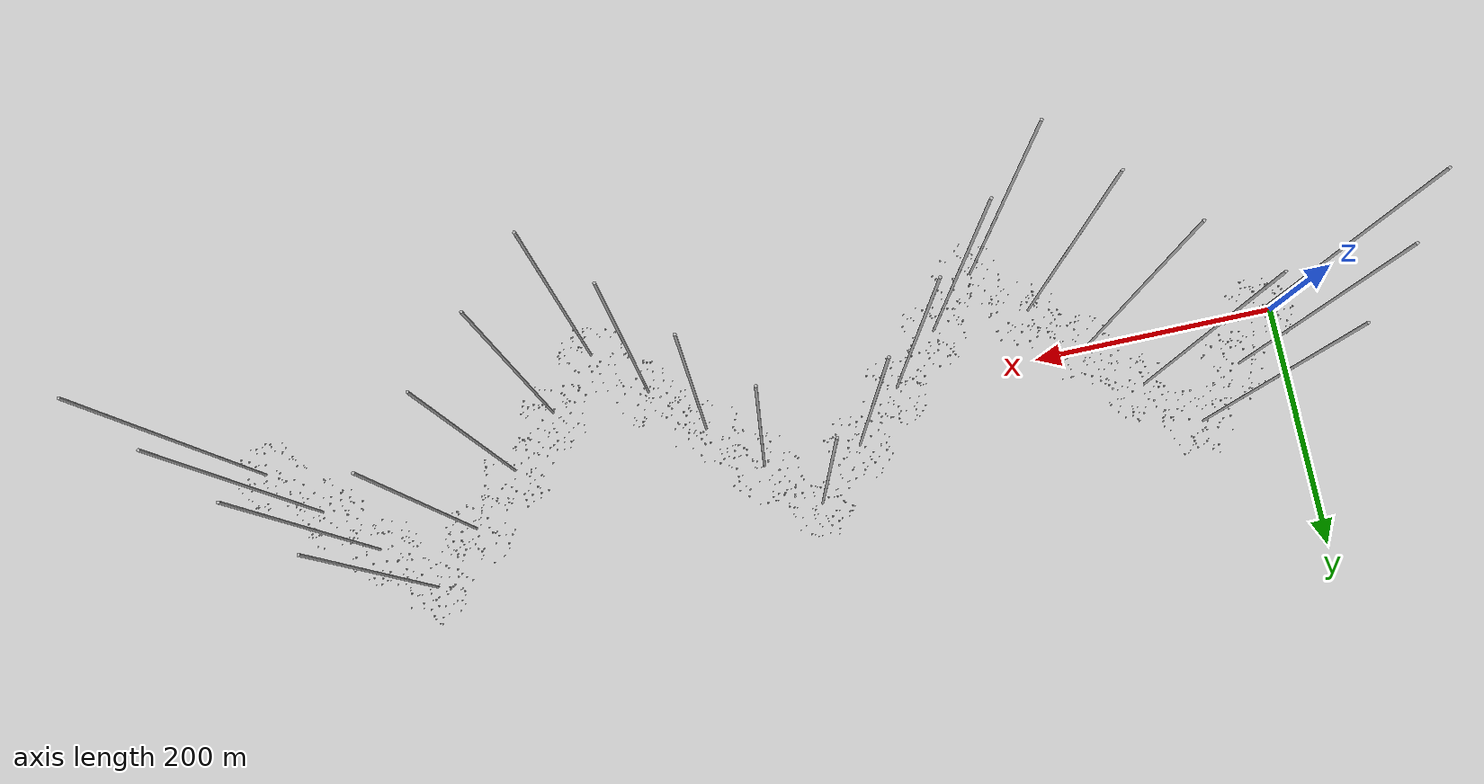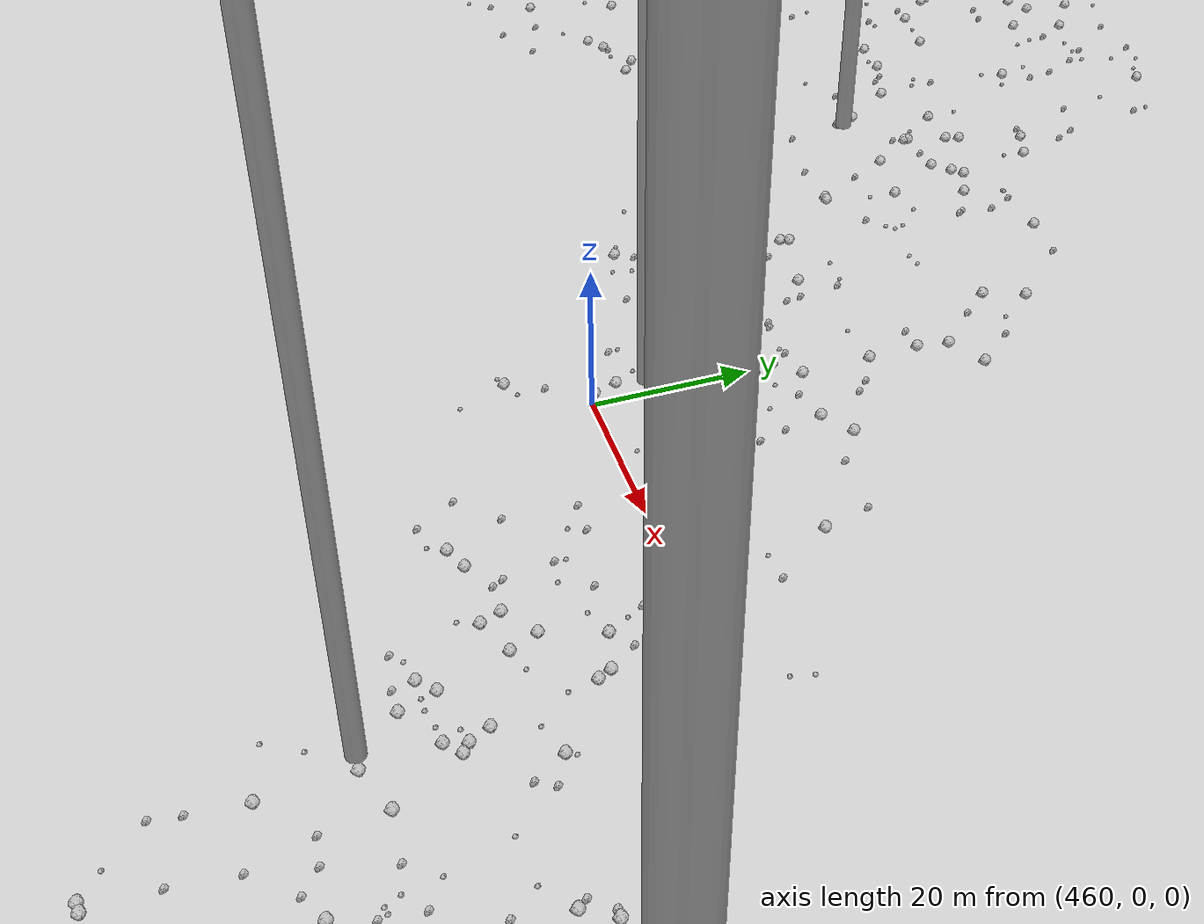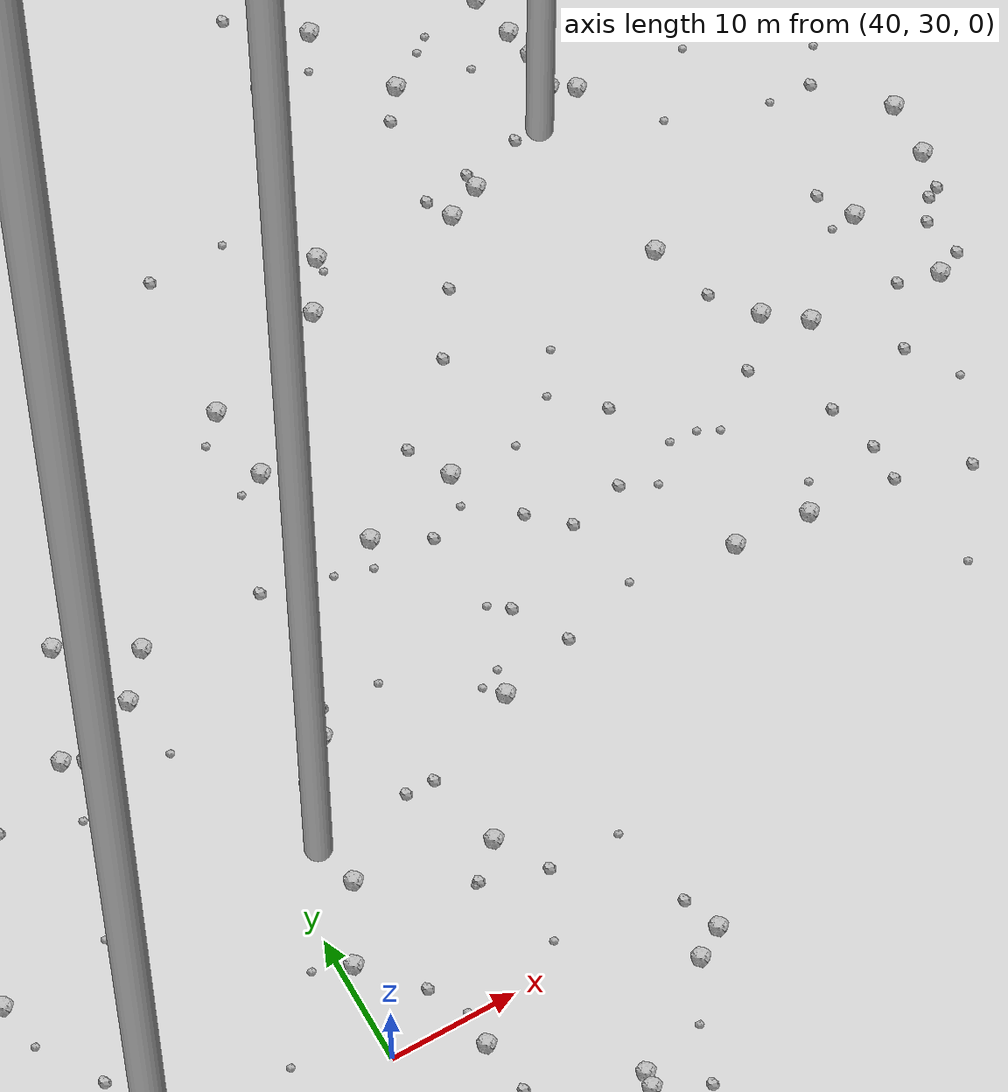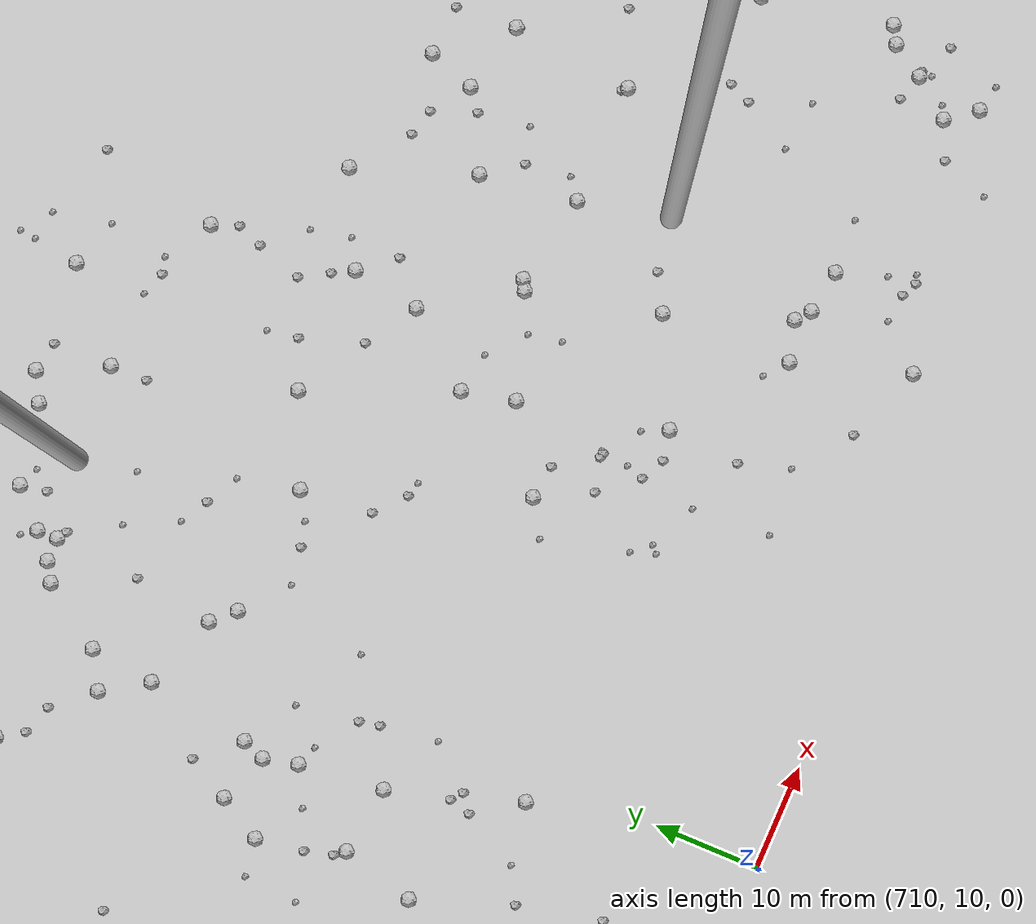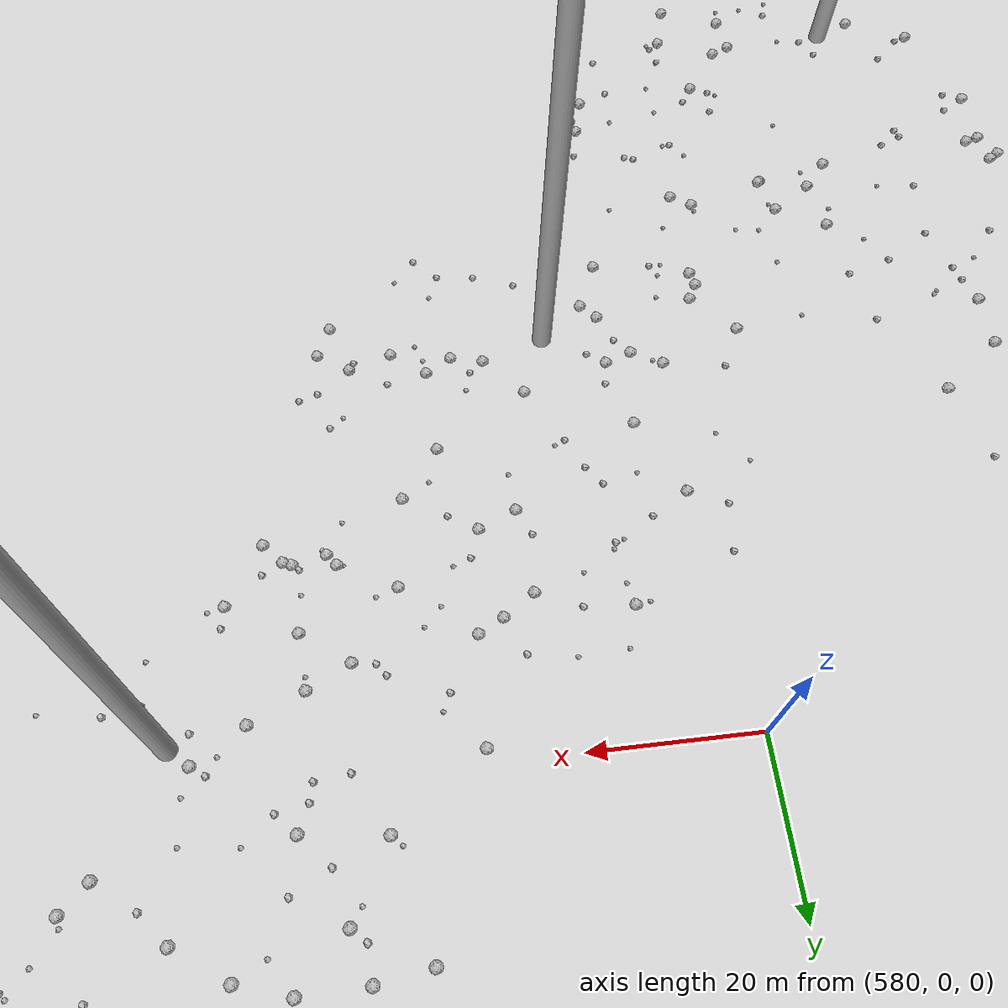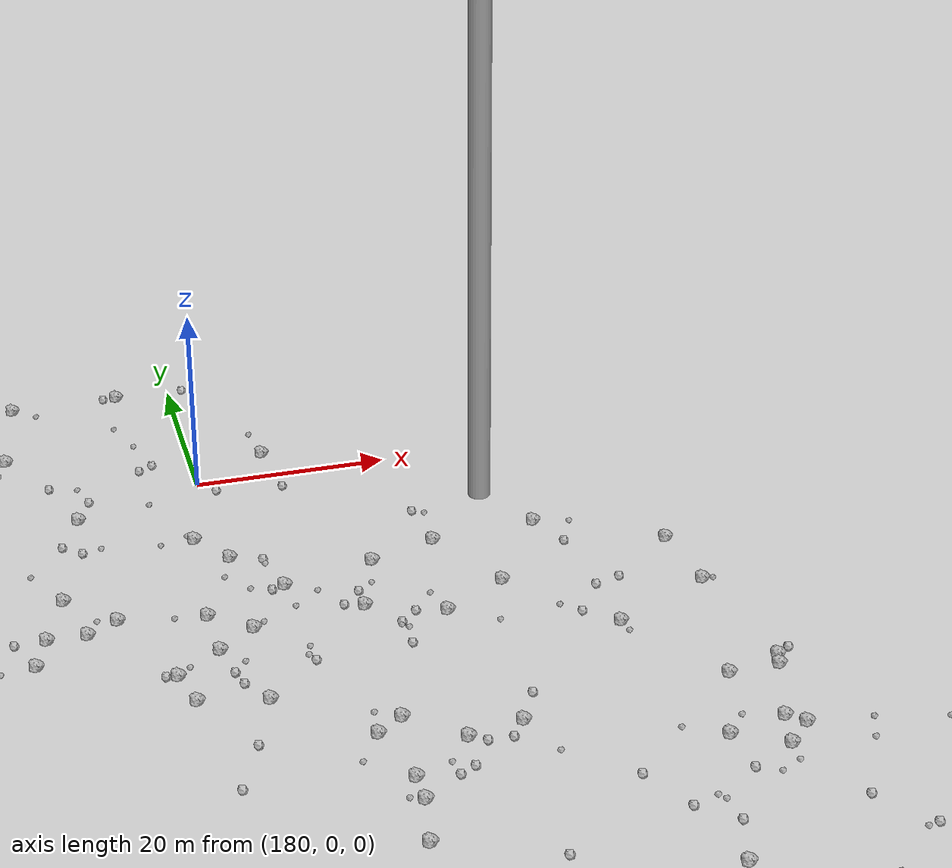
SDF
<sdf version="1.6">
 <world name="default">
  <include><uri>model://custom_ground</uri></include>
  <include><uri>model://sun</uri></include>
  <spherical_coordinates>
   <surface_model>EARTH_WGS84</surface_model>
   <latitude_deg>38.161479</latitude_deg>
   <longitude_deg>-122.454630</longitude_deg>
   <elevation>488.0</elevation>
   <heading_deg>90</heading_deg>
  </spherical_coordinates>
  <model name="rock1_0_0">
   <include><uri>model://rock1</uri><pose>-9.77276181470488 21.8099734527842 0.5 0 0 0</pose></include>
  </model>
  <model name="rock1_0_1">
   <include><uri>model://rock1</uri><pose>15.529140210550814 -22.66288977719951 0.5 0 0 0</pose></include>
  </model>
  <model name="rock1_0_2">
   <include><uri>model://rock1</uri><pose>10.802766246970773 -18.14908372542623 0.5 0 0 0</pose></include>
  </model>
  <model name="rock1_0_3">
   <include><uri>model://rock1</uri><pose>7.1267367151764205 -4.317388145157924 0.5 0 0 0</pose></include>
  </model>
  <model name="rock1_0_4">
   <include><uri>model://rock1</uri><pose>4.335377980278594 -5.060748344593421 0.5 0 0 0</pose></include>
  </model>
  <model name="rock1_0_5">
   <include><uri>model://rock1</uri><pose>-5.740439910997395 5.9691690261330805 0.5 0 0 0</pose></include>
  </model>
  <model name="rock1_0_6">
   <include><uri>model://rock1</uri><pose>-9.71702643830284 -2.5857592259953606 0.5 0 0 0</pose></include>
  </model>
  <model name="rock1_0_7">
   <include><uri>model://rock1</uri><pose>-12.819439266588102 18.29644983982496 0.5 0 0 0</pose></include>
  </model>
  <model name="rock1_0_8">
   <include><uri>model://rock1</uri><pose>28.656645429457157 -2.376011091754407 0.5 0 0 0</pose></include>
  </model>
  <model name="rock1_0_9">
   <include><uri>model://rock1</uri><pose>9.820375933043767 -18.11331956434958 0.5 0 0 0</pose></include>
  </model>
  <model name="rock1_0_10">
   <include><uri>model://rock1</uri><pose>-19.570708304993765 0.8835321520810169 0.5 0 0 0</pose></include>
  </model>
  <model name="rock1_0_11">
   <include><uri>model://rock1</uri><pose>11.542015412736642 -22.64654892862683 0.5 0 0 0</pose></include>
  </model>
  <model name="rock1_0_12">
   <include><uri>model://rock1</uri><pose>-12.072474149136594 -18.024422969135216 0.5 0 0 0</pose></include>
  </model>
  <model name="rock1_0_13">
   <include><uri>model://rock1</uri><pose>20.2976462596757 27.61976532385612 0.5 0 0 0</pose></include>
  </model>
  <model name="rock1_0_14">
   <include><uri>model://rock1</uri><pose>-7.263154652959729 -12.584405245134082 0.5 0 0 0</pose></include>
  </model>
  <model name="rock1_0_15">
   <include><uri>model://rock1</uri><pose>-13.83027314720993 -15.04061631097918 0.5 0 0 0</pose></include>
  </model>
  <model name="rock1_0_16">
   <include><uri>model://rock1</uri><pose>-12.140821696426434 11.611560955578511 0.5 0 0 0</pose></include>
  </model>
  <model name="rock1_0_17">
   <include><uri>model://rock1</uri><pose>27.984937752587918 2.8802691164289342 0.5 0 0 0</pose></include>
  </model>
  <model name="rock1_0_18">
   <include><uri>model://rock1</uri><pose>9.715163474016368 -17.979564762945287 0.5 0 0 0</pose></include>
  </model>
  <model name="rock1_0_19">
   <include><uri>model://rock1</uri><pose>18.785384007735715 -27.877572683564146 0.5 0 0 0</pose></include>
  </model>
  <model name="rock1_0_20">
   <include><uri>model://rock1</uri><pose>-17.807545940576453 1.875232186931754 0.5 0 0 0</pose></include>
  </model>
  <model name="rock1_0_21">
   <include><uri>model://rock1</uri><pose>1.8942526935705146 4.3882175304499285 0.5 0 0 0</pose></include>
  </model>
  <model name="rock1_0_22">
   <include><uri>model://rock1</uri><pose>-1.488478801488565 -21.98220548981073 0.5 0 0 0</pose></include>
  </model>
  <model name="rock1_0_23">
   <include><uri>model://rock1</uri><pose>-12.431893261029971 19.56632043564703 0.5 0 0 0</pose></include>
  </model>
  <model name="rock1_0_24">
   <include><uri>model://rock1</uri><pose>29.865523169611052 21.397833099032916 0.5 0 0 0</pose></include>
  </model>
  <model name="rock1_0_25">
   <include><uri>model://rock1</uri><pose>19.197967476564564 -22.746143736703253 0.5 0 0 0</pose></include>
  </model>
  <model name="rock1_0_26">
   <include><uri>model://rock1</uri><pose>33.112570294840296 -19.02785296915463 0.5 0 0 0</pose></include>
  </model>
  <model name="rock2_0_0">
   <include><uri>model://rock2</uri><pose>24.672884386237477 1.7697222131145125 0.3 0 0 0</pose></include>
  </model>
  <model name="rock2_0_1">
   <include><uri>model://rock2</uri><pose>9.0921642755625 -21.76567222523215 0.3 0 0 0</pose></include>
  </model>
  <model name="rock2_0_2">
   <include><uri>model://rock2</uri><pose>7.282691312202164 17.126446933850303 0.3 0 0 0</pose></include>
  </model>
  <model name="rock2_0_3">
   <include><uri>model://rock2</uri><pose>-3.8049064353835576 -22.39104044151418 0.3 0 0 0</pose></include>
  </model>
  <model name="rock2_0_4">
   <include><uri>model://rock2</uri><pose>-12.886581596115665 12.356115863473576 0.3 0 0 0</pose></include>
  </model>
  <model name="rock2_0_5">
   <include><uri>model://rock2</uri><pose>37.303327007445 -3.4718597730901273 0.3 0 0 0</pose></include>
  </model>
  <model name="rock2_0_6">
   <include><uri>model://rock2</uri><pose>-10.546117190324754 16.66951056696442 0.3 0 0 0</pose></include>
  </model>
  <model name="rock2_0_7">
   <include><uri>model://rock2</uri><pose>17.800150782080387 18.22044048188374 0.3 0 0 0</pose></include>
  </model>
  <model name="rock2_0_8">
   <include><uri>model://rock2</uri><pose>-5.814131007291007 3.1368022297072073 0.3 0 0 0</pose></include>
  </model>
  <model name="rock2_0_9">
   <include><uri>model://rock2</uri><pose>30.704000315494632 -15.94908447157485 0.3 0 0 0</pose></include>
  </model>
  <model name="rock2_0_10">
   <include><uri>model://rock2</uri><pose>32.309816442646465 19.582897744444473 0.3 0 0 0</pose></include>
  </model>
  <model name="rock2_0_11">
   <include><uri>model://rock2</uri><pose>21.679872227992156 -18.224990331723646 0.3 0 0 0</pose></include>
  </model>
  <model name="rock2_0_12">
   <include><uri>model://rock2</uri><pose>-1.6767650726348933 11.37654166789465 0.3 0 0 0</pose></include>
  </model>
  <model name="rock2_0_13">
   <include><uri>model://rock2</uri><pose>17.071826191386606 7.012280428114302 0.3 0 0 0</pose></include>
  </model>
  <model name="rock2_0_14">
   <include><uri>model://rock2</uri><pose>25.184267354318152 -13.19233265089305 0.3 0 0 0</pose></include>
  </model>
  <model name="rock2_0_15">
   <include><uri>model://rock2</uri><pose>11.214550142372538 -8.896025732288791 0.3 0 0 0</pose></include>
  </model>
  <model name="rock2_0_16">
   <include><uri>model://rock2</uri><pose>-0.2020065628778447 -27.329453953755227 0.3 0 0 0</pose></include>
  </model>
  <model name="rock2_0_17">
   <include><uri>model://rock2</uri><pose>26.672328599496552 -5.038553967550495 0.3 0 0 0</pose></include>
  </model>
  <model name="rock2_0_18">
   <include><uri>model://rock2</uri><pose>15.133319890241985 -29.0064009081244 0.3 0 0 0</pose></include>
  </model>
  <model name="rock2_0_19">
   <include><uri>model://rock2</uri><pose>-3.4223382068984485 -6.755226548412445 0.3 0 0 0</pose></include>
  </model>
  <model name="rock2_0_20">
   <include><uri>model://rock2</uri><pose>27.895585488205512 -17.361032139091293 0.3 0 0 0</pose></include>
  </model>
  <model name="rock2_0_21">
   <include><uri>model://rock2</uri><pose>4.733450016711842 5.034475750067692 0.3 0 0 0</pose></include>
  </model>
  <model name="rock2_0_22">
   <include><uri>model://rock2</uri><pose>2.745883581066767 -22.538649638405964 0.3 0 0 0</pose></include>
  </model>
  <model name="rock2_0_23">
   <include><uri>model://rock2</uri><pose>12.055524504233738 -2.2964629682996716 0.3 0 0 0</pose></include>
  </model>
  <model name="rock2_0_24">
   <include><uri>model://rock2</uri><pose>-6.309073234697582 -15.76173935061103 0.3 0 0 0</pose></include>
  </model>
  <model name="rock2_0_25">
   <include><uri>model://rock2</uri><pose>-10.909597122056063 -5.443741095262997 0.3 0 0 0</pose></include>
  </model>
  <model name="rock2_0_26">
   <include><uri>model://rock2</uri><pose>21.398545739676315 -2.586239220714205 0.3 0 0 0</pose></include>
  </model>
  <model name="rock3_0_0">
   <include><uri>model://rock3</uri><pose>6.70923281369755 12.793565016293115 0.2 0 0 0</pose></include>
  </model>
  <model name="rock3_0_1">
   <include><uri>model://rock3</uri><pose>11.809368077345475 -4.670966708352587 0.2 0 0 0</pose></include>
  </model>
  <model name="rock3_0_2">
   <include><uri>model://rock3</uri><pose>-18.404632246733396 2.797411758416807 0.2 0 0 0</pose></include>
  </model>
  <model name="rock3_0_3">
   <include><uri>model://rock3</uri><pose>15.359044884560461 25.82914263770887 0.2 0 0 0</pose></include>
  </model>
  <model name="rock3_0_4">
   <include><uri>model://rock3</uri><pose>26.176618996268964 -3.5359635993462177 0.2 0 0 0</pose></include>
  </model>
  <model name="rock3_0_5">
   <include><uri>model://rock3</uri><pose>11.899140303874063 -20.493666975257852 0.2 0 0 0</pose></include>
  </model>
  <model name="rock3_0_6">
   <include><uri>model://rock3</uri><pose>28.499080414997145 -9.813492434353233 0.2 0 0 0</pose></include>
  </model>
  <model name="rock3_0_7">
   <include><uri>model://rock3</uri><pose>-7.497578106265962 9.2885482675823 0.2 0 0 0</pose></include>
  </model>
  <model name="rock3_0_8">
   <include><uri>model://rock3</uri><pose>14.200542419742185 4.128393674195415 0.2 0 0 0</pose></include>
  </model>
  <model name="rock3_0_9">
   <include><uri>model://rock3</uri><pose>24.117507120994773 17.913348843743883 0.2 0 0 0</pose></include>
  </model>
  <model name="rock3_0_10">
   <include><uri>model://rock3</uri><pose>19.7718291208647 -28.318921247102843 0.2 0 0 0</pose></include>
  </model>
  <model name="rock3_0_11">
   <include><uri>model://rock3</uri><pose>-14.233135272043702 15.336271680708983 0.2 0 0 0</pose></include>
  </model>
  <model name="rock3_0_12">
   <include><uri>model://rock3</uri><pose>-9.361158330032444 -21.44505910740297 0.2 0 0 0</pose></include>
  </model>
  <model name="rock3_0_13">
   <include><uri>model://rock3</uri><pose>-5.6815284531574655 18.035111940688132 0.2 0 0 0</pose></include>
  </model>
  <model name="rock3_0_14">
   <include><uri>model://rock3</uri><pose>-12.304593055046926 1.8864110618863563 0.2 0 0 0</pose></include>
  </model>
  <model name="rock3_0_15">
   <include><uri>model://rock3</uri><pose>-6.037179688339693 -13.184482897232982 0.2 0 0 0</pose></include>
  </model>
  <model name="rock3_0_16">
   <include><uri>model://rock3</uri><pose>-15.797627513155227 8.224540038531941 0.2 0 0 0</pose></include>
  </model>
  <model name="rock3_0_17">
   <include><uri>model://rock3</uri><pose>1.1790453048647116 21.23491389383181 0.2 0 0 0</pose></include>
  </model>
  <model name="rock3_0_18">
   <include><uri>model://rock3</uri><pose>33.94445328328892 -6.33963401643053 0.2 0 0 0</pose></include>
  </model>
  <model name="rock3_0_19">
   <include><uri>model://rock3</uri><pose>-17.1701521160665 7.652428295204771 0.2 0 0 0</pose></include>
  </model>
  <model name="rock3_0_20">
   <include><uri>model://rock3</uri><pose>11.291785192977088 27.632537839103875 0.2 0 0 0</pose></include>
  </model>
  <model name="rock3_0_21">
   <include><uri>model://rock3</uri><pose>17.07144890196981 14.838239595058027 0.2 0 0 0</pose></include>
  </model>
  <model name="rock3_0_22">
   <include><uri>model://rock3</uri><pose>21.071745869870412 -16.598942131105353 0.2 0 0 0</pose></include>
  </model>
  <model name="rock3_0_23">
   <include><uri>model://rock3</uri><pose>-11.940070830262929 5.461165025715616 0.2 0 0 0</pose></include>
  </model>
  <model name="rock3_0_24">
   <include><uri>model://rock3</uri><pose>39.19466173958772 3.6102048181277624 0.2 0 0 0</pose></include>
  </model>
  <model name="rock3_0_25">
   <include><uri>model://rock3</uri><pose>-6.177379488890448 -20.040881051240063 0.2 0 0 0</pose></include>
  </model>
  <model name="rock3_0_26">
   <include><uri>model://rock3</uri><pose>21.108901637839267 14.4908311359223 0.2 0 0 0</pose></include>
  </model>
  <model name="rock1_1_0">
   <include><uri>model://rock1</uri><pose>47.358492466506156 53.57605874247158 0.5 0 0 0</pose></include>
  </model>
  <model name="rock1_1_1">
   <include><uri>model://rock1</uri><pose>46.481229987996194 11.35757771535272 0.5 0 0 0</pose></include>
  </model>
  <model name="rock1_1_2">
   <include><uri>model://rock1</uri><pose>65.00866893219741 27.14167839056004 0.5 0 0 0</pose></include>
  </model>
  <model name="rock1_1_3">
   <include><uri>model://rock1</uri><pose>29.454065732067583 27.414508570174913 0.5 0 0 0</pose></include>
  </model>
  <model name="rock1_1_4">
   <include><uri>model://rock1</uri><pose>46.379075751788875 16.129686452924194 0.5 0 0 0</pose></include>
  </model>
  <model name="rock1_1_5">
   <include><uri>model://rock1</uri><pose>35.276441795367234 11.393771315891676 0.5 0 0 0</pose></include>
  </model>
  <model name="rock1_1_6">
   <include><uri>model://rock1</uri><pose>62.767845638668504 25.765898120931546 0.5 0 0 0</pose></include>
  </model>
  <model name="rock1_1_7">
   <include><uri>model://rock1</uri><pose>33.579100418457585 69.08517697428522 0.5 0 0 0</pose></include>
  </model>
  <model name="rock1_1_8">
   <include><uri>model://rock1</uri><pose>39.28860846455176 23.814886015410124 0.5 0 0 0</pose></include>
  </model>
  <model name="rock1_1_9">
   <include><uri>model://rock1</uri><pose>55.13397303310606 20.25041240162919 0.5 0 0 0</pose></include>
  </model>
  <model name="rock1_1_10">
   <include><uri>model://rock1</uri><pose>40.97177926827366 37.3062082135952 0.5 0 0 0</pose></include>
  </model>
  <model name="rock1_1_11">
   <include><uri>model://rock1</uri><pose>12.373204693940929 28.340388456052303 0.5 0 0 0</pose></include>
  </model>
  <model name="rock1_1_12">
   <include><uri>model://rock1</uri><pose>17.75949954125859 46.73195795374948 0.5 0 0 0</pose></include>
  </model>
  <model name="rock1_1_13">
   <include><uri>model://rock1</uri><pose>31.709604070569306 60.22643744922448 0.5 0 0 0</pose></include>
  </model>
  <model name="rock1_1_14">
   <include><uri>model://rock1</uri><pose>24.080621355023503 37.62648593958249 0.5 0 0 0</pose></include>
  </model>
  <model name="rock1_1_15">
   <include><uri>model://rock1</uri><pose>36.45740775658842 62.775600947537185 0.5 0 0 0</pose></include>
  </model>
  <model name="rock1_1_16">
   <include><uri>model://rock1</uri><pose>46.33023377943392 27.569849630015334 0.5 0 0 0</pose></include>
  </model>
  <model name="rock1_1_17">
   <include><uri>model://rock1</uri><pose>24.32641335587417 61.97473230909098 0.5 0 0 0</pose></include>
  </model>
  <model name="rock1_1_18">
   <include><uri>model://rock1</uri><pose>43.98982279050567 42.855813838502904 0.5 0 0 0</pose></include>
  </model>
  <model name="rock1_1_19">
   <include><uri>model://rock1</uri><pose>24.70966785015862 34.154119268439416 0.5 0 0 0</pose></include>
  </model>
  <model name="rock1_1_20">
   <include><uri>model://rock1</uri><pose>60.478571462903396 49.981791494876646 0.5 0 0 0</pose></include>
  </model>
  <model name="rock1_1_21">
   <include><uri>model://rock1</uri><pose>40.33236959768985 18.755579860697225 0.5 0 0 0</pose></include>
  </model>
  <model name="rock1_1_22">
   <include><uri>model://rock1</uri><pose>30.041524914570022 61.0456510102938 0.5 0 0 0</pose></include>
  </model>
  <model name="rock1_1_23">
   <include><uri>model://rock1</uri><pose>39.23557722557911 65.87029670908882 0.5 0 0 0</pose></include>
  </model>
  <model name="rock1_1_24">
   <include><uri>model://rock1</uri><pose>54.28494422227642 40.71582676070288 0.5 0 0 0</pose></include>
  </model>
  <model name="rock1_1_25">
   <include><uri>model://rock1</uri><pose>12.877848048691886 33.90348055956734 0.5 0 0 0</pose></include>
  </model>
  <model name="rock1_1_26">
   <include><uri>model://rock1</uri><pose>54.969064864304215 19.08648112309383 0.5 0 0 0</pose></include>
  </model>
  <model name="rock2_1_0">
   <include><uri>model://rock2</uri><pose>44.66746524179217 33.228544824351665 0.3 0 0 0</pose></include>
  </model>
  <model name="rock2_1_1">
   <include><uri>model://rock2</uri><pose>46.93734825552984 23.384585557539147 0.3 0 0 0</pose></include>
  </model>
  <model name="rock2_1_2">
   <include><uri>model://rock2</uri><pose>51.778685547605306 38.49705284641408 0.3 0 0 0</pose></include>
  </model>
  <model name="rock2_1_3">
   <include><uri>model://rock2</uri><pose>17.48260194089005 57.93992522870157 0.3 0 0 0</pose></include>
  </model>
  <model name="rock2_1_4">
   <include><uri>model://rock2</uri><pose>34.59286942788043 24.00793624057988 0.3 0 0 0</pose></include>
  </model>
  <model name="rock2_1_5">
   <include><uri>model://rock2</uri><pose>38.00065394093113 16.440001326253423 0.3 0 0 0</pose></include>
  </model>
  <model name="rock2_1_6">
   <include><uri>model://rock2</uri><pose>12.131689509835146 29.556818295786822 0.3 0 0 0</pose></include>
  </model>
  <model name="rock2_1_7">
   <include><uri>model://rock2</uri><pose>58.793057663020605 17.215493680316765 0.3 0 0 0</pose></include>
  </model>
  <model name="rock2_1_8">
   <include><uri>model://rock2</uri><pose>29.368827052199876 12.10575847210248 0.3 0 0 0</pose></include>
  </model>
  <model name="rock2_1_9">
   <include><uri>model://rock2</uri><pose>63.87690238781511 30.088187360285545 0.3 0 0 0</pose></include>
  </model>
  <model name="rock2_1_10">
   <include><uri>model://rock2</uri><pose>30.327463649281732 52.743136372436055 0.3 0 0 0</pose></include>
  </model>
  <model name="rock2_1_11">
   <include><uri>model://rock2</uri><pose>21.37043266864288 38.32755448617158 0.3 0 0 0</pose></include>
  </model>
  <model name="rock2_1_12">
   <include><uri>model://rock2</uri><pose>56.670342049263546 36.8945097140592 0.3 0 0 0</pose></include>
  </model>
  <model name="rock2_1_13">
   <include><uri>model://rock2</uri><pose>21.14854584781888 34.564751087681046 0.3 0 0 0</pose></include>
  </model>
  <model name="rock2_1_14">
   <include><uri>model://rock2</uri><pose>20.61281562876276 25.99260576910044 0.3 0 0 0</pose></include>
  </model>
  <model name="rock2_1_15">
   <include><uri>model://rock2</uri><pose>48.33313624171437 55.55597884096619 0.3 0 0 0</pose></include>
  </model>
  <model name="rock2_1_16">
   <include><uri>model://rock2</uri><pose>23.553494548676944 58.47386863914265 0.3 0 0 0</pose></include>
  </model>
  <model name="rock2_1_17">
   <include><uri>model://rock2</uri><pose>50.46901629905009 46.82890652708455 0.3 0 0 0</pose></include>
  </model>
  <model name="rock2_1_18">
   <include><uri>model://rock2</uri><pose>35.15296604348876 66.25549085684568 0.3 0 0 0</pose></include>
  </model>
  <model name="rock2_1_19">
   <include><uri>model://rock2</uri><pose>66.50032011749923 51.52450169093256 0.3 0 0 0</pose></include>
  </model>
  <model name="rock2_1_20">
   <include><uri>model://rock2</uri><pose>31.544907471414838 19.623029130096587 0.3 0 0 0</pose></include>
  </model>
  <model name="rock2_1_21">
   <include><uri>model://rock2</uri><pose>44.52744251370853 51.09281751212122 0.3 0 0 0</pose></include>
  </model>
  <model name="rock2_1_22">
   <include><uri>model://rock2</uri><pose>43.94961722991214 17.525800204914994 0.3 0 0 0</pose></include>
  </model>
  <model name="rock2_1_23">
   <include><uri>model://rock2</uri><pose>52.716671733595945 46.767143763640426 0.3 0 0 0</pose></include>
  </model>
  <model name="rock2_1_24">
   <include><uri>model://rock2</uri><pose>48.71241437384441 65.5445438986071 0.3 0 0 0</pose></include>
  </model>
  <model name="rock2_1_25">
   <include><uri>model://rock2</uri><pose>37.11449802071874 18.491342573574332 0.3 0 0 0</pose></include>
  </model>
  <model name="rock2_1_26">
   <include><uri>model://rock2</uri><pose>27.869086196236545 47.859572832709965 0.3 0 0 0</pose></include>
  </model>
  <model name="rock3_1_0">
   <include><uri>model://rock3</uri><pose>38.0719158662871 38.378322204604984 0.2 0 0 0</pose></include>
  </model>
  <model name="rock3_1_1">
   <include><uri>model://rock3</uri><pose>46.276278484108666 30.312674437243153 0.2 0 0 0</pose></include>
  </model>
  <model name="rock3_1_2">
   <include><uri>model://rock3</uri><pose>42.44188618160175 20.343749955657668 0.2 0 0 0</pose></include>
  </model>
  <model name="rock3_1_3">
   <include><uri>model://rock3</uri><pose>44.93050953150357 18.882932745220486 0.2 0 0 0</pose></include>
  </model>
  <model name="rock3_1_4">
   <include><uri>model://rock3</uri><pose>56.87309014974473 63.19981532877329 0.2 0 0 0</pose></include>
  </model>
  <model name="rock3_1_5">
   <include><uri>model://rock3</uri><pose>59.21617756919251 51.24666031676362 0.2 0 0 0</pose></include>
  </model>
  <model name="rock3_1_6">
   <include><uri>model://rock3</uri><pose>26.421815086888667 47.66413188363315 0.2 0 0 0</pose></include>
  </model>
  <model name="rock3_1_7">
   <include><uri>model://rock3</uri><pose>52.373792001225816 64.64108262217131 0.2 0 0 0</pose></include>
  </model>
  <model name="rock3_1_8">
   <include><uri>model://rock3</uri><pose>54.04250091552496 64.07647687178589 0.2 0 0 0</pose></include>
  </model>
  <model name="rock3_1_9">
   <include><uri>model://rock3</uri><pose>62.248962242944856 36.746210393489136 0.2 0 0 0</pose></include>
  </model>
  <model name="rock3_1_10">
   <include><uri>model://rock3</uri><pose>37.16609301446665 57.822868388057515 0.2 0 0 0</pose></include>
  </model>
  <model name="rock3_1_11">
   <include><uri>model://rock3</uri><pose>51.447839281788895 38.35949818578572 0.2 0 0 0</pose></include>
  </model>
  <model name="rock3_1_12">
   <include><uri>model://rock3</uri><pose>29.271608747403647 56.34832602003442 0.2 0 0 0</pose></include>
  </model>
  <model name="rock3_1_13">
   <include><uri>model://rock3</uri><pose>36.34904622132245 19.510713951003403 0.2 0 0 0</pose></include>
  </model>
  <model name="rock3_1_14">
   <include><uri>model://rock3</uri><pose>33.343443703007466 32.82642906970545 0.2 0 0 0</pose></include>
  </model>
  <model name="rock3_1_15">
   <include><uri>model://rock3</uri><pose>52.9623851941358 65.59986934310021 0.2 0 0 0</pose></include>
  </model>
  <model name="rock3_1_16">
   <include><uri>model://rock3</uri><pose>15.21814959815121 52.16615928336622 0.2 0 0 0</pose></include>
  </model>
  <model name="rock3_1_17">
   <include><uri>model://rock3</uri><pose>40.47977740275181 19.540311564162742 0.2 0 0 0</pose></include>
  </model>
  <model name="rock3_1_18">
   <include><uri>model://rock3</uri><pose>60.836684598146356 51.957740828775165 0.2 0 0 0</pose></include>
  </model>
  <model name="rock3_1_19">
   <include><uri>model://rock3</uri><pose>27.185924684004465 16.615482402135342 0.2 0 0 0</pose></include>
  </model>
  <model name="rock3_1_20">
   <include><uri>model://rock3</uri><pose>25.048413465930203 40.904193115993706 0.2 0 0 0</pose></include>
  </model>
  <model name="rock3_1_21">
   <include><uri>model://rock3</uri><pose>54.25006590029528 31.983932420326255 0.2 0 0 0</pose></include>
  </model>
  <model name="rock3_1_22">
   <include><uri>model://rock3</uri><pose>16.582761331432625 34.925705263557745 0.2 0 0 0</pose></include>
  </model>
  <model name="rock3_1_23">
   <include><uri>model://rock3</uri><pose>60.19601151524049 21.481945245837917 0.2 0 0 0</pose></include>
  </model>
  <model name="rock3_1_24">
   <include><uri>model://rock3</uri><pose>18.309913580674554 43.02951697642547 0.2 0 0 0</pose></include>
  </model>
  <model name="rock3_1_25">
   <include><uri>model://rock3</uri><pose>52.8319796958323 55.233953178732435 0.2 0 0 0</pose></include>
  </model>
  <model name="rock3_1_26">
   <include><uri>model://rock3</uri><pose>62.5766713453302 56.63541581639507 0.2 0 0 0</pose></include>
  </model>
  <model name="rock1_2_0">
   <include><uri>model://rock1</uri><pose>52.78243155701042 79.53331819552805 0.5 0 0 0</pose></include>
  </model>
  <model name="rock1_2_1">
   <include><uri>model://rock1</uri><pose>88.6970512852989 89.43952162879106 0.5 0 0 0</pose></include>
  </model>
  <model name="rock1_2_2">
   <include><uri>model://rock1</uri><pose>108.47699344716213 72.2764745271763 0.5 0 0 0</pose></include>
  </model>
  <model name="rock1_2_3">
   <include><uri>model://rock1</uri><pose>62.77353413324488 83.0456455581044 0.5 0 0 0</pose></include>
  </model>
  <model name="rock1_2_4">
   <include><uri>model://rock1</uri><pose>108.5725876647193 76.61665613557999 0.5 0 0 0</pose></include>
  </model>
  <model name="rock1_2_5">
   <include><uri>model://rock1</uri><pose>85.69371150360968 99.47466617319404 0.5 0 0 0</pose></include>
  </model>
  <model name="rock1_2_6">
   <include><uri>model://rock1</uri><pose>91.47217653138935 66.86870169318226 0.5 0 0 0</pose></include>
  </model>
  <model name="rock1_2_7">
   <include><uri>model://rock1</uri><pose>80.7173698531018 51.927661108750826 0.5 0 0 0</pose></include>
  </model>
  <model name="rock1_2_8">
   <include><uri>model://rock1</uri><pose>68.05299396979765 100.80194677434828 0.5 0 0 0</pose></include>
  </model>
  <model name="rock1_2_9">
   <include><uri>model://rock1</uri><pose>104.67474077475734 63.257062728943644 0.5 0 0 0</pose></include>
  </model>
  <model name="rock1_2_10">
   <include><uri>model://rock1</uri><pose>57.75506111603196 65.26194795506714 0.5 0 0 0</pose></include>
  </model>
  <model name="rock1_2_11">
   <include><uri>model://rock1</uri><pose>78.17747895862456 86.03873779980857 0.5 0 0 0</pose></include>
  </model>
  <model name="rock1_2_12">
   <include><uri>model://rock1</uri><pose>86.49114355157595 95.91227267684958 0.5 0 0 0</pose></include>
  </model>
  <model name="rock1_2_13">
   <include><uri>model://rock1</uri><pose>97.39835886146057 102.64447214517823 0.5 0 0 0</pose></include>
  </model>
  <model name="rock1_2_14">
   <include><uri>model://rock1</uri><pose>87.01183342498766 93.53332689161235 0.5 0 0 0</pose></include>
  </model>
  <model name="rock1_2_15">
   <include><uri>model://rock1</uri><pose>76.97605024075742 96.07353769879424 0.5 0 0 0</pose></include>
  </model>
  <model name="rock1_2_16">
   <include><uri>model://rock1</uri><pose>86.9249791781888 90.48666360380587 0.5 0 0 0</pose></include>
  </model>
  <model name="rock1_2_17">
   <include><uri>model://rock1</uri><pose>73.50225655613039 103.15882400701173 0.5 0 0 0</pose></include>
  </model>
  <model name="rock1_2_18">
   <include><uri>model://rock1</uri><pose>101.50106749045241 70.37600268824926 0.5 0 0 0</pose></include>
  </model>
  <model name="rock1_2_19">
   <include><uri>model://rock1</uri><pose>94.43925469783993 64.62980705026791 0.5 0 0 0</pose></include>
  </model>
  <model name="rock1_2_20">
   <include><uri>model://rock1</uri><pose>53.28903243898986 73.66794723614836 0.5 0 0 0</pose></include>
  </model>
  <model name="rock1_2_21">
   <include><uri>model://rock1</uri><pose>65.10719911111981 86.74768604995946 0.5 0 0 0</pose></include>
  </model>
  <model name="rock1_2_22">
   <include><uri>model://rock1</uri><pose>87.21325879698817 75.07383989892702 0.5 0 0 0</pose></include>
  </model>
  <model name="rock1_2_23">
   <include><uri>model://rock1</uri><pose>86.65683643235869 51.471666175126316 0.5 0 0 0</pose></include>
  </model>
  <model name="rock1_2_24">
   <include><uri>model://rock1</uri><pose>75.4919788263856 84.85607496637124 0.5 0 0 0</pose></include>
  </model>
  <model name="rock1_2_25">
   <include><uri>model://rock1</uri><pose>59.19501206439168 80.2510051834609 0.5 0 0 0</pose></include>
  </model>
  <model name="rock1_2_26">
   <include><uri>model://rock1</uri><pose>65.3497899104205 66.8592166858235 0.5 0 0 0</pose></include>
  </model>
  <model name="rock2_2_0">
   <include><uri>model://rock2</uri><pose>53.41313391542112 91.08251468909708 0.3 0 0 0</pose></include>
  </model>
  <model name="rock2_2_1">
   <include><uri>model://rock2</uri><pose>88.91219613121251 96.53196391926866 0.3 0 0 0</pose></include>
  </model>
  <model name="rock2_2_2">
   <include><uri>model://rock2</uri><pose>101.47331041927215 64.13361727319324 0.3 0 0 0</pose></include>
  </model>
  <model name="rock2_2_3">
   <include><uri>model://rock2</uri><pose>71.18993039164395 59.11832813984954 0.3 0 0 0</pose></include>
  </model>
  <model name="rock2_2_4">
   <include><uri>model://rock2</uri><pose>107.93010217443961 69.40262208902217 0.3 0 0 0</pose></include>
  </model>
  <model name="rock2_2_5">
   <include><uri>model://rock2</uri><pose>107.02760581409922 69.00022584160756 0.3 0 0 0</pose></include>
  </model>
  <model name="rock2_2_6">
   <include><uri>model://rock2</uri><pose>82.55588812919612 87.98990226187355 0.3 0 0 0</pose></include>
  </model>
  <model name="rock2_2_7">
   <include><uri>model://rock2</uri><pose>74.38538005815349 86.82133003362017 0.3 0 0 0</pose></include>
  </model>
  <model name="rock2_2_8">
   <include><uri>model://rock2</uri><pose>99.84670228877039 73.12700087636193 0.3 0 0 0</pose></include>
  </model>
  <model name="rock2_2_9">
   <include><uri>model://rock2</uri><pose>75.58110281622373 60.16590201216207 0.3 0 0 0</pose></include>
  </model>
  <model name="rock2_2_10">
   <include><uri>model://rock2</uri><pose>94.16251242810816 102.60249486297775 0.3 0 0 0</pose></include>
  </model>
  <model name="rock2_2_11">
   <include><uri>model://rock2</uri><pose>75.2224424514958 93.88999017231708 0.3 0 0 0</pose></include>
  </model>
  <model name="rock2_2_12">
   <include><uri>model://rock2</uri><pose>77.96837008283485 65.83602334165504 0.3 0 0 0</pose></include>
  </model>
  <model name="rock2_2_13">
   <include><uri>model://rock2</uri><pose>92.20337925779381 57.75753573922635 0.3 0 0 0</pose></include>
  </model>
  <model name="rock2_2_14">
   <include><uri>model://rock2</uri><pose>105.90095806265191 67.33010463917257 0.3 0 0 0</pose></include>
  </model>
  <model name="rock2_2_15">
   <include><uri>model://rock2</uri><pose>64.0635298285312 55.575088774672494 0.3 0 0 0</pose></include>
  </model>
  <model name="rock2_2_16">
   <include><uri>model://rock2</uri><pose>88.82657992738667 70.13637285633209 0.3 0 0 0</pose></include>
  </model>
  <model name="rock2_2_17">
   <include><uri>model://rock2</uri><pose>61.79331639986668 63.12818318742969 0.3 0 0 0</pose></include>
  </model>
  <model name="rock2_2_18">
   <include><uri>model://rock2</uri><pose>72.41000769887441 79.89917459175797 0.3 0 0 0</pose></include>
  </model>
  <model name="rock2_2_19">
   <include><uri>model://rock2</uri><pose>54.85658665742176 69.61289239627072 0.3 0 0 0</pose></include>
  </model>
  <model name="rock2_2_20">
   <include><uri>model://rock2</uri><pose>68.44118993952532 61.57473983210796 0.3 0 0 0</pose></include>
  </model>
  <model name="rock2_2_21">
   <include><uri>model://rock2</uri><pose>69.29652397975377 75.20825004186482 0.3 0 0 0</pose></include>
  </model>
  <model name="rock2_2_22">
   <include><uri>model://rock2</uri><pose>63.52741511769899 70.13393654444889 0.3 0 0 0</pose></include>
  </model>
  <model name="rock2_2_23">
   <include><uri>model://rock2</uri><pose>68.27374923145686 107.21813151606747 0.3 0 0 0</pose></include>
  </model>
  <model name="rock2_2_24">
   <include><uri>model://rock2</uri><pose>103.98249855087548 81.22848766589614 0.3 0 0 0</pose></include>
  </model>
  <model name="rock2_2_25">
   <include><uri>model://rock2</uri><pose>88.34899757277788 63.44527530610416 0.3 0 0 0</pose></include>
  </model>
  <model name="rock2_2_26">
   <include><uri>model://rock2</uri><pose>78.04755863180509 87.26478280081159 0.3 0 0 0</pose></include>
  </model>
  <model name="rock3_2_0">
   <include><uri>model://rock3</uri><pose>59.50574726215824 91.14050326087295 0.2 0 0 0</pose></include>
  </model>
  <model name="rock3_2_1">
   <include><uri>model://rock3</uri><pose>82.58007212421954 94.69608898344025 0.2 0 0 0</pose></include>
  </model>
  <model name="rock3_2_2">
   <include><uri>model://rock3</uri><pose>100.63222941501405 81.4373684721909 0.2 0 0 0</pose></include>
  </model>
  <model name="rock3_2_3">
   <include><uri>model://rock3</uri><pose>51.21585317318205 72.91670464235136 0.2 0 0 0</pose></include>
  </model>
  <model name="rock3_2_4">
   <include><uri>model://rock3</uri><pose>105.79036307879014 83.89001440720335 0.2 0 0 0</pose></include>
  </model>
  <model name="rock3_2_5">
   <include><uri>model://rock3</uri><pose>64.74076499569362 64.36074446259279 0.2 0 0 0</pose></include>
  </model>
  <model name="rock3_2_6">
   <include><uri>model://rock3</uri><pose>79.67180401067887 97.84807485281232 0.2 0 0 0</pose></include>
  </model>
  <model name="rock3_2_7">
   <include><uri>model://rock3</uri><pose>76.53823551483238 71.97148612540919 0.2 0 0 0</pose></include>
  </model>
  <model name="rock3_2_8">
   <include><uri>model://rock3</uri><pose>74.48187057716856 68.87404104101341 0.2 0 0 0</pose></include>
  </model>
  <model name="rock3_2_9">
   <include><uri>model://rock3</uri><pose>72.50393747058956 53.19763841719419 0.2 0 0 0</pose></include>
  </model>
  <model name="rock3_2_10">
   <include><uri>model://rock3</uri><pose>71.89520948309796 100.43019695678638 0.2 0 0 0</pose></include>
  </model>
  <model name="rock3_2_11">
   <include><uri>model://rock3</uri><pose>70.58022137126682 66.56607926108272 0.2 0 0 0</pose></include>
  </model>
  <model name="rock3_2_12">
   <include><uri>model://rock3</uri><pose>99.73456238646727 93.9690989408864 0.2 0 0 0</pose></include>
  </model>
  <model name="rock3_2_13">
   <include><uri>model://rock3</uri><pose>87.82394810926502 53.65423227512939 0.2 0 0 0</pose></include>
  </model>
  <model name="rock3_2_14">
   <include><uri>model://rock3</uri><pose>78.17242497637034 58.83117861464334 0.2 0 0 0</pose></include>
  </model>
  <model name="rock3_2_15">
   <include><uri>model://rock3</uri><pose>80.61661460885522 108.90079254927393 0.2 0 0 0</pose></include>
  </model>
  <model name="rock3_2_16">
   <include><uri>model://rock3</uri><pose>84.24825956605703 60.33094305549193 0.2 0 0 0</pose></include>
  </model>
  <model name="rock3_2_17">
   <include><uri>model://rock3</uri><pose>65.02958066020513 85.62574776929522 0.2 0 0 0</pose></include>
  </model>
  <model name="rock3_2_18">
   <include><uri>model://rock3</uri><pose>80.81848840862872 98.71449368722776 0.2 0 0 0</pose></include>
  </model>
  <model name="rock3_2_19">
   <include><uri>model://rock3</uri><pose>99.47961334301387 70.22976753501258 0.2 0 0 0</pose></include>
  </model>
  <model name="rock3_2_20">
   <include><uri>model://rock3</uri><pose>82.677154924017 61.123467460478125 0.2 0 0 0</pose></include>
  </model>
  <model name="rock3_2_21">
   <include><uri>model://rock3</uri><pose>50.77588626040406 77.58689749492633 0.2 0 0 0</pose></include>
  </model>
  <model name="rock3_2_22">
   <include><uri>model://rock3</uri><pose>92.09819626967231 100.34184802379895 0.2 0 0 0</pose></include>
  </model>
  <model name="rock3_2_23">
   <include><uri>model://rock3</uri><pose>80.54808252164138 61.31318187030645 0.2 0 0 0</pose></include>
  </model>
  <model name="rock3_2_24">
   <include><uri>model://rock3</uri><pose>97.15365801137574 88.45352684535698 0.2 0 0 0</pose></include>
  </model>
  <model name="rock3_2_25">
   <include><uri>model://rock3</uri><pose>93.01546926458497 83.98849585299035 0.2 0 0 0</pose></include>
  </model>
  <model name="rock3_2_26">
   <include><uri>model://rock3</uri><pose>102.95414219391516 88.09102744524702 0.2 0 0 0</pose></include>
  </model>
  <model name="rock1_3_0">
   <include><uri>model://rock1</uri><pose>116.00700327420678 51.50874189125734 0.5 0 0 0</pose></include>
  </model>
  <model name="rock1_3_1">
   <include><uri>model://rock1</uri><pose>106.17237786359078 38.597669049252566 0.5 0 0 0</pose></include>
  </model>
  <model name="rock1_3_2">
   <include><uri>model://rock1</uri><pose>132.07996403141254 62.200183008317424 0.5 0 0 0</pose></include>
  </model>
  <model name="rock1_3_3">
   <include><uri>model://rock1</uri><pose>111.2156744609479 58.82899575992754 0.5 0 0 0</pose></include>
  </model>
  <model name="rock1_3_4">
   <include><uri>model://rock1</uri><pose>145.47049817406122 32.988540380812175 0.5 0 0 0</pose></include>
  </model>
  <model name="rock1_3_5">
   <include><uri>model://rock1</uri><pose>104.4133684084516 50.203148403833666 0.5 0 0 0</pose></include>
  </model>
  <model name="rock1_3_6">
   <include><uri>model://rock1</uri><pose>130.83890242709322 59.29595349502918 0.5 0 0 0</pose></include>
  </model>
  <model name="rock1_3_7">
   <include><uri>model://rock1</uri><pose>143.02745992970213 56.70465713047111 0.5 0 0 0</pose></include>
  </model>
  <model name="rock1_3_8">
   <include><uri>model://rock1</uri><pose>138.17211858653957 62.42822011605934 0.5 0 0 0</pose></include>
  </model>
  <model name="rock1_3_9">
   <include><uri>model://rock1</uri><pose>105.689193692179 43.35032104957108 0.5 0 0 0</pose></include>
  </model>
  <model name="rock1_3_10">
   <include><uri>model://rock1</uri><pose>127.91788107689246 32.736665727434584 0.5 0 0 0</pose></include>
  </model>
  <model name="rock1_3_11">
   <include><uri>model://rock1</uri><pose>100.93597820933311 43.525421194489525 0.5 0 0 0</pose></include>
  </model>
  <model name="rock1_3_12">
   <include><uri>model://rock1</uri><pose>127.59118417051573 42.37030852199962 0.5 0 0 0</pose></include>
  </model>
  <model name="rock1_3_13">
   <include><uri>model://rock1</uri><pose>146.10825042583383 27.826279815414974 0.5 0 0 0</pose></include>
  </model>
  <model name="rock1_3_14">
   <include><uri>model://rock1</uri><pose>101.03622576635448 23.850148900244008 0.5 0 0 0</pose></include>
  </model>
  <model name="rock1_3_15">
   <include><uri>model://rock1</uri><pose>118.59778972584927 19.14499403076665 0.5 0 0 0</pose></include>
  </model>
  <model name="rock1_3_16">
   <include><uri>model://rock1</uri><pose>143.22563519903002 36.841636827795995 0.5 0 0 0</pose></include>
  </model>
  <model name="rock1_3_17">
   <include><uri>model://rock1</uri><pose>122.65809018147473 62.179740435541675 0.5 0 0 0</pose></include>
  </model>
  <model name="rock1_3_18">
   <include><uri>model://rock1</uri><pose>111.76625191332337 53.59163922184488 0.5 0 0 0</pose></include>
  </model>
  <model name="rock1_3_19">
   <include><uri>model://rock1</uri><pose>116.9853825847728 28.233634340327136 0.5 0 0 0</pose></include>
  </model>
  <model name="rock1_3_20">
   <include><uri>model://rock1</uri><pose>113.34261992774353 19.911074020144156 0.5 0 0 0</pose></include>
  </model>
  <model name="rock1_3_21">
   <include><uri>model://rock1</uri><pose>127.64328047199808 67.58022653664634 0.5 0 0 0</pose></include>
  </model>
  <model name="rock1_3_22">
   <include><uri>model://rock1</uri><pose>139.96540841275424 32.23414261280746 0.5 0 0 0</pose></include>
  </model>
  <model name="rock1_3_23">
   <include><uri>model://rock1</uri><pose>128.5157631133069 65.90420488290113 0.5 0 0 0</pose></include>
  </model>
  <model name="rock1_3_24">
   <include><uri>model://rock1</uri><pose>117.00903845400302 31.963266428211167 0.5 0 0 0</pose></include>
  </model>
  <model name="rock1_3_25">
   <include><uri>model://rock1</uri><pose>147.6209548664797 49.742143538667335 0.5 0 0 0</pose></include>
  </model>
  <model name="rock1_3_26">
   <include><uri>model://rock1</uri><pose>117.8185698738643 28.148881802164382 0.5 0 0 0</pose></include>
  </model>
  <model name="rock2_3_0">
   <include><uri>model://rock2</uri><pose>124.30646587918946 36.2169597647891 0.3 0 0 0</pose></include>
  </model>
  <model name="rock2_3_1">
   <include><uri>model://rock2</uri><pose>106.57851755019512 64.1420018831385 0.3 0 0 0</pose></include>
  </model>
  <model name="rock2_3_2">
   <include><uri>model://rock2</uri><pose>140.96240458671824 46.023736404776606 0.3 0 0 0</pose></include>
  </model>
  <model name="rock2_3_3">
   <include><uri>model://rock2</uri><pose>93.39807768520274 50.80766531725356 0.3 0 0 0</pose></include>
  </model>
  <model name="rock2_3_4">
   <include><uri>model://rock2</uri><pose>98.96676652491942 49.01768386943188 0.3 0 0 0</pose></include>
  </model>
  <model name="rock2_3_5">
   <include><uri>model://rock2</uri><pose>93.35263569400033 53.73691340979068 0.3 0 0 0</pose></include>
  </model>
  <model name="rock2_3_6">
   <include><uri>model://rock2</uri><pose>103.20630308848847 40.32422722745737 0.3 0 0 0</pose></include>
  </model>
  <model name="rock2_3_7">
   <include><uri>model://rock2</uri><pose>122.61906135849506 15.26297056423317 0.3 0 0 0</pose></include>
  </model>
  <model name="rock2_3_8">
   <include><uri>model://rock2</uri><pose>126.85456624008259 56.04184761182392 0.3 0 0 0</pose></include>
  </model>
  <model name="rock2_3_9">
   <include><uri>model://rock2</uri><pose>112.4940922558699 24.267249719508804 0.3 0 0 0</pose></include>
  </model>
  <model name="rock2_3_10">
   <include><uri>model://rock2</uri><pose>144.650372663647 28.9716633453028 0.3 0 0 0</pose></include>
  </model>
  <model name="rock2_3_11">
   <include><uri>model://rock2</uri><pose>126.7276101508256 39.43919004201801 0.3 0 0 0</pose></include>
  </model>
  <model name="rock2_3_12">
   <include><uri>model://rock2</uri><pose>134.18489436808258 16.907006038114368 0.3 0 0 0</pose></include>
  </model>
  <model name="rock2_3_13">
   <include><uri>model://rock2</uri><pose>134.90124735874238 36.35260780451567 0.3 0 0 0</pose></include>
  </model>
  <model name="rock2_3_14">
   <include><uri>model://rock2</uri><pose>99.26338146017729 59.35501758291083 0.3 0 0 0</pose></include>
  </model>
  <model name="rock2_3_15">
   <include><uri>model://rock2</uri><pose>118.09296564638721 46.39028693041971 0.3 0 0 0</pose></include>
  </model>
  <model name="rock2_3_16">
   <include><uri>model://rock2</uri><pose>122.81276675632353 62.302428110018454 0.3 0 0 0</pose></include>
  </model>
  <model name="rock2_3_17">
   <include><uri>model://rock2</uri><pose>111.0478572145293 30.47590157739615 0.3 0 0 0</pose></include>
  </model>
  <model name="rock2_3_18">
   <include><uri>model://rock2</uri><pose>148.24184815339603 47.667427522221274 0.3 0 0 0</pose></include>
  </model>
  <model name="rock2_3_19">
   <include><uri>model://rock2</uri><pose>130.56001898557284 56.699740891596534 0.3 0 0 0</pose></include>
  </model>
  <model name="rock2_3_20">
   <include><uri>model://rock2</uri><pose>120.20231111873363 57.43650717402063 0.3 0 0 0</pose></include>
  </model>
  <model name="rock2_3_21">
   <include><uri>model://rock2</uri><pose>113.50346003841676 45.584798729961875 0.3 0 0 0</pose></include>
  </model>
  <model name="rock2_3_22">
   <include><uri>model://rock2</uri><pose>148.03707976309934 31.53196172857009 0.3 0 0 0</pose></include>
  </model>
  <model name="rock2_3_23">
   <include><uri>model://rock2</uri><pose>119.61616103825858 19.90232411014599 0.3 0 0 0</pose></include>
  </model>
  <model name="rock2_3_24">
   <include><uri>model://rock2</uri><pose>101.682334153668 23.73318725197188 0.3 0 0 0</pose></include>
  </model>
  <model name="rock2_3_25">
   <include><uri>model://rock2</uri><pose>112.48734704309314 13.83149148304486 0.3 0 0 0</pose></include>
  </model>
  <model name="rock2_3_26">
   <include><uri>model://rock2</uri><pose>131.09493481114612 54.26741902748086 0.3 0 0 0</pose></include>
  </model>
  <model name="rock3_3_0">
   <include><uri>model://rock3</uri><pose>137.88514652122018 21.804265066213965 0.2 0 0 0</pose></include>
  </model>
  <model name="rock3_3_1">
   <include><uri>model://rock3</uri><pose>94.80717148521197 42.618246273804886 0.2 0 0 0</pose></include>
  </model>
  <model name="rock3_3_2">
   <include><uri>model://rock3</uri><pose>101.77286583649082 32.43594303657109 0.2 0 0 0</pose></include>
  </model>
  <model name="rock3_3_3">
   <include><uri>model://rock3</uri><pose>140.24824552509142 52.59411326664719 0.2 0 0 0</pose></include>
  </model>
  <model name="rock3_3_4">
   <include><uri>model://rock3</uri><pose>114.9672562476211 44.916427395909025 0.2 0 0 0</pose></include>
  </model>
  <model name="rock3_3_5">
   <include><uri>model://rock3</uri><pose>109.40082469081332 42.05871397193648 0.2 0 0 0</pose></include>
  </model>
  <model name="rock3_3_6">
   <include><uri>model://rock3</uri><pose>115.17976010262765 18.53423962338097 0.2 0 0 0</pose></include>
  </model>
  <model name="rock3_3_7">
   <include><uri>model://rock3</uri><pose>136.92994786064043 42.99013039813128 0.2 0 0 0</pose></include>
  </model>
  <model name="rock3_3_8">
   <include><uri>model://rock3</uri><pose>126.46168912589683 60.77940326479272 0.2 0 0 0</pose></include>
  </model>
  <model name="rock3_3_9">
   <include><uri>model://rock3</uri><pose>124.47905151243324 42.99330833693155 0.2 0 0 0</pose></include>
  </model>
  <model name="rock3_3_10">
   <include><uri>model://rock3</uri><pose>114.69157346168429 59.13298528969469 0.2 0 0 0</pose></include>
  </model>
  <model name="rock3_3_11">
   <include><uri>model://rock3</uri><pose>133.60580732367526 52.638192165931684 0.2 0 0 0</pose></include>
  </model>
  <model name="rock3_3_12">
   <include><uri>model://rock3</uri><pose>138.15844571595306 46.62571837724073 0.2 0 0 0</pose></include>
  </model>
  <model name="rock3_3_13">
   <include><uri>model://rock3</uri><pose>129.1112463203417 46.64050059510959 0.2 0 0 0</pose></include>
  </model>
  <model name="rock3_3_14">
   <include><uri>model://rock3</uri><pose>124.58076127804918 22.46687453083126 0.2 0 0 0</pose></include>
  </model>
  <model name="rock3_3_15">
   <include><uri>model://rock3</uri><pose>133.43356078696164 18.343465665668685 0.2 0 0 0</pose></include>
  </model>
  <model name="rock3_3_16">
   <include><uri>model://rock3</uri><pose>135.86597378324342 46.535410343357924 0.2 0 0 0</pose></include>
  </model>
  <model name="rock3_3_17">
   <include><uri>model://rock3</uri><pose>115.35798020160293 15.091091633359419 0.2 0 0 0</pose></include>
  </model>
  <model name="rock3_3_18">
   <include><uri>model://rock3</uri><pose>139.0610889590763 38.479476557248546 0.2 0 0 0</pose></include>
  </model>
  <model name="rock3_3_19">
   <include><uri>model://rock3</uri><pose>141.58917600241816 30.02632745241629 0.2 0 0 0</pose></include>
  </model>
  <model name="rock3_3_20">
   <include><uri>model://rock3</uri><pose>106.02797966524324 50.86092889349443 0.2 0 0 0</pose></include>
  </model>
  <model name="rock3_3_21">
   <include><uri>model://rock3</uri><pose>117.36241461528039 39.70934425647707 0.2 0 0 0</pose></include>
  </model>
  <model name="rock3_3_22">
   <include><uri>model://rock3</uri><pose>137.38538520460838 30.087334828111768 0.2 0 0 0</pose></include>
  </model>
  <model name="rock3_3_23">
   <include><uri>model://rock3</uri><pose>130.13372748361633 27.31769797307213 0.2 0 0 0</pose></include>
  </model>
  <model name="rock3_3_24">
   <include><uri>model://rock3</uri><pose>101.76968969014334 55.535783869620666 0.2 0 0 0</pose></include>
  </model>
  <model name="rock3_3_25">
   <include><uri>model://rock3</uri><pose>107.03763977395172 35.10814417604669 0.2 0 0 0</pose></include>
  </model>
  <model name="rock3_3_26">
   <include><uri>model://rock3</uri><pose>130.59524168133152 38.26427295857862 0.2 0 0 0</pose></include>
  </model>
  <model name="rock1_4_0">
   <include><uri>model://rock1</uri><pose>138.21503920989963 9.339060331662608 0.5 0 0 0</pose></include>
  </model>
  <model name="rock1_4_1">
   <include><uri>model://rock1</uri><pose>139.42499697125552 15.682911835726522 0.5 0 0 0</pose></include>
  </model>
  <model name="rock1_4_2">
   <include><uri>model://rock1</uri><pose>163.53086647609945 -18.5701309439241 0.5 0 0 0</pose></include>
  </model>
  <model name="rock1_4_3">
   <include><uri>model://rock1</uri><pose>187.68099686439226 4.073669306079033 0.5 0 0 0</pose></include>
  </model>
  <model name="rock1_4_4">
   <include><uri>model://rock1</uri><pose>151.44344222281143 28.17523054371715 0.5 0 0 0</pose></include>
  </model>
  <model name="rock1_4_5">
   <include><uri>model://rock1</uri><pose>152.16556657509756 -3.4888635599212883 0.5 0 0 0</pose></include>
  </model>
  <model name="rock1_4_6">
   <include><uri>model://rock1</uri><pose>140.36050318973298 -9.916053251796747 0.5 0 0 0</pose></include>
  </model>
  <model name="rock1_4_7">
   <include><uri>model://rock1</uri><pose>145.21797834627552 1.040367785390135 0.5 0 0 0</pose></include>
  </model>
  <model name="rock1_4_8">
   <include><uri>model://rock1</uri><pose>160.93429694876062 9.175710928904564 0.5 0 0 0</pose></include>
  </model>
  <model name="rock1_4_9">
   <include><uri>model://rock1</uri><pose>159.66816878545103 -28.891136181240945 0.5 0 0 0</pose></include>
  </model>
  <model name="rock1_4_10">
   <include><uri>model://rock1</uri><pose>177.84530993667025 -10.864096799218764 0.5 0 0 0</pose></include>
  </model>
  <model name="rock1_4_11">
   <include><uri>model://rock1</uri><pose>168.21156869980945 -23.218214058553862 0.5 0 0 0</pose></include>
  </model>
  <model name="rock1_4_12">
   <include><uri>model://rock1</uri><pose>149.79897387133718 -8.408322347498192 0.5 0 0 0</pose></include>
  </model>
  <model name="rock1_4_13">
   <include><uri>model://rock1</uri><pose>176.82077481782926 -24.654809895734502 0.5 0 0 0</pose></include>
  </model>
  <model name="rock1_4_14">
   <include><uri>model://rock1</uri><pose>162.8213060484302 19.818594313705 0.5 0 0 0</pose></include>
  </model>
  <model name="rock1_4_15">
   <include><uri>model://rock1</uri><pose>146.7711481581699 -4.187960548595527 0.5 0 0 0</pose></include>
  </model>
  <model name="rock1_4_16">
   <include><uri>model://rock1</uri><pose>133.7280073311625 -2.1528870615595217 0.5 0 0 0</pose></include>
  </model>
  <model name="rock1_4_17">
   <include><uri>model://rock1</uri><pose>131.65539612393962 6.341773507943117 0.5 0 0 0</pose></include>
  </model>
  <model name="rock1_4_18">
   <include><uri>model://rock1</uri><pose>174.30834640609316 19.887092955729123 0.5 0 0 0</pose></include>
  </model>
  <model name="rock1_4_19">
   <include><uri>model://rock1</uri><pose>144.06555347436634 -24.355503808459787 0.5 0 0 0</pose></include>
  </model>
  <model name="rock1_4_20">
   <include><uri>model://rock1</uri><pose>180.75036857945256 -15.035140157253192 0.5 0 0 0</pose></include>
  </model>
  <model name="rock1_4_21">
   <include><uri>model://rock1</uri><pose>165.0768145497188 -24.917188700122914 0.5 0 0 0</pose></include>
  </model>
  <model name="rock1_4_22">
   <include><uri>model://rock1</uri><pose>166.91610472209814 -4.247647601373174 0.5 0 0 0</pose></include>
  </model>
  <model name="rock1_4_23">
   <include><uri>model://rock1</uri><pose>138.9503506001531 -16.97651725272611 0.5 0 0 0</pose></include>
  </model>
  <model name="rock1_4_24">
   <include><uri>model://rock1</uri><pose>157.56107666985878 22.73139725587199 0.5 0 0 0</pose></include>
  </model>
  <model name="rock1_4_25">
   <include><uri>model://rock1</uri><pose>161.14928892834766 -24.83239449506621 0.5 0 0 0</pose></include>
  </model>
  <model name="rock1_4_26">
   <include><uri>model://rock1</uri><pose>131.73338260913306 -2.9978328832760113 0.5 0 0 0</pose></include>
  </model>
  <model name="rock2_4_0">
   <include><uri>model://rock2</uri><pose>172.83814478426726 20.03178058410969 0.3 0 0 0</pose></include>
  </model>
  <model name="rock2_4_1">
   <include><uri>model://rock2</uri><pose>166.48733732410386 -10.395679616110282 0.3 0 0 0</pose></include>
  </model>
  <model name="rock2_4_2">
   <include><uri>model://rock2</uri><pose>141.6284126758328 15.07964869959281 0.3 0 0 0</pose></include>
  </model>
  <model name="rock2_4_3">
   <include><uri>model://rock2</uri><pose>146.57113543702076 6.4536610080922046 0.3 0 0 0</pose></include>
  </model>
  <model name="rock2_4_4">
   <include><uri>model://rock2</uri><pose>134.6721763290897 14.585906122606161 0.3 0 0 0</pose></include>
  </model>
  <model name="rock2_4_5">
   <include><uri>model://rock2</uri><pose>155.56481824862442 7.655111452921808 0.3 0 0 0</pose></include>
  </model>
  <model name="rock2_4_6">
   <include><uri>model://rock2</uri><pose>181.67130581505774 -1.9755981485455294 0.3 0 0 0</pose></include>
  </model>
  <model name="rock2_4_7">
   <include><uri>model://rock2</uri><pose>146.4615167630838 -22.409182747428552 0.3 0 0 0</pose></include>
  </model>
  <model name="rock2_4_8">
   <include><uri>model://rock2</uri><pose>164.65134650942827 -8.853323904757445 0.3 0 0 0</pose></include>
  </model>
  <model name="rock2_4_9">
   <include><uri>model://rock2</uri><pose>181.6074621272163 19.88690504381026 0.3 0 0 0</pose></include>
  </model>
  <model name="rock2_4_10">
   <include><uri>model://rock2</uri><pose>188.53566576307662 -2.825564626445974 0.3 0 0 0</pose></include>
  </model>
  <model name="rock2_4_11">
   <include><uri>model://rock2</uri><pose>150.52052662944143 24.525507386308334 0.3 0 0 0</pose></include>
  </model>
  <model name="rock2_4_12">
   <include><uri>model://rock2</uri><pose>159.67335472966616 12.407896282858836 0.3 0 0 0</pose></include>
  </model>
  <model name="rock2_4_13">
   <include><uri>model://rock2</uri><pose>157.9972705683803 -24.811173127942816 0.3 0 0 0</pose></include>
  </model>
  <model name="rock2_4_14">
   <include><uri>model://rock2</uri><pose>168.40557546624325 -0.928042140601125 0.3 0 0 0</pose></include>
  </model>
  <model name="rock2_4_15">
   <include><uri>model://rock2</uri><pose>152.9447018999649 3.2216266175246204 0.3 0 0 0</pose></include>
  </model>
  <model name="rock2_4_16">
   <include><uri>model://rock2</uri><pose>152.76798181018557 11.578818488847006 0.3 0 0 0</pose></include>
  </model>
  <model name="rock2_4_17">
   <include><uri>model://rock2</uri><pose>146.73086493655066 11.37559138322753 0.3 0 0 0</pose></include>
  </model>
  <model name="rock2_4_18">
   <include><uri>model://rock2</uri><pose>139.7502319411184 -10.183281765956497 0.3 0 0 0</pose></include>
  </model>
  <model name="rock2_4_19">
   <include><uri>model://rock2</uri><pose>152.35224467379476 -17.047948857327953 0.3 0 0 0</pose></include>
  </model>
  <model name="rock2_4_20">
   <include><uri>model://rock2</uri><pose>159.69171398333526 6.7023671308215 0.3 0 0 0</pose></include>
  </model>
  <model name="rock2_4_21">
   <include><uri>model://rock2</uri><pose>175.8930371749318 4.725244330037512 0.3 0 0 0</pose></include>
  </model>
  <model name="rock2_4_22">
   <include><uri>model://rock2</uri><pose>153.05543050094502 -3.527493573133448 0.3 0 0 0</pose></include>
  </model>
  <model name="rock2_4_23">
   <include><uri>model://rock2</uri><pose>147.8151342390659 -26.701129392117412 0.3 0 0 0</pose></include>
  </model>
  <model name="rock2_4_24">
   <include><uri>model://rock2</uri><pose>164.71350051417448 2.6850631668550804 0.3 0 0 0</pose></include>
  </model>
  <model name="rock2_4_25">
   <include><uri>model://rock2</uri><pose>136.13482592214893 -8.024887709178895 0.3 0 0 0</pose></include>
  </model>
  <model name="rock2_4_26">
   <include><uri>model://rock2</uri><pose>174.42063877822534 3.89869835244928 0.3 0 0 0</pose></include>
  </model>
  <model name="rock3_4_0">
   <include><uri>model://rock3</uri><pose>153.22221185903823 -11.401297853865707 0.2 0 0 0</pose></include>
  </model>
  <model name="rock3_4_1">
   <include><uri>model://rock3</uri><pose>166.2430511489223 -22.6156080040692 0.2 0 0 0</pose></include>
  </model>
  <model name="rock3_4_2">
   <include><uri>model://rock3</uri><pose>133.66899782252014 -10.91212463724046 0.2 0 0 0</pose></include>
  </model>
  <model name="rock3_4_3">
   <include><uri>model://rock3</uri><pose>149.7312914258668 -3.6809037631378274 0.2 0 0 0</pose></include>
  </model>
  <model name="rock3_4_4">
   <include><uri>model://rock3</uri><pose>179.62043899628958 -18.188289810342724 0.2 0 0 0</pose></include>
  </model>
  <model name="rock3_4_5">
   <include><uri>model://rock3</uri><pose>156.01300564876792 16.790491437614996 0.2 0 0 0</pose></include>
  </model>
  <model name="rock3_4_6">
   <include><uri>model://rock3</uri><pose>174.37929464452876 -10.879096053560353 0.2 0 0 0</pose></include>
  </model>
  <model name="rock3_4_7">
   <include><uri>model://rock3</uri><pose>145.6992221470682 -17.62979337526527 0.2 0 0 0</pose></include>
  </model>
  <model name="rock3_4_8">
   <include><uri>model://rock3</uri><pose>173.62035048040948 -24.066266677764578 0.2 0 0 0</pose></include>
  </model>
  <model name="rock3_4_9">
   <include><uri>model://rock3</uri><pose>168.4468905852727 -9.874984458315893 0.2 0 0 0</pose></include>
  </model>
  <model name="rock3_4_10">
   <include><uri>model://rock3</uri><pose>174.60173487489664 9.248785409539472 0.2 0 0 0</pose></include>
  </model>
  <model name="rock3_4_11">
   <include><uri>model://rock3</uri><pose>139.6961059700995 9.343192507587645 0.2 0 0 0</pose></include>
  </model>
  <model name="rock3_4_12">
   <include><uri>model://rock3</uri><pose>160.92081887322658 -13.351679402932067 0.2 0 0 0</pose></include>
  </model>
  <model name="rock3_4_13">
   <include><uri>model://rock3</uri><pose>173.06106944769064 13.375874571243926 0.2 0 0 0</pose></include>
  </model>
  <model name="rock3_4_14">
   <include><uri>model://rock3</uri><pose>183.99878486340162 -16.773860171320415 0.2 0 0 0</pose></include>
  </model>
  <model name="rock3_4_15">
   <include><uri>model://rock3</uri><pose>158.52573593791203 29.097144860254637 0.2 0 0 0</pose></include>
  </model>
  <model name="rock3_4_16">
   <include><uri>model://rock3</uri><pose>138.67877972627755 -9.811211932370924 0.2 0 0 0</pose></include>
  </model>
  <model name="rock3_4_17">
   <include><uri>model://rock3</uri><pose>156.24992875609135 -29.13967012996961 0.2 0 0 0</pose></include>
  </model>
  <model name="rock3_4_18">
   <include><uri>model://rock3</uri><pose>139.28542206640594 7.963660365806874 0.2 0 0 0</pose></include>
  </model>
  <model name="rock3_4_19">
   <include><uri>model://rock3</uri><pose>167.5671364196363 1.9479860805049434 0.2 0 0 0</pose></include>
  </model>
  <model name="rock3_4_20">
   <include><uri>model://rock3</uri><pose>165.19388428539054 18.289200752487858 0.2 0 0 0</pose></include>
  </model>
  <model name="rock3_4_21">
   <include><uri>model://rock3</uri><pose>174.43081172434225 -2.859462500873512 0.2 0 0 0</pose></include>
  </model>
  <model name="rock3_4_22">
   <include><uri>model://rock3</uri><pose>177.24505041091678 -9.756913293461142 0.2 0 0 0</pose></include>
  </model>
  <model name="rock3_4_23">
   <include><uri>model://rock3</uri><pose>156.40305164372882 11.582778512457828 0.2 0 0 0</pose></include>
  </model>
  <model name="rock3_4_24">
   <include><uri>model://rock3</uri><pose>146.0158475614742 19.336218857085036 0.2 0 0 0</pose></include>
  </model>
  <model name="rock3_4_25">
   <include><uri>model://rock3</uri><pose>150.64339393556594 18.170248837083705 0.2 0 0 0</pose></include>
  </model>
  <model name="rock3_4_26">
   <include><uri>model://rock3</uri><pose>187.07372295205064 8.546451072618765 0.2 0 0 0</pose></include>
  </model>
  <model name="rock1_5_0">
   <include><uri>model://rock1</uri><pose>219.69227035450186 -55.47186858188528 0.5 0 0 0</pose></include>
  </model>
  <model name="rock1_5_1">
   <include><uri>model://rock1</uri><pose>190.51732663899756 -57.484107254194086 0.5 0 0 0</pose></include>
  </model>
  <model name="rock1_5_2">
   <include><uri>model://rock1</uri><pose>192.0669317216988 -26.72414393532761 0.5 0 0 0</pose></include>
  </model>
  <model name="rock1_5_3">
   <include><uri>model://rock1</uri><pose>194.5084317798546 -19.22117805212561 0.5 0 0 0</pose></include>
  </model>
  <model name="rock1_5_4">
   <include><uri>model://rock1</uri><pose>180.79991791821965 -27.768251818227093 0.5 0 0 0</pose></include>
  </model>
  <model name="rock1_5_5">
   <include><uri>model://rock1</uri><pose>225.547151268125 -54.08894142493664 0.5 0 0 0</pose></include>
  </model>
  <model name="rock1_5_6">
   <include><uri>model://rock1</uri><pose>188.64198822149217 -47.18849539262382 0.5 0 0 0</pose></include>
  </model>
  <model name="rock1_5_7">
   <include><uri>model://rock1</uri><pose>172.42894497735364 -33.76699147152891 0.5 0 0 0</pose></include>
  </model>
  <model name="rock1_5_8">
   <include><uri>model://rock1</uri><pose>176.9848949207126 -30.599568118337082 0.5 0 0 0</pose></include>
  </model>
  <model name="rock1_5_9">
   <include><uri>model://rock1</uri><pose>191.33231781976158 -45.26829503738466 0.5 0 0 0</pose></include>
  </model>
  <model name="rock1_5_10">
   <include><uri>model://rock1</uri><pose>199.7189346686049 -29.5976021154451 0.5 0 0 0</pose></include>
  </model>
  <model name="rock1_5_11">
   <include><uri>model://rock1</uri><pose>206.24612330813454 -25.856502614184407 0.5 0 0 0</pose></include>
  </model>
  <model name="rock1_5_12">
   <include><uri>model://rock1</uri><pose>189.4714940572821 -63.31876051603903 0.5 0 0 0</pose></include>
  </model>
  <model name="rock1_5_13">
   <include><uri>model://rock1</uri><pose>190.4749330913791 -54.21893773719566 0.5 0 0 0</pose></include>
  </model>
  <model name="rock1_5_14">
   <include><uri>model://rock1</uri><pose>228.3099229222998 -44.84085741384857 0.5 0 0 0</pose></include>
  </model>
  <model name="rock1_5_15">
   <include><uri>model://rock1</uri><pose>185.15062479569957 -21.287345469312562 0.5 0 0 0</pose></include>
  </model>
  <model name="rock1_5_16">
   <include><uri>model://rock1</uri><pose>201.34104492031938 -17.042882068653917 0.5 0 0 0</pose></include>
  </model>
  <model name="rock1_5_17">
   <include><uri>model://rock1</uri><pose>227.90399446033564 -46.327970234775194 0.5 0 0 0</pose></include>
  </model>
  <model name="rock1_5_18">
   <include><uri>model://rock1</uri><pose>224.41962201869632 -22.681097951964958 0.5 0 0 0</pose></include>
  </model>
  <model name="rock1_5_19">
   <include><uri>model://rock1</uri><pose>225.5932481623842 -30.740629344758958 0.5 0 0 0</pose></include>
  </model>
  <model name="rock1_5_20">
   <include><uri>model://rock1</uri><pose>215.5207356239598 -35.738579489957004 0.5 0 0 0</pose></include>
  </model>
  <model name="rock1_5_21">
   <include><uri>model://rock1</uri><pose>173.48171242460288 -38.07752461560738 0.5 0 0 0</pose></include>
  </model>
  <model name="rock1_5_22">
   <include><uri>model://rock1</uri><pose>196.49499270125594 -49.72153531388154 0.5 0 0 0</pose></include>
  </model>
  <model name="rock1_5_23">
   <include><uri>model://rock1</uri><pose>180.14367099661973 -39.49513505403716 0.5 0 0 0</pose></include>
  </model>
  <model name="rock1_5_24">
   <include><uri>model://rock1</uri><pose>212.18943750061362 -16.246652368465654 0.5 0 0 0</pose></include>
  </model>
  <model name="rock1_5_25">
   <include><uri>model://rock1</uri><pose>202.0318086265102 -48.59618843012966 0.5 0 0 0</pose></include>
  </model>
  <model name="rock1_5_26">
   <include><uri>model://rock1</uri><pose>222.8088001123779 -46.486189615914256 0.5 0 0 0</pose></include>
  </model>
  <model name="rock2_5_0">
   <include><uri>model://rock2</uri><pose>171.28377873763202 -33.45670901837049 0.3 0 0 0</pose></include>
  </model>
  <model name="rock2_5_1">
   <include><uri>model://rock2</uri><pose>214.2193957686674 -20.466108002795593 0.3 0 0 0</pose></include>
  </model>
  <model name="rock2_5_2">
   <include><uri>model://rock2</uri><pose>177.72762954224225 -45.99169975639472 0.3 0 0 0</pose></include>
  </model>
  <model name="rock2_5_3">
   <include><uri>model://rock2</uri><pose>217.70359669258218 -28.06663604728066 0.3 0 0 0</pose></include>
  </model>
  <model name="rock2_5_4">
   <include><uri>model://rock2</uri><pose>212.39173696448728 -32.99046965773513 0.3 0 0 0</pose></include>
  </model>
  <model name="rock2_5_5">
   <include><uri>model://rock2</uri><pose>185.55871866210853 -34.367201658192926 0.3 0 0 0</pose></include>
  </model>
  <model name="rock2_5_6">
   <include><uri>model://rock2</uri><pose>204.01897904495115 -44.57656312473594 0.3 0 0 0</pose></include>
  </model>
  <model name="rock2_5_7">
   <include><uri>model://rock2</uri><pose>200.51006435344786 -50.6585524226891 0.3 0 0 0</pose></include>
  </model>
  <model name="rock2_5_8">
   <include><uri>model://rock2</uri><pose>178.2443813763188 -36.351633725562664 0.3 0 0 0</pose></include>
  </model>
  <model name="rock2_5_9">
   <include><uri>model://rock2</uri><pose>213.0876113028139 -64.27431778056761 0.3 0 0 0</pose></include>
  </model>
  <model name="rock2_5_10">
   <include><uri>model://rock2</uri><pose>183.77413061480783 -21.642879491925072 0.3 0 0 0</pose></include>
  </model>
  <model name="rock2_5_11">
   <include><uri>model://rock2</uri><pose>196.02396996005606 -53.88552806189411 0.3 0 0 0</pose></include>
  </model>
  <model name="rock2_5_12">
   <include><uri>model://rock2</uri><pose>196.66038458174197 -28.76657299028333 0.3 0 0 0</pose></include>
  </model>
  <model name="rock2_5_13">
   <include><uri>model://rock2</uri><pose>191.99877353944862 -24.03009919941225 0.3 0 0 0</pose></include>
  </model>
  <model name="rock2_5_14">
   <include><uri>model://rock2</uri><pose>183.93591206001926 -15.944597232162671 0.3 0 0 0</pose></include>
  </model>
  <model name="rock2_5_15">
   <include><uri>model://rock2</uri><pose>177.71313530326574 -34.411920399418634 0.3 0 0 0</pose></include>
  </model>
  <model name="rock2_5_16">
   <include><uri>model://rock2</uri><pose>190.114743766137 -26.012019429462335 0.3 0 0 0</pose></include>
  </model>
  <model name="rock2_5_17">
   <include><uri>model://rock2</uri><pose>194.93034133961686 -30.30116554925624 0.3 0 0 0</pose></include>
  </model>
  <model name="rock2_5_18">
   <include><uri>model://rock2</uri><pose>194.4151145106098 -54.756575636902014 0.3 0 0 0</pose></include>
  </model>
  <model name="rock2_5_19">
   <include><uri>model://rock2</uri><pose>229.6939321580768 -43.80162729315208 0.3 0 0 0</pose></include>
  </model>
  <model name="rock2_5_20">
   <include><uri>model://rock2</uri><pose>175.11669005076124 -51.99572843701804 0.3 0 0 0</pose></include>
  </model>
  <model name="rock2_5_21">
   <include><uri>model://rock2</uri><pose>200.63416567722155 -67.87326172749393 0.3 0 0 0</pose></include>
  </model>
  <model name="rock2_5_22">
   <include><uri>model://rock2</uri><pose>195.08112029947063 -33.93068940599151 0.3 0 0 0</pose></include>
  </model>
  <model name="rock2_5_23">
   <include><uri>model://rock2</uri><pose>210.13477494919823 -58.860089732228815 0.3 0 0 0</pose></include>
  </model>
  <model name="rock2_5_24">
   <include><uri>model://rock2</uri><pose>200.55607334106358 -11.077027360361633 0.3 0 0 0</pose></include>
  </model>
  <model name="rock2_5_25">
   <include><uri>model://rock2</uri><pose>198.06059285118917 -50.56599890018349 0.3 0 0 0</pose></include>
  </model>
  <model name="rock2_5_26">
   <include><uri>model://rock2</uri><pose>215.05334763996242 -28.85090457983941 0.3 0 0 0</pose></include>
  </model>
  <model name="rock3_5_0">
   <include><uri>model://rock3</uri><pose>181.95349359799522 -26.77167479451957 0.2 0 0 0</pose></include>
  </model>
  <model name="rock3_5_1">
   <include><uri>model://rock3</uri><pose>221.76955890596622 -52.75744078535435 0.2 0 0 0</pose></include>
  </model>
  <model name="rock3_5_2">
   <include><uri>model://rock3</uri><pose>194.8159104008928 -30.646943505666563 0.2 0 0 0</pose></include>
  </model>
  <model name="rock3_5_3">
   <include><uri>model://rock3</uri><pose>215.76579448771423 -53.172711685829036 0.2 0 0 0</pose></include>
  </model>
  <model name="rock3_5_4">
   <include><uri>model://rock3</uri><pose>204.27267376525685 -32.2941400978122 0.2 0 0 0</pose></include>
  </model>
  <model name="rock3_5_5">
   <include><uri>model://rock3</uri><pose>210.60666833436952 -31.28580678011278 0.2 0 0 0</pose></include>
  </model>
  <model name="rock3_5_6">
   <include><uri>model://rock3</uri><pose>198.7823265625308 -26.05532824063871 0.2 0 0 0</pose></include>
  </model>
  <model name="rock3_5_7">
   <include><uri>model://rock3</uri><pose>215.82406532937802 -16.914020822375292 0.2 0 0 0</pose></include>
  </model>
  <model name="rock3_5_8">
   <include><uri>model://rock3</uri><pose>181.7411791746722 -20.843341986154 0.2 0 0 0</pose></include>
  </model>
  <model name="rock3_5_9">
   <include><uri>model://rock3</uri><pose>215.71213711933066 -63.328399319356535 0.2 0 0 0</pose></include>
  </model>
  <model name="rock3_5_10">
   <include><uri>model://rock3</uri><pose>179.01235482781652 -32.78180684882553 0.2 0 0 0</pose></include>
  </model>
  <model name="rock3_5_11">
   <include><uri>model://rock3</uri><pose>186.3712307447194 -50.71316500401136 0.2 0 0 0</pose></include>
  </model>
  <model name="rock3_5_12">
   <include><uri>model://rock3</uri><pose>201.73018064966348 -11.647031199730712 0.2 0 0 0</pose></include>
  </model>
  <model name="rock3_5_13">
   <include><uri>model://rock3</uri><pose>226.70865617930332 -30.658792717336645 0.2 0 0 0</pose></include>
  </model>
  <model name="rock3_5_14">
   <include><uri>model://rock3</uri><pose>193.59003477261712 -22.78906097151019 0.2 0 0 0</pose></include>
  </model>
  <model name="rock3_5_15">
   <include><uri>model://rock3</uri><pose>185.49180591634462 -24.924479088814557 0.2 0 0 0</pose></include>
  </model>
  <model name="rock3_5_16">
   <include><uri>model://rock3</uri><pose>173.73588250508496 -32.43328902253169 0.2 0 0 0</pose></include>
  </model>
  <model name="rock3_5_17">
   <include><uri>model://rock3</uri><pose>194.11765070320834 -52.7634027637882 0.2 0 0 0</pose></include>
  </model>
  <model name="rock3_5_18">
   <include><uri>model://rock3</uri><pose>185.44963459617057 -31.915310110136595 0.2 0 0 0</pose></include>
  </model>
  <model name="rock3_5_19">
   <include><uri>model://rock3</uri><pose>185.04586458756248 -33.26668252391458 0.2 0 0 0</pose></include>
  </model>
  <model name="rock3_5_20">
   <include><uri>model://rock3</uri><pose>195.40247500037026 -31.241920461359165 0.2 0 0 0</pose></include>
  </model>
  <model name="rock3_5_21">
   <include><uri>model://rock3</uri><pose>189.00435198027157 -43.75341396331828 0.2 0 0 0</pose></include>
  </model>
  <model name="rock3_5_22">
   <include><uri>model://rock3</uri><pose>188.10749577245818 -22.81069176382482 0.2 0 0 0</pose></include>
  </model>
  <model name="rock3_5_23">
   <include><uri>model://rock3</uri><pose>215.8767792690711 -37.23567181410014 0.2 0 0 0</pose></include>
  </model>
  <model name="rock3_5_24">
   <include><uri>model://rock3</uri><pose>216.25598049913856 -64.04826530896887 0.2 0 0 0</pose></include>
  </model>
  <model name="rock3_5_25">
   <include><uri>model://rock3</uri><pose>189.20502271713164 -56.78821179440877 0.2 0 0 0</pose></include>
  </model>
  <model name="rock3_5_26">
   <include><uri>model://rock3</uri><pose>204.07714541225818 -53.63308233281534 0.2 0 0 0</pose></include>
  </model>
  <model name="rock1_6_0">
   <include><uri>model://rock1</uri><pose>264.2467664941343 -72.8235075428546 0.5 0 0 0</pose></include>
  </model>
  <model name="rock1_6_1">
   <include><uri>model://rock1</uri><pose>234.56066827613213 -100.56359059978757 0.5 0 0 0</pose></include>
  </model>
  <model name="rock1_6_2">
   <include><uri>model://rock1</uri><pose>234.13349560300207 -104.5937408215684 0.5 0 0 0</pose></include>
  </model>
  <model name="rock1_6_3">
   <include><uri>model://rock1</uri><pose>214.52822905782557 -77.71237930074496 0.5 0 0 0</pose></include>
  </model>
  <model name="rock1_6_4">
   <include><uri>model://rock1</uri><pose>267.05458150787183 -75.09655141085666 0.5 0 0 0</pose></include>
  </model>
  <model name="rock1_6_5">
   <include><uri>model://rock1</uri><pose>254.2566786510277 -72.77648133133073 0.5 0 0 0</pose></include>
  </model>
  <model name="rock1_6_6">
   <include><uri>model://rock1</uri><pose>231.90367601489427 -106.00440432263674 0.5 0 0 0</pose></include>
  </model>
  <model name="rock1_6_7">
   <include><uri>model://rock1</uri><pose>240.55549955036804 -66.56688528587586 0.5 0 0 0</pose></include>
  </model>
  <model name="rock1_6_8">
   <include><uri>model://rock1</uri><pose>254.7685172229247 -75.40689490425913 0.5 0 0 0</pose></include>
  </model>
  <model name="rock1_6_9">
   <include><uri>model://rock1</uri><pose>251.48695952187546 -60.94030068474454 0.5 0 0 0</pose></include>
  </model>
  <model name="rock1_6_10">
   <include><uri>model://rock1</uri><pose>239.51251128897792 -83.2254074950426 0.5 0 0 0</pose></include>
  </model>
  <model name="rock1_6_11">
   <include><uri>model://rock1</uri><pose>252.7288294896313 -82.19097181534873 0.5 0 0 0</pose></include>
  </model>
  <model name="rock1_6_12">
   <include><uri>model://rock1</uri><pose>241.412203266202 -64.69603640111367 0.5 0 0 0</pose></include>
  </model>
  <model name="rock1_6_13">
   <include><uri>model://rock1</uri><pose>259.86260844186063 -98.86441224748037 0.5 0 0 0</pose></include>
  </model>
  <model name="rock1_6_14">
   <include><uri>model://rock1</uri><pose>244.33311908573938 -100.12637735873736 0.5 0 0 0</pose></include>
  </model>
  <model name="rock1_6_15">
   <include><uri>model://rock1</uri><pose>215.2067505718763 -72.75557644655706 0.5 0 0 0</pose></include>
  </model>
  <model name="rock1_6_16">
   <include><uri>model://rock1</uri><pose>268.8391095867961 -87.6318787470201 0.5 0 0 0</pose></include>
  </model>
  <model name="rock1_6_17">
   <include><uri>model://rock1</uri><pose>261.92987680125594 -63.131368658105735 0.5 0 0 0</pose></include>
  </model>
  <model name="rock1_6_18">
   <include><uri>model://rock1</uri><pose>239.8206035882045 -74.47461939433452 0.5 0 0 0</pose></include>
  </model>
  <model name="rock1_6_19">
   <include><uri>model://rock1</uri><pose>252.92796989047395 -62.68954392669374 0.5 0 0 0</pose></include>
  </model>
  <model name="rock1_6_20">
   <include><uri>model://rock1</uri><pose>266.8869430624679 -84.55746891414994 0.5 0 0 0</pose></include>
  </model>
  <model name="rock1_6_21">
   <include><uri>model://rock1</uri><pose>227.1473489045399 -55.51476403064608 0.5 0 0 0</pose></include>
  </model>
  <model name="rock1_6_22">
   <include><uri>model://rock1</uri><pose>240.94645404367225 -73.1832335704236 0.5 0 0 0</pose></include>
  </model>
  <model name="rock1_6_23">
   <include><uri>model://rock1</uri><pose>253.08100856552187 -76.2278238446673 0.5 0 0 0</pose></include>
  </model>
  <model name="rock1_6_24">
   <include><uri>model://rock1</uri><pose>237.32025845682486 -79.55431253762032 0.5 0 0 0</pose></include>
  </model>
  <model name="rock1_6_25">
   <include><uri>model://rock1</uri><pose>224.6957848417285 -58.164177597578394 0.5 0 0 0</pose></include>
  </model>
  <model name="rock1_6_26">
   <include><uri>model://rock1</uri><pose>247.6092134812664 -85.04086241249588 0.5 0 0 0</pose></include>
  </model>
  <model name="rock2_6_0">
   <include><uri>model://rock2</uri><pose>247.09857977427384 -59.94516619948955 0.3 0 0 0</pose></include>
  </model>
  <model name="rock2_6_1">
   <include><uri>model://rock2</uri><pose>228.87939487325036 -66.69007669100232 0.3 0 0 0</pose></include>
  </model>
  <model name="rock2_6_2">
   <include><uri>model://rock2</uri><pose>219.53238644085937 -100.99569430403373 0.3 0 0 0</pose></include>
  </model>
  <model name="rock2_6_3">
   <include><uri>model://rock2</uri><pose>220.242123849166 -60.52497584550661 0.3 0 0 0</pose></include>
  </model>
  <model name="rock2_6_4">
   <include><uri>model://rock2</uri><pose>267.12149052701216 -92.21522287042998 0.3 0 0 0</pose></include>
  </model>
  <model name="rock2_6_5">
   <include><uri>model://rock2</uri><pose>245.58492918003208 -56.44225462932278 0.3 0 0 0</pose></include>
  </model>
  <model name="rock2_6_6">
   <include><uri>model://rock2</uri><pose>242.13944993482573 -108.29738443546418 0.3 0 0 0</pose></include>
  </model>
  <model name="rock2_6_7">
   <include><uri>model://rock2</uri><pose>233.1287755491783 -71.8795992207664 0.3 0 0 0</pose></include>
  </model>
  <model name="rock2_6_8">
   <include><uri>model://rock2</uri><pose>237.70787826665511 -88.63413904007868 0.3 0 0 0</pose></include>
  </model>
  <model name="rock2_6_9">
   <include><uri>model://rock2</uri><pose>225.79562604350343 -88.83936553667891 0.3 0 0 0</pose></include>
  </model>
  <model name="rock2_6_10">
   <include><uri>model://rock2</uri><pose>236.2489865436254 -97.34498527731317 0.3 0 0 0</pose></include>
  </model>
  <model name="rock2_6_11">
   <include><uri>model://rock2</uri><pose>231.0662451960489 -87.3011988973688 0.3 0 0 0</pose></include>
  </model>
  <model name="rock2_6_12">
   <include><uri>model://rock2</uri><pose>216.64596683696573 -67.1948773990217 0.3 0 0 0</pose></include>
  </model>
  <model name="rock2_6_13">
   <include><uri>model://rock2</uri><pose>265.75939882303135 -67.46022629038188 0.3 0 0 0</pose></include>
  </model>
  <model name="rock2_6_14">
   <include><uri>model://rock2</uri><pose>229.02429795097828 -91.06210978229456 0.3 0 0 0</pose></include>
  </model>
  <model name="rock2_6_15">
   <include><uri>model://rock2</uri><pose>252.80290570065858 -80.6211931955375 0.3 0 0 0</pose></include>
  </model>
  <model name="rock2_6_16">
   <include><uri>model://rock2</uri><pose>225.4821796109211 -103.75736784399162 0.3 0 0 0</pose></include>
  </model>
  <model name="rock2_6_17">
   <include><uri>model://rock2</uri><pose>266.36068791834106 -85.54352569156667 0.3 0 0 0</pose></include>
  </model>
  <model name="rock2_6_18">
   <include><uri>model://rock2</uri><pose>242.98444691976363 -66.76334061777544 0.3 0 0 0</pose></include>
  </model>
  <model name="rock2_6_19">
   <include><uri>model://rock2</uri><pose>255.68797560279953 -97.04211284949217 0.3 0 0 0</pose></include>
  </model>
  <model name="rock2_6_20">
   <include><uri>model://rock2</uri><pose>222.2818328797885 -83.847410814444 0.3 0 0 0</pose></include>
  </model>
  <model name="rock2_6_21">
   <include><uri>model://rock2</uri><pose>267.1527925090447 -79.9326227606704 0.3 0 0 0</pose></include>
  </model>
  <model name="rock2_6_22">
   <include><uri>model://rock2</uri><pose>237.14106176129602 -73.82621437934876 0.3 0 0 0</pose></include>
  </model>
  <model name="rock2_6_23">
   <include><uri>model://rock2</uri><pose>250.71129006831984 -63.81029750854968 0.3 0 0 0</pose></include>
  </model>
  <model name="rock2_6_24">
   <include><uri>model://rock2</uri><pose>233.50620083644753 -95.27832414759169 0.3 0 0 0</pose></include>
  </model>
  <model name="rock2_6_25">
   <include><uri>model://rock2</uri><pose>246.14505141197822 -104.85637120782604 0.3 0 0 0</pose></include>
  </model>
  <model name="rock2_6_26">
   <include><uri>model://rock2</uri><pose>215.46103024477853 -90.1347689149602 0.3 0 0 0</pose></include>
  </model>
  <model name="rock3_6_0">
   <include><uri>model://rock3</uri><pose>242.4469363129732 -98.29643731544417 0.2 0 0 0</pose></include>
  </model>
  <model name="rock3_6_1">
   <include><uri>model://rock3</uri><pose>212.80010238662197 -83.35132770108257 0.2 0 0 0</pose></include>
  </model>
  <model name="rock3_6_2">
   <include><uri>model://rock3</uri><pose>218.08824476010284 -94.78478336968416 0.2 0 0 0</pose></include>
  </model>
  <model name="rock3_6_3">
   <include><uri>model://rock3</uri><pose>233.27530476356696 -98.80122003192668 0.2 0 0 0</pose></include>
  </model>
  <model name="rock3_6_4">
   <include><uri>model://rock3</uri><pose>233.3581022585243 -101.47752357493475 0.2 0 0 0</pose></include>
  </model>
  <model name="rock3_6_5">
   <include><uri>model://rock3</uri><pose>247.30387111282937 -58.30906045923174 0.2 0 0 0</pose></include>
  </model>
  <model name="rock3_6_6">
   <include><uri>model://rock3</uri><pose>232.75034153660226 -99.12389801115006 0.2 0 0 0</pose></include>
  </model>
  <model name="rock3_6_7">
   <include><uri>model://rock3</uri><pose>224.55891220107628 -60.465966781428094 0.2 0 0 0</pose></include>
  </model>
  <model name="rock3_6_8">
   <include><uri>model://rock3</uri><pose>260.64949916402395 -74.46482782571759 0.2 0 0 0</pose></include>
  </model>
  <model name="rock3_6_9">
   <include><uri>model://rock3</uri><pose>231.69980934347288 -90.07535911498242 0.2 0 0 0</pose></include>
  </model>
  <model name="rock3_6_10">
   <include><uri>model://rock3</uri><pose>227.32945519842895 -77.09042329948453 0.2 0 0 0</pose></include>
  </model>
  <model name="rock3_6_11">
   <include><uri>model://rock3</uri><pose>229.52236744478134 -85.17706329085138 0.2 0 0 0</pose></include>
  </model>
  <model name="rock3_6_12">
   <include><uri>model://rock3</uri><pose>252.00882033897773 -84.75733716945149 0.2 0 0 0</pose></include>
  </model>
  <model name="rock3_6_13">
   <include><uri>model://rock3</uri><pose>252.88347034851608 -104.47773583099435 0.2 0 0 0</pose></include>
  </model>
  <model name="rock3_6_14">
   <include><uri>model://rock3</uri><pose>235.87147264721696 -80.12647933475067 0.2 0 0 0</pose></include>
  </model>
  <model name="rock3_6_15">
   <include><uri>model://rock3</uri><pose>232.4568574669349 -103.70505300182928 0.2 0 0 0</pose></include>
  </model>
  <model name="rock3_6_16">
   <include><uri>model://rock3</uri><pose>232.0137862089945 -72.10866259235388 0.2 0 0 0</pose></include>
  </model>
  <model name="rock3_6_17">
   <include><uri>model://rock3</uri><pose>232.32941809300905 -98.10506887408432 0.2 0 0 0</pose></include>
  </model>
  <model name="rock3_6_18">
   <include><uri>model://rock3</uri><pose>241.1601936309259 -109.50993718925857 0.2 0 0 0</pose></include>
  </model>
  <model name="rock3_6_19">
   <include><uri>model://rock3</uri><pose>232.46092769628848 -59.05887301002004 0.2 0 0 0</pose></include>
  </model>
  <model name="rock3_6_20">
   <include><uri>model://rock3</uri><pose>222.45015437199703 -61.60002330690591 0.2 0 0 0</pose></include>
  </model>
  <model name="rock3_6_21">
   <include><uri>model://rock3</uri><pose>250.71234278626568 -94.02161132670926 0.2 0 0 0</pose></include>
  </model>
  <model name="rock3_6_22">
   <include><uri>model://rock3</uri><pose>242.84824523177042 -63.31439825657595 0.2 0 0 0</pose></include>
  </model>
  <model name="rock3_6_23">
   <include><uri>model://rock3</uri><pose>251.5303891083318 -106.13295400399853 0.2 0 0 0</pose></include>
  </model>
  <model name="rock3_6_24">
   <include><uri>model://rock3</uri><pose>241.0809326029602 -86.16705778924057 0.2 0 0 0</pose></include>
  </model>
  <model name="rock3_6_25">
   <include><uri>model://rock3</uri><pose>240.41787836756725 -57.84633191786339 0.2 0 0 0</pose></include>
  </model>
  <model name="rock3_6_26">
   <include><uri>model://rock3</uri><pose>233.48826941867327 -56.143457452806736 0.2 0 0 0</pose></include>
  </model>
  <model name="rock1_7_0">
   <include><uri>model://rock1</uri><pose>276.09869682858977 -33.78678517963952 0.5 0 0 0</pose></include>
  </model>
  <model name="rock1_7_1">
   <include><uri>model://rock1</uri><pose>296.0382648947425 -40.43182244150705 0.5 0 0 0</pose></include>
  </model>
  <model name="rock1_7_2">
   <include><uri>model://rock1</uri><pose>276.59331174031024 -53.23280262210882 0.5 0 0 0</pose></include>
  </model>
  <model name="rock1_7_3">
   <include><uri>model://rock1</uri><pose>302.6990761779445 -29.902702185716066 0.5 0 0 0</pose></include>
  </model>
  <model name="rock1_7_4">
   <include><uri>model://rock1</uri><pose>269.0269253053566 -19.651949859528187 0.5 0 0 0</pose></include>
  </model>
  <model name="rock1_7_5">
   <include><uri>model://rock1</uri><pose>286.47013826976627 -25.16459473375332 0.5 0 0 0</pose></include>
  </model>
  <model name="rock1_7_6">
   <include><uri>model://rock1</uri><pose>252.47775404327413 -45.41130502238476 0.5 0 0 0</pose></include>
  </model>
  <model name="rock1_7_7">
   <include><uri>model://rock1</uri><pose>273.8934405732899 -54.013502544429926 0.5 0 0 0</pose></include>
  </model>
  <model name="rock1_7_8">
   <include><uri>model://rock1</uri><pose>275.8121830156805 -30.69399711751896 0.5 0 0 0</pose></include>
  </model>
  <model name="rock1_7_9">
   <include><uri>model://rock1</uri><pose>288.22682231446106 -46.85128216856027 0.5 0 0 0</pose></include>
  </model>
  <model name="rock1_7_10">
   <include><uri>model://rock1</uri><pose>267.16434448906534 -24.926699834577285 0.5 0 0 0</pose></include>
  </model>
  <model name="rock1_7_11">
   <include><uri>model://rock1</uri><pose>300.96952089631037 -25.6187612799447 0.5 0 0 0</pose></include>
  </model>
  <model name="rock1_7_12">
   <include><uri>model://rock1</uri><pose>277.93248634552 -25.7511681735673 0.5 0 0 0</pose></include>
  </model>
  <model name="rock1_7_13">
   <include><uri>model://rock1</uri><pose>276.3940283659202 -32.94708295505914 0.5 0 0 0</pose></include>
  </model>
  <model name="rock1_7_14">
   <include><uri>model://rock1</uri><pose>265.69195643524097 -21.995663827177538 0.5 0 0 0</pose></include>
  </model>
  <model name="rock1_7_15">
   <include><uri>model://rock1</uri><pose>283.6007478669204 -61.34678471636318 0.5 0 0 0</pose></include>
  </model>
  <model name="rock1_7_16">
   <include><uri>model://rock1</uri><pose>264.5086366457755 -19.347495126119803 0.5 0 0 0</pose></include>
  </model>
  <model name="rock1_7_17">
   <include><uri>model://rock1</uri><pose>258.0955015311767 -57.335988082811184 0.5 0 0 0</pose></include>
  </model>
  <model name="rock1_7_18">
   <include><uri>model://rock1</uri><pose>279.21239423433997 -12.435224027901008 0.5 0 0 0</pose></include>
  </model>
  <model name="rock1_7_19">
   <include><uri>model://rock1</uri><pose>262.65022724146195 -58.482500174321466 0.5 0 0 0</pose></include>
  </model>
  <model name="rock1_7_20">
   <include><uri>model://rock1</uri><pose>273.3738479863199 -49.78109481545804 0.5 0 0 0</pose></include>
  </model>
  <model name="rock1_7_21">
   <include><uri>model://rock1</uri><pose>286.23662747068363 -20.846606362537656 0.5 0 0 0</pose></include>
  </model>
  <model name="rock1_7_22">
   <include><uri>model://rock1</uri><pose>299.26222034948364 -34.59896027962253 0.5 0 0 0</pose></include>
  </model>
  <model name="rock1_7_23">
   <include><uri>model://rock1</uri><pose>302.5015556111505 -51.4775690282563 0.5 0 0 0</pose></include>
  </model>
  <model name="rock1_7_24">
   <include><uri>model://rock1</uri><pose>263.99273884456653 -48.01606017380236 0.5 0 0 0</pose></include>
  </model>
  <model name="rock1_7_25">
   <include><uri>model://rock1</uri><pose>293.804874407835 -27.051260531077048 0.5 0 0 0</pose></include>
  </model>
  <model name="rock1_7_26">
   <include><uri>model://rock1</uri><pose>277.7900482388523 -55.309704669706875 0.5 0 0 0</pose></include>
  </model>
  <model name="rock2_7_0">
   <include><uri>model://rock2</uri><pose>281.48377130820654 -24.306926936489354 0.3 0 0 0</pose></include>
  </model>
  <model name="rock2_7_1">
   <include><uri>model://rock2</uri><pose>300.7549874595871 -28.343773821554613 0.3 0 0 0</pose></include>
  </model>
  <model name="rock2_7_2">
   <include><uri>model://rock2</uri><pose>299.4282391479305 -61.689657293755054 0.3 0 0 0</pose></include>
  </model>
  <model name="rock2_7_3">
   <include><uri>model://rock2</uri><pose>292.6579373194726 -54.73618254077041 0.3 0 0 0</pose></include>
  </model>
  <model name="rock2_7_4">
   <include><uri>model://rock2</uri><pose>258.2318352463384 -51.94934911984807 0.3 0 0 0</pose></include>
  </model>
  <model name="rock2_7_5">
   <include><uri>model://rock2</uri><pose>268.5758019707455 -41.860806537226 0.3 0 0 0</pose></include>
  </model>
  <model name="rock2_7_6">
   <include><uri>model://rock2</uri><pose>305.5332880337822 -25.42421315081254 0.3 0 0 0</pose></include>
  </model>
  <model name="rock2_7_7">
   <include><uri>model://rock2</uri><pose>253.18433202762273 -35.72321474093939 0.3 0 0 0</pose></include>
  </model>
  <model name="rock2_7_8">
   <include><uri>model://rock2</uri><pose>269.7955031997511 -28.957400010350526 0.3 0 0 0</pose></include>
  </model>
  <model name="rock2_7_9">
   <include><uri>model://rock2</uri><pose>288.6310033062174 -64.33572962699476 0.3 0 0 0</pose></include>
  </model>
  <model name="rock2_7_10">
   <include><uri>model://rock2</uri><pose>273.6317963498235 -39.59349051683235 0.3 0 0 0</pose></include>
  </model>
  <model name="rock2_7_11">
   <include><uri>model://rock2</uri><pose>274.3705310746222 -61.700851145050436 0.3 0 0 0</pose></include>
  </model>
  <model name="rock2_7_12">
   <include><uri>model://rock2</uri><pose>278.04336211705845 -57.47628906387326 0.3 0 0 0</pose></include>
  </model>
  <model name="rock2_7_13">
   <include><uri>model://rock2</uri><pose>301.4847725441655 -47.320626293550376 0.3 0 0 0</pose></include>
  </model>
  <model name="rock2_7_14">
   <include><uri>model://rock2</uri><pose>256.05906717828157 -43.56323521309854 0.3 0 0 0</pose></include>
  </model>
  <model name="rock2_7_15">
   <include><uri>model://rock2</uri><pose>291.7192310046833 -15.109665030104914 0.3 0 0 0</pose></include>
  </model>
  <model name="rock2_7_16">
   <include><uri>model://rock2</uri><pose>297.3420758669692 -57.16092393678471 0.3 0 0 0</pose></include>
  </model>
  <model name="rock2_7_17">
   <include><uri>model://rock2</uri><pose>271.1118195299193 -19.002552448705273 0.3 0 0 0</pose></include>
  </model>
  <model name="rock2_7_18">
   <include><uri>model://rock2</uri><pose>254.735688883552 -49.605624029921216 0.3 0 0 0</pose></include>
  </model>
  <model name="rock2_7_19">
   <include><uri>model://rock2</uri><pose>278.56114355603114 -64.68286184488181 0.3 0 0 0</pose></include>
  </model>
  <model name="rock2_7_20">
   <include><uri>model://rock2</uri><pose>287.4401422242369 -27.418575440630036 0.3 0 0 0</pose></include>
  </model>
  <model name="rock2_7_21">
   <include><uri>model://rock2</uri><pose>283.63556588889884 -33.748261012691145 0.3 0 0 0</pose></include>
  </model>
  <model name="rock2_7_22">
   <include><uri>model://rock2</uri><pose>252.95871668496576 -31.17555963918455 0.3 0 0 0</pose></include>
  </model>
  <model name="rock2_7_23">
   <include><uri>model://rock2</uri><pose>257.2261247328553 -47.31294454514716 0.3 0 0 0</pose></include>
  </model>
  <model name="rock2_7_24">
   <include><uri>model://rock2</uri><pose>264.4325387777836 -25.703159877441372 0.3 0 0 0</pose></include>
  </model>
  <model name="rock2_7_25">
   <include><uri>model://rock2</uri><pose>283.0366923960659 -30.38084350345477 0.3 0 0 0</pose></include>
  </model>
  <model name="rock2_7_26">
   <include><uri>model://rock2</uri><pose>270.94259280270137 -19.693838495187478 0.3 0 0 0</pose></include>
  </model>
  <model name="rock3_7_0">
   <include><uri>model://rock3</uri><pose>275.1633569267506 -13.907481292970594 0.2 0 0 0</pose></include>
  </model>
  <model name="rock3_7_1">
   <include><uri>model://rock3</uri><pose>286.99412157469254 -20.503972062674094 0.2 0 0 0</pose></include>
  </model>
  <model name="rock3_7_2">
   <include><uri>model://rock3</uri><pose>269.2223462319321 -67.68748036397932 0.2 0 0 0</pose></include>
  </model>
  <model name="rock3_7_3">
   <include><uri>model://rock3</uri><pose>293.9965063109024 -57.207852896675355 0.2 0 0 0</pose></include>
  </model>
  <model name="rock3_7_4">
   <include><uri>model://rock3</uri><pose>276.59596948376975 -59.16025728444093 0.2 0 0 0</pose></include>
  </model>
  <model name="rock3_7_5">
   <include><uri>model://rock3</uri><pose>265.06656857305404 -20.181437199380994 0.2 0 0 0</pose></include>
  </model>
  <model name="rock3_7_6">
   <include><uri>model://rock3</uri><pose>254.16152752175077 -42.716924660238334 0.2 0 0 0</pose></include>
  </model>
  <model name="rock3_7_7">
   <include><uri>model://rock3</uri><pose>284.5135858593535 -15.54391702379666 0.2 0 0 0</pose></include>
  </model>
  <model name="rock3_7_8">
   <include><uri>model://rock3</uri><pose>302.21076901141305 -33.63171300801707 0.2 0 0 0</pose></include>
  </model>
  <model name="rock3_7_9">
   <include><uri>model://rock3</uri><pose>293.4411547992602 -45.81948147388201 0.2 0 0 0</pose></include>
  </model>
  <model name="rock3_7_10">
   <include><uri>model://rock3</uri><pose>251.59864684851087 -46.36121145359007 0.2 0 0 0</pose></include>
  </model>
  <model name="rock3_7_11">
   <include><uri>model://rock3</uri><pose>263.5154104483489 -28.464342778896267 0.2 0 0 0</pose></include>
  </model>
  <model name="rock3_7_12">
   <include><uri>model://rock3</uri><pose>279.659522405804 -12.911938562681065 0.2 0 0 0</pose></include>
  </model>
  <model name="rock3_7_13">
   <include><uri>model://rock3</uri><pose>278.38122989726065 -49.31785861184155 0.2 0 0 0</pose></include>
  </model>
  <model name="rock3_7_14">
   <include><uri>model://rock3</uri><pose>272.13673568129974 -31.591797727308588 0.2 0 0 0</pose></include>
  </model>
  <model name="rock3_7_15">
   <include><uri>model://rock3</uri><pose>304.64044552146936 -24.70083599919014 0.2 0 0 0</pose></include>
  </model>
  <model name="rock3_7_16">
   <include><uri>model://rock3</uri><pose>300.3569184088005 -61.002351956857595 0.2 0 0 0</pose></include>
  </model>
  <model name="rock3_7_17">
   <include><uri>model://rock3</uri><pose>259.5700161027496 -35.31391978384976 0.2 0 0 0</pose></include>
  </model>
  <model name="rock3_7_18">
   <include><uri>model://rock3</uri><pose>256.5767246121253 -56.63908347940868 0.2 0 0 0</pose></include>
  </model>
  <model name="rock3_7_19">
   <include><uri>model://rock3</uri><pose>301.45023600590844 -31.531795353250452 0.2 0 0 0</pose></include>
  </model>
  <model name="rock3_7_20">
   <include><uri>model://rock3</uri><pose>303.15498123665463 -31.245395608663365 0.2 0 0 0</pose></include>
  </model>
  <model name="rock3_7_21">
   <include><uri>model://rock3</uri><pose>282.1106510960848 -23.254590588855407 0.2 0 0 0</pose></include>
  </model>
  <model name="rock3_7_22">
   <include><uri>model://rock3</uri><pose>288.97651132013766 -37.78045741984008 0.2 0 0 0</pose></include>
  </model>
  <model name="rock3_7_23">
   <include><uri>model://rock3</uri><pose>305.9255040429848 -33.917688412167536 0.2 0 0 0</pose></include>
  </model>
  <model name="rock3_7_24">
   <include><uri>model://rock3</uri><pose>276.2071441325864 -19.230090081200892 0.2 0 0 0</pose></include>
  </model>
  <model name="rock3_7_25">
   <include><uri>model://rock3</uri><pose>270.67696915778816 -12.402671397922013 0.2 0 0 0</pose></include>
  </model>
  <model name="rock3_7_26">
   <include><uri>model://rock3</uri><pose>262.5321840210371 -16.819135968050404 0.2 0 0 0</pose></include>
  </model>
  <model name="rock1_8_0">
   <include><uri>model://rock1</uri><pose>321.64840573924505 -27.882082346170584 0.5 0 0 0</pose></include>
  </model>
  <model name="rock1_8_1">
   <include><uri>model://rock1</uri><pose>310.6750113191822 -23.359394204471617 0.5 0 0 0</pose></include>
  </model>
  <model name="rock1_8_2">
   <include><uri>model://rock1</uri><pose>315.77396938314365 1.5380238897085547 0.5 0 0 0</pose></include>
  </model>
  <model name="rock1_8_3">
   <include><uri>model://rock1</uri><pose>335.6666136029293 -15.954178938562816 0.5 0 0 0</pose></include>
  </model>
  <model name="rock1_8_4">
   <include><uri>model://rock1</uri><pose>310.4134646145215 -6.028265651254216 0.5 0 0 0</pose></include>
  </model>
  <model name="rock1_8_5">
   <include><uri>model://rock1</uri><pose>334.00836192273715 -12.984809346145191 0.5 0 0 0</pose></include>
  </model>
  <model name="rock1_8_6">
   <include><uri>model://rock1</uri><pose>304.53918171576015 -24.210401536305604 0.5 0 0 0</pose></include>
  </model>
  <model name="rock1_8_7">
   <include><uri>model://rock1</uri><pose>322.04123740355874 23.252667094722234 0.5 0 0 0</pose></include>
  </model>
  <model name="rock1_8_8">
   <include><uri>model://rock1</uri><pose>293.49518501889156 -7.1408607265561415 0.5 0 0 0</pose></include>
  </model>
  <model name="rock1_8_9">
   <include><uri>model://rock1</uri><pose>293.8379578974268 -0.4194557825747012 0.5 0 0 0</pose></include>
  </model>
  <model name="rock1_8_10">
   <include><uri>model://rock1</uri><pose>300.48617119735604 -2.396005912191491 0.5 0 0 0</pose></include>
  </model>
  <model name="rock1_8_11">
   <include><uri>model://rock1</uri><pose>328.1721205535155 20.74794014355441 0.5 0 0 0</pose></include>
  </model>
  <model name="rock1_8_12">
   <include><uri>model://rock1</uri><pose>335.8041332646007 18.5670599425996 0.5 0 0 0</pose></include>
  </model>
  <model name="rock1_8_13">
   <include><uri>model://rock1</uri><pose>347.914480547754 3.3208119104079614 0.5 0 0 0</pose></include>
  </model>
  <model name="rock1_8_14">
   <include><uri>model://rock1</uri><pose>337.89857404804786 15.312970702776042 0.5 0 0 0</pose></include>
  </model>
  <model name="rock1_8_15">
   <include><uri>model://rock1</uri><pose>328.7605475610245 -9.145805016457281 0.5 0 0 0</pose></include>
  </model>
  <model name="rock1_8_16">
   <include><uri>model://rock1</uri><pose>298.08370248366566 -13.192206783624236 0.5 0 0 0</pose></include>
  </model>
  <model name="rock1_8_17">
   <include><uri>model://rock1</uri><pose>325.2215575552092 -5.831455045808976 0.5 0 0 0</pose></include>
  </model>
  <model name="rock1_8_18">
   <include><uri>model://rock1</uri><pose>334.62132493441834 8.54561499172506 0.5 0 0 0</pose></include>
  </model>
  <model name="rock1_8_19">
   <include><uri>model://rock1</uri><pose>341.05969444690277 -17.359942002953 0.5 0 0 0</pose></include>
  </model>
  <model name="rock1_8_20">
   <include><uri>model://rock1</uri><pose>319.4129707595054 17.364490186224458 0.5 0 0 0</pose></include>
  </model>
  <model name="rock1_8_21">
   <include><uri>model://rock1</uri><pose>337.925025691945 23.135533898677515 0.5 0 0 0</pose></include>
  </model>
  <model name="rock1_8_22">
   <include><uri>model://rock1</uri><pose>298.52764459734124 -2.048492555671203 0.5 0 0 0</pose></include>
  </model>
  <model name="rock1_8_23">
   <include><uri>model://rock1</uri><pose>319.7311986374421 -19.429876372053613 0.5 0 0 0</pose></include>
  </model>
  <model name="rock1_8_24">
   <include><uri>model://rock1</uri><pose>321.27637515662536 19.268348599970402 0.5 0 0 0</pose></include>
  </model>
  <model name="rock1_8_25">
   <include><uri>model://rock1</uri><pose>303.51918156118194 -6.842801874681808 0.5 0 0 0</pose></include>
  </model>
  <model name="rock1_8_26">
   <include><uri>model://rock1</uri><pose>320.59231562671187 13.166544585929024 0.5 0 0 0</pose></include>
  </model>
  <model name="rock2_8_0">
   <include><uri>model://rock2</uri><pose>301.92998893946015 8.686437128923444 0.3 0 0 0</pose></include>
  </model>
  <model name="rock2_8_1">
   <include><uri>model://rock2</uri><pose>306.69896992833173 18.619766425760993 0.3 0 0 0</pose></include>
  </model>
  <model name="rock2_8_2">
   <include><uri>model://rock2</uri><pose>320.09358248092167 -13.264272624392586 0.3 0 0 0</pose></include>
  </model>
  <model name="rock2_8_3">
   <include><uri>model://rock2</uri><pose>298.58063065457833 -0.1237564866601879 0.3 0 0 0</pose></include>
  </model>
  <model name="rock2_8_4">
   <include><uri>model://rock2</uri><pose>300.65158411365644 -3.6601020039903496 0.3 0 0 0</pose></include>
  </model>
  <model name="rock2_8_5">
   <include><uri>model://rock2</uri><pose>325.7596406366436 13.744945371636497 0.3 0 0 0</pose></include>
  </model>
  <model name="rock2_8_6">
   <include><uri>model://rock2</uri><pose>338.57761172245415 -22.862275163656413 0.3 0 0 0</pose></include>
  </model>
  <model name="rock2_8_7">
   <include><uri>model://rock2</uri><pose>307.564866877232 15.696296366918062 0.3 0 0 0</pose></include>
  </model>
  <model name="rock2_8_8">
   <include><uri>model://rock2</uri><pose>311.0891675134499 -3.2171048711222667 0.3 0 0 0</pose></include>
  </model>
  <model name="rock2_8_9">
   <include><uri>model://rock2</uri><pose>321.070564091349 26.976942351908612 0.3 0 0 0</pose></include>
  </model>
  <model name="rock2_8_10">
   <include><uri>model://rock2</uri><pose>313.7829633358859 -5.5476418194432995 0.3 0 0 0</pose></include>
  </model>
  <model name="rock2_8_11">
   <include><uri>model://rock2</uri><pose>304.45681356767506 13.640867161434215 0.3 0 0 0</pose></include>
  </model>
  <model name="rock2_8_12">
   <include><uri>model://rock2</uri><pose>334.947129703913 -16.27591243708192 0.3 0 0 0</pose></include>
  </model>
  <model name="rock2_8_13">
   <include><uri>model://rock2</uri><pose>317.0657856115239 -24.09080870317986 0.3 0 0 0</pose></include>
  </model>
  <model name="rock2_8_14">
   <include><uri>model://rock2</uri><pose>296.28745636152877 -0.5054577600431607 0.3 0 0 0</pose></include>
  </model>
  <model name="rock2_8_15">
   <include><uri>model://rock2</uri><pose>298.234018472729 16.9792794529262 0.3 0 0 0</pose></include>
  </model>
  <model name="rock2_8_16">
   <include><uri>model://rock2</uri><pose>308.6214468374648 -5.79122141691505 0.3 0 0 0</pose></include>
  </model>
  <model name="rock2_8_17">
   <include><uri>model://rock2</uri><pose>304.6505782085524 24.863997269601455 0.3 0 0 0</pose></include>
  </model>
  <model name="rock2_8_18">
   <include><uri>model://rock2</uri><pose>314.967143866886 -11.166381016668524 0.3 0 0 0</pose></include>
  </model>
  <model name="rock2_8_19">
   <include><uri>model://rock2</uri><pose>332.3481954730158 16.873957529690003 0.3 0 0 0</pose></include>
  </model>
  <model name="rock2_8_20">
   <include><uri>model://rock2</uri><pose>306.0401195733751 -8.548349409630227 0.3 0 0 0</pose></include>
  </model>
  <model name="rock2_8_21">
   <include><uri>model://rock2</uri><pose>295.8290239141659 -11.860679233265131 0.3 0 0 0</pose></include>
  </model>
  <model name="rock2_8_22">
   <include><uri>model://rock2</uri><pose>309.385830555982 8.328151089840254 0.3 0 0 0</pose></include>
  </model>
  <model name="rock2_8_23">
   <include><uri>model://rock2</uri><pose>326.62826836787366 20.93777446851354 0.3 0 0 0</pose></include>
  </model>
  <model name="rock2_8_24">
   <include><uri>model://rock2</uri><pose>330.75823099100853 -14.191557923545199 0.3 0 0 0</pose></include>
  </model>
  <model name="rock2_8_25">
   <include><uri>model://rock2</uri><pose>320.50867886233567 27.938299738031645 0.3 0 0 0</pose></include>
  </model>
  <model name="rock2_8_26">
   <include><uri>model://rock2</uri><pose>323.0179715445598 7.535042957457776 0.3 0 0 0</pose></include>
  </model>
  <model name="rock3_8_0">
   <include><uri>model://rock3</uri><pose>325.45785188554856 4.108974307521834 0.2 0 0 0</pose></include>
  </model>
  <model name="rock3_8_1">
   <include><uri>model://rock3</uri><pose>300.9477184084159 20.8619593011785 0.2 0 0 0</pose></include>
  </model>
  <model name="rock3_8_2">
   <include><uri>model://rock3</uri><pose>348.0313033362815 8.864722646200434 0.2 0 0 0</pose></include>
  </model>
  <model name="rock3_8_3">
   <include><uri>model://rock3</uri><pose>315.7315325952396 -9.065481400065046 0.2 0 0 0</pose></include>
  </model>
  <model name="rock3_8_4">
   <include><uri>model://rock3</uri><pose>331.4436681058613 18.953908074835866 0.2 0 0 0</pose></include>
  </model>
  <model name="rock3_8_5">
   <include><uri>model://rock3</uri><pose>326.441107236191 -6.505034195823249 0.2 0 0 0</pose></include>
  </model>
  <model name="rock3_8_6">
   <include><uri>model://rock3</uri><pose>309.3551883083073 27.018091636499626 0.2 0 0 0</pose></include>
  </model>
  <model name="rock3_8_7">
   <include><uri>model://rock3</uri><pose>337.84634441358753 15.668692443465126 0.2 0 0 0</pose></include>
  </model>
  <model name="rock3_8_8">
   <include><uri>model://rock3</uri><pose>300.70905320151076 -8.209210261545422 0.2 0 0 0</pose></include>
  </model>
  <model name="rock3_8_9">
   <include><uri>model://rock3</uri><pose>334.1177665493417 -21.970921944943594 0.2 0 0 0</pose></include>
  </model>
  <model name="rock3_8_10">
   <include><uri>model://rock3</uri><pose>343.6484507903794 13.778475003308088 0.2 0 0 0</pose></include>
  </model>
  <model name="rock3_8_11">
   <include><uri>model://rock3</uri><pose>315.441836892373 -1.4117155307477773 0.2 0 0 0</pose></include>
  </model>
  <model name="rock3_8_12">
   <include><uri>model://rock3</uri><pose>344.37761518782736 0.695972394702622 0.2 0 0 0</pose></include>
  </model>
  <model name="rock3_8_13">
   <include><uri>model://rock3</uri><pose>306.89904234488245 23.569950006576576 0.2 0 0 0</pose></include>
  </model>
  <model name="rock3_8_14">
   <include><uri>model://rock3</uri><pose>339.31315391084416 17.642861703433724 0.2 0 0 0</pose></include>
  </model>
  <model name="rock3_8_15">
   <include><uri>model://rock3</uri><pose>301.8096839487181 21.044859956521563 0.2 0 0 0</pose></include>
  </model>
  <model name="rock3_8_16">
   <include><uri>model://rock3</uri><pose>331.03932250562843 -25.56598805521555 0.2 0 0 0</pose></include>
  </model>
  <model name="rock3_8_17">
   <include><uri>model://rock3</uri><pose>315.0917631036569 17.92674825766531 0.2 0 0 0</pose></include>
  </model>
  <model name="rock3_8_18">
   <include><uri>model://rock3</uri><pose>316.71210967292535 28.95788418004335 0.2 0 0 0</pose></include>
  </model>
  <model name="rock3_8_19">
   <include><uri>model://rock3</uri><pose>338.22734425234427 18.446874046830644 0.2 0 0 0</pose></include>
  </model>
  <model name="rock3_8_20">
   <include><uri>model://rock3</uri><pose>301.2108232044611 6.962282997496679 0.2 0 0 0</pose></include>
  </model>
  <model name="rock3_8_21">
   <include><uri>model://rock3</uri><pose>325.9293949771151 -2.921991394640205 0.2 0 0 0</pose></include>
  </model>
  <model name="rock3_8_22">
   <include><uri>model://rock3</uri><pose>327.77342211410047 8.330186661684365 0.2 0 0 0</pose></include>
  </model>
  <model name="rock3_8_23">
   <include><uri>model://rock3</uri><pose>323.92872318995734 10.409629150170119 0.2 0 0 0</pose></include>
  </model>
  <model name="rock3_8_24">
   <include><uri>model://rock3</uri><pose>332.35579909240573 -6.982381592635612 0.2 0 0 0</pose></include>
  </model>
  <model name="rock3_8_25">
   <include><uri>model://rock3</uri><pose>318.32739674369714 21.72647027088989 0.2 0 0 0</pose></include>
  </model>
  <model name="rock3_8_26">
   <include><uri>model://rock3</uri><pose>296.5687973590151 8.187659490324059 0.2 0 0 0</pose></include>
  </model>
  <model name="rock1_9_0">
   <include><uri>model://rock1</uri><pose>352.3602920173603 15.09375659749484 0.5 0 0 0</pose></include>
  </model>
  <model name="rock1_9_1">
   <include><uri>model://rock1</uri><pose>337.58963564724695 46.52895411474208 0.5 0 0 0</pose></include>
  </model>
  <model name="rock1_9_2">
   <include><uri>model://rock1</uri><pose>376.7916840035623 25.222383876937926 0.5 0 0 0</pose></include>
  </model>
  <model name="rock1_9_3">
   <include><uri>model://rock1</uri><pose>341.0948708576435 29.012821817404927 0.5 0 0 0</pose></include>
  </model>
  <model name="rock1_9_4">
   <include><uri>model://rock1</uri><pose>367.85199423784064 64.15050578153927 0.5 0 0 0</pose></include>
  </model>
  <model name="rock1_9_5">
   <include><uri>model://rock1</uri><pose>349.24941033375785 54.51268190780111 0.5 0 0 0</pose></include>
  </model>
  <model name="rock1_9_6">
   <include><uri>model://rock1</uri><pose>346.86837363869785 20.036328109153082 0.5 0 0 0</pose></include>
  </model>
  <model name="rock1_9_7">
   <include><uri>model://rock1</uri><pose>368.57774467141513 38.32317368219512 0.5 0 0 0</pose></include>
  </model>
  <model name="rock1_9_8">
   <include><uri>model://rock1</uri><pose>357.44889057794205 18.457093251934943 0.5 0 0 0</pose></include>
  </model>
  <model name="rock1_9_9">
   <include><uri>model://rock1</uri><pose>379.0588945487932 50.58695321380889 0.5 0 0 0</pose></include>
  </model>
  <model name="rock1_9_10">
   <include><uri>model://rock1</uri><pose>337.7034029304375 54.881049328726235 0.5 0 0 0</pose></include>
  </model>
  <model name="rock1_9_11">
   <include><uri>model://rock1</uri><pose>374.1670312018485 46.04332682239639 0.5 0 0 0</pose></include>
  </model>
  <model name="rock1_9_12">
   <include><uri>model://rock1</uri><pose>336.6815286022407 40.51735577017104 0.5 0 0 0</pose></include>
  </model>
  <model name="rock1_9_13">
   <include><uri>model://rock1</uri><pose>353.834634815078 28.550899161520643 0.5 0 0 0</pose></include>
  </model>
  <model name="rock1_9_14">
   <include><uri>model://rock1</uri><pose>387.0675648078442 28.112333071165104 0.5 0 0 0</pose></include>
  </model>
  <model name="rock1_9_15">
   <include><uri>model://rock1</uri><pose>379.31521037902013 26.9346190360207 0.5 0 0 0</pose></include>
  </model>
  <model name="rock1_9_16">
   <include><uri>model://rock1</uri><pose>384.9341119102247 37.584370516418346 0.5 0 0 0</pose></include>
  </model>
  <model name="rock1_9_17">
   <include><uri>model://rock1</uri><pose>359.0437589092497 58.96351050230922 0.5 0 0 0</pose></include>
  </model>
  <model name="rock1_9_18">
   <include><uri>model://rock1</uri><pose>384.6314114892717 29.784062132623607 0.5 0 0 0</pose></include>
  </model>
  <model name="rock1_9_19">
   <include><uri>model://rock1</uri><pose>368.9451719821212 56.815060090755615 0.5 0 0 0</pose></include>
  </model>
  <model name="rock1_9_20">
   <include><uri>model://rock1</uri><pose>351.97270898660867 51.5374174452227 0.5 0 0 0</pose></include>
  </model>
  <model name="rock1_9_21">
   <include><uri>model://rock1</uri><pose>348.13835303905313 32.49242108564404 0.5 0 0 0</pose></include>
  </model>
  <model name="rock1_9_22">
   <include><uri>model://rock1</uri><pose>367.18253218398553 32.155332549448545 0.5 0 0 0</pose></include>
  </model>
  <model name="rock1_9_23">
   <include><uri>model://rock1</uri><pose>354.9785274157408 40.258060824197486 0.5 0 0 0</pose></include>
  </model>
  <model name="rock1_9_24">
   <include><uri>model://rock1</uri><pose>345.0615401136523 20.606636836984876 0.5 0 0 0</pose></include>
  </model>
  <model name="rock1_9_25">
   <include><uri>model://rock1</uri><pose>359.0310183165976 52.92256724214192 0.5 0 0 0</pose></include>
  </model>
  <model name="rock1_9_26">
   <include><uri>model://rock1</uri><pose>363.69095689839713 19.542394558039234 0.5 0 0 0</pose></include>
  </model>
  <model name="rock2_9_0">
   <include><uri>model://rock2</uri><pose>370.5185603344272 13.122714387740746 0.3 0 0 0</pose></include>
  </model>
  <model name="rock2_9_1">
   <include><uri>model://rock2</uri><pose>359.5397482042608 28.72719488591022 0.3 0 0 0</pose></include>
  </model>
  <model name="rock2_9_2">
   <include><uri>model://rock2</uri><pose>356.30627021241446 56.94288498329912 0.3 0 0 0</pose></include>
  </model>
  <model name="rock2_9_3">
   <include><uri>model://rock2</uri><pose>360.8883472949609 62.43587593900822 0.3 0 0 0</pose></include>
  </model>
  <model name="rock2_9_4">
   <include><uri>model://rock2</uri><pose>380.238499810944 27.45626501094393 0.3 0 0 0</pose></include>
  </model>
  <model name="rock2_9_5">
   <include><uri>model://rock2</uri><pose>333.4844441152675 50.56883627105307 0.3 0 0 0</pose></include>
  </model>
  <model name="rock2_9_6">
   <include><uri>model://rock2</uri><pose>358.90329752719595 22.25229694046974 0.3 0 0 0</pose></include>
  </model>
  <model name="rock2_9_7">
   <include><uri>model://rock2</uri><pose>349.10462983559336 46.05637289945531 0.3 0 0 0</pose></include>
  </model>
  <model name="rock2_9_8">
   <include><uri>model://rock2</uri><pose>369.7377970236101 18.64495605692269 0.3 0 0 0</pose></include>
  </model>
  <model name="rock2_9_9">
   <include><uri>model://rock2</uri><pose>348.95962957650687 59.37137565807438 0.3 0 0 0</pose></include>
  </model>
  <model name="rock2_9_10">
   <include><uri>model://rock2</uri><pose>362.51913750365736 42.73607888117795 0.3 0 0 0</pose></include>
  </model>
  <model name="rock2_9_11">
   <include><uri>model://rock2</uri><pose>345.5782655270029 64.6435923918784 0.3 0 0 0</pose></include>
  </model>
  <model name="rock2_9_12">
   <include><uri>model://rock2</uri><pose>363.6864384986112 32.121346600527076 0.3 0 0 0</pose></include>
  </model>
  <model name="rock2_9_13">
   <include><uri>model://rock2</uri><pose>336.5890114598912 33.557073382357785 0.3 0 0 0</pose></include>
  </model>
  <model name="rock2_9_14">
   <include><uri>model://rock2</uri><pose>360.3403393310265 44.14462243652053 0.3 0 0 0</pose></include>
  </model>
  <model name="rock2_9_15">
   <include><uri>model://rock2</uri><pose>348.70193643167636 21.606605783157537 0.3 0 0 0</pose></include>
  </model>
  <model name="rock2_9_16">
   <include><uri>model://rock2</uri><pose>371.38699085661307 45.42963413479039 0.3 0 0 0</pose></include>
  </model>
  <model name="rock2_9_17">
   <include><uri>model://rock2</uri><pose>352.2988221642657 48.82770758140217 0.3 0 0 0</pose></include>
  </model>
  <model name="rock2_9_18">
   <include><uri>model://rock2</uri><pose>347.192088745921 17.36794368267078 0.3 0 0 0</pose></include>
  </model>
  <model name="rock2_9_19">
   <include><uri>model://rock2</uri><pose>341.8190596533404 42.19821506781411 0.3 0 0 0</pose></include>
  </model>
  <model name="rock2_9_20">
   <include><uri>model://rock2</uri><pose>341.13058849455564 40.93866684386278 0.3 0 0 0</pose></include>
  </model>
  <model name="rock2_9_21">
   <include><uri>model://rock2</uri><pose>368.3100932133467 42.04706215658513 0.3 0 0 0</pose></include>
  </model>
  <model name="rock2_9_22">
   <include><uri>model://rock2</uri><pose>361.32052611966486 13.583979138836215 0.3 0 0 0</pose></include>
  </model>
  <model name="rock2_9_23">
   <include><uri>model://rock2</uri><pose>376.7790968058571 16.187568251651797 0.3 0 0 0</pose></include>
  </model>
  <model name="rock2_9_24">
   <include><uri>model://rock2</uri><pose>349.5341517537055 55.07965014433046 0.3 0 0 0</pose></include>
  </model>
  <model name="rock2_9_25">
   <include><uri>model://rock2</uri><pose>375.0977825065363 65.4718505455773 0.3 0 0 0</pose></include>
  </model>
  <model name="rock2_9_26">
   <include><uri>model://rock2</uri><pose>351.0021429583367 66.89530770715217 0.3 0 0 0</pose></include>
  </model>
  <model name="rock3_9_0">
   <include><uri>model://rock3</uri><pose>360.5749575351985 27.994580925618074 0.2 0 0 0</pose></include>
  </model>
  <model name="rock3_9_1">
   <include><uri>model://rock3</uri><pose>360.2425962412613 44.752603364225514 0.2 0 0 0</pose></include>
  </model>
  <model name="rock3_9_2">
   <include><uri>model://rock3</uri><pose>346.69761429157717 56.71923664491323 0.2 0 0 0</pose></include>
  </model>
  <model name="rock3_9_3">
   <include><uri>model://rock3</uri><pose>337.1382784139557 24.034859274830062 0.2 0 0 0</pose></include>
  </model>
  <model name="rock3_9_4">
   <include><uri>model://rock3</uri><pose>355.82433717757226 21.796929938137268 0.2 0 0 0</pose></include>
  </model>
  <model name="rock3_9_5">
   <include><uri>model://rock3</uri><pose>364.3011520523445 28.544571803601244 0.2 0 0 0</pose></include>
  </model>
  <model name="rock3_9_6">
   <include><uri>model://rock3</uri><pose>355.9061007397345 29.35573510231898 0.2 0 0 0</pose></include>
  </model>
  <model name="rock3_9_7">
   <include><uri>model://rock3</uri><pose>365.1289013895321 46.23067357999056 0.2 0 0 0</pose></include>
  </model>
  <model name="rock3_9_8">
   <include><uri>model://rock3</uri><pose>367.23503483719253 55.103041941868284 0.2 0 0 0</pose></include>
  </model>
  <model name="rock3_9_9">
   <include><uri>model://rock3</uri><pose>381.88669080334057 27.325555114933405 0.2 0 0 0</pose></include>
  </model>
  <model name="rock3_9_10">
   <include><uri>model://rock3</uri><pose>344.900057286395 50.37674727990885 0.2 0 0 0</pose></include>
  </model>
  <model name="rock3_9_11">
   <include><uri>model://rock3</uri><pose>372.82233972186026 22.274743606610155 0.2 0 0 0</pose></include>
  </model>
  <model name="rock3_9_12">
   <include><uri>model://rock3</uri><pose>352.09513642035074 32.7964449425308 0.2 0 0 0</pose></include>
  </model>
  <model name="rock3_9_13">
   <include><uri>model://rock3</uri><pose>382.40571798047466 38.687693121473394 0.2 0 0 0</pose></include>
  </model>
  <model name="rock3_9_14">
   <include><uri>model://rock3</uri><pose>335.2681591339875 44.6436120766066 0.2 0 0 0</pose></include>
  </model>
  <model name="rock3_9_15">
   <include><uri>model://rock3</uri><pose>333.41274550514083 36.34942314104435 0.2 0 0 0</pose></include>
  </model>
  <model name="rock3_9_16">
   <include><uri>model://rock3</uri><pose>344.157532231868 58.09186428457717 0.2 0 0 0</pose></include>
  </model>
  <model name="rock3_9_17">
   <include><uri>model://rock3</uri><pose>344.29932332304065 60.607954891767584 0.2 0 0 0</pose></include>
  </model>
  <model name="rock3_9_18">
   <include><uri>model://rock3</uri><pose>358.74564739811785 10.635590039690797 0.2 0 0 0</pose></include>
  </model>
  <model name="rock3_9_19">
   <include><uri>model://rock3</uri><pose>358.1666807077668 55.75255480973907 0.2 0 0 0</pose></include>
  </model>
  <model name="rock3_9_20">
   <include><uri>model://rock3</uri><pose>357.65740506845117 28.535825846468995 0.2 0 0 0</pose></include>
  </model>
  <model name="rock3_9_21">
   <include><uri>model://rock3</uri><pose>378.5464094721496 61.59586962230773 0.2 0 0 0</pose></include>
  </model>
  <model name="rock3_9_22">
   <include><uri>model://rock3</uri><pose>373.5372014011117 65.24766042972232 0.2 0 0 0</pose></include>
  </model>
  <model name="rock3_9_23">
   <include><uri>model://rock3</uri><pose>379.57619336254174 36.39419731899629 0.2 0 0 0</pose></include>
  </model>
  <model name="rock3_9_24">
   <include><uri>model://rock3</uri><pose>344.1343231098472 44.274837424203554 0.2 0 0 0</pose></include>
  </model>
  <model name="rock3_9_25">
   <include><uri>model://rock3</uri><pose>350.83712022472713 21.053289687400362 0.2 0 0 0</pose></include>
  </model>
  <model name="rock3_9_26">
   <include><uri>model://rock3</uri><pose>363.9792322511962 47.81099268058148 0.2 0 0 0</pose></include>
  </model>
  <model name="rock1_10_0">
   <include><uri>model://rock1</uri><pose>413.7584436847359 66.49882053344977 0.5 0 0 0</pose></include>
  </model>
  <model name="rock1_10_1">
   <include><uri>model://rock1</uri><pose>413.37333137287965 101.60873371876002 0.5 0 0 0</pose></include>
  </model>
  <model name="rock1_10_2">
   <include><uri>model://rock1</uri><pose>418.34376178525673 61.08559703742076 0.5 0 0 0</pose></include>
  </model>
  <model name="rock1_10_3">
   <include><uri>model://rock1</uri><pose>392.7444405447172 65.41845877054116 0.5 0 0 0</pose></include>
  </model>
  <model name="rock1_10_4">
   <include><uri>model://rock1</uri><pose>411.47093934837676 52.941029478051924 0.5 0 0 0</pose></include>
  </model>
  <model name="rock1_10_5">
   <include><uri>model://rock1</uri><pose>385.96245743517983 93.77261720112841 0.5 0 0 0</pose></include>
  </model>
  <model name="rock1_10_6">
   <include><uri>model://rock1</uri><pose>406.2074532971851 82.44717894197026 0.5 0 0 0</pose></include>
  </model>
  <model name="rock1_10_7">
   <include><uri>model://rock1</uri><pose>426.7833667893134 75.4610868378289 0.5 0 0 0</pose></include>
  </model>
  <model name="rock1_10_8">
   <include><uri>model://rock1</uri><pose>381.56276109783056 80.30316966147265 0.5 0 0 0</pose></include>
  </model>
  <model name="rock1_10_9">
   <include><uri>model://rock1</uri><pose>375.1868901145333 85.4362412711683 0.5 0 0 0</pose></include>
  </model>
  <model name="rock1_10_10">
   <include><uri>model://rock1</uri><pose>389.80052148602937 101.9881086231388 0.5 0 0 0</pose></include>
  </model>
  <model name="rock1_10_11">
   <include><uri>model://rock1</uri><pose>378.39044746767075 89.61886538547031 0.5 0 0 0</pose></include>
  </model>
  <model name="rock1_10_12">
   <include><uri>model://rock1</uri><pose>395.5039030230666 97.96858459495247 0.5 0 0 0</pose></include>
  </model>
  <model name="rock1_10_13">
   <include><uri>model://rock1</uri><pose>375.0108851741207 70.9413966438553 0.5 0 0 0</pose></include>
  </model>
  <model name="rock1_10_14">
   <include><uri>model://rock1</uri><pose>391.3850006993563 64.1344246388825 0.5 0 0 0</pose></include>
  </model>
  <model name="rock1_10_15">
   <include><uri>model://rock1</uri><pose>394.96798501768114 61.58934728926031 0.5 0 0 0</pose></include>
  </model>
  <model name="rock1_10_16">
   <include><uri>model://rock1</uri><pose>393.34971806910306 90.91584381711806 0.5 0 0 0</pose></include>
  </model>
  <model name="rock1_10_17">
   <include><uri>model://rock1</uri><pose>385.88369195541446 75.52981717653788 0.5 0 0 0</pose></include>
  </model>
  <model name="rock1_10_18">
   <include><uri>model://rock1</uri><pose>410.36238207381876 55.737742000913286 0.5 0 0 0</pose></include>
  </model>
  <model name="rock1_10_19">
   <include><uri>model://rock1</uri><pose>393.33327703983133 74.65746677052768 0.5 0 0 0</pose></include>
  </model>
  <model name="rock1_10_20">
   <include><uri>model://rock1</uri><pose>418.3002432205428 60.484450812245 0.5 0 0 0</pose></include>
  </model>
  <model name="rock1_10_21">
   <include><uri>model://rock1</uri><pose>422.8245727725978 77.0267205983808 0.5 0 0 0</pose></include>
  </model>
  <model name="rock1_10_22">
   <include><uri>model://rock1</uri><pose>419.74150865071636 66.45873362682775 0.5 0 0 0</pose></include>
  </model>
  <model name="rock1_10_23">
   <include><uri>model://rock1</uri><pose>389.05498089678576 95.48994065727445 0.5 0 0 0</pose></include>
  </model>
  <model name="rock1_10_24">
   <include><uri>model://rock1</uri><pose>420.27573889681145 68.33026711587041 0.5 0 0 0</pose></include>
  </model>
  <model name="rock1_10_25">
   <include><uri>model://rock1</uri><pose>405.53220383339766 62.58448325266481 0.5 0 0 0</pose></include>
  </model>
  <model name="rock1_10_26">
   <include><uri>model://rock1</uri><pose>398.1112085385584 65.23316213238878 0.5 0 0 0</pose></include>
  </model>
  <model name="rock2_10_0">
   <include><uri>model://rock2</uri><pose>423.45513884613 84.92473856925743 0.3 0 0 0</pose></include>
  </model>
  <model name="rock2_10_1">
   <include><uri>model://rock2</uri><pose>422.12844788347775 61.321670622397235 0.3 0 0 0</pose></include>
  </model>
  <model name="rock2_10_2">
   <include><uri>model://rock2</uri><pose>400.76524122483795 64.4029185951208 0.3 0 0 0</pose></include>
  </model>
  <model name="rock2_10_3">
   <include><uri>model://rock2</uri><pose>407.63176561053996 89.8287222739028 0.3 0 0 0</pose></include>
  </model>
  <model name="rock2_10_4">
   <include><uri>model://rock2</uri><pose>383.0348094859838 75.5068284822531 0.3 0 0 0</pose></include>
  </model>
  <model name="rock2_10_5">
   <include><uri>model://rock2</uri><pose>404.83142472956047 104.7275966594689 0.3 0 0 0</pose></include>
  </model>
  <model name="rock2_10_6">
   <include><uri>model://rock2</uri><pose>397.81394367761845 104.15360829097692 0.3 0 0 0</pose></include>
  </model>
  <model name="rock2_10_7">
   <include><uri>model://rock2</uri><pose>405.4868676899026 94.45932942021102 0.3 0 0 0</pose></include>
  </model>
  <model name="rock2_10_8">
   <include><uri>model://rock2</uri><pose>403.88118757706974 55.831307762012514 0.3 0 0 0</pose></include>
  </model>
  <model name="rock2_10_9">
   <include><uri>model://rock2</uri><pose>424.76675971806253 82.36741000093942 0.3 0 0 0</pose></include>
  </model>
  <model name="rock2_10_10">
   <include><uri>model://rock2</uri><pose>386.59748452394706 87.26027984108785 0.3 0 0 0</pose></include>
  </model>
  <model name="rock2_10_11">
   <include><uri>model://rock2</uri><pose>417.7926614594499 58.96338495485634 0.3 0 0 0</pose></include>
  </model>
  <model name="rock2_10_12">
   <include><uri>model://rock2</uri><pose>403.2767253314323 97.26813342295175 0.3 0 0 0</pose></include>
  </model>
  <model name="rock2_10_13">
   <include><uri>model://rock2</uri><pose>379.4586379173706 58.621843705662876 0.3 0 0 0</pose></include>
  </model>
  <model name="rock2_10_14">
   <include><uri>model://rock2</uri><pose>376.3538840123228 89.5817814569722 0.3 0 0 0</pose></include>
  </model>
  <model name="rock2_10_15">
   <include><uri>model://rock2</uri><pose>380.0071489876325 93.33953780601567 0.3 0 0 0</pose></include>
  </model>
  <model name="rock2_10_16">
   <include><uri>model://rock2</uri><pose>421.48110415073984 96.52589489852396 0.3 0 0 0</pose></include>
  </model>
  <model name="rock2_10_17">
   <include><uri>model://rock2</uri><pose>404.7085740036456 71.16891114299783 0.3 0 0 0</pose></include>
  </model>
  <model name="rock2_10_18">
   <include><uri>model://rock2</uri><pose>408.2199329119776 86.2276083779723 0.3 0 0 0</pose></include>
  </model>
  <model name="rock2_10_19">
   <include><uri>model://rock2</uri><pose>384.71693840909927 69.76794460919653 0.3 0 0 0</pose></include>
  </model>
  <model name="rock2_10_20">
   <include><uri>model://rock2</uri><pose>389.4461545743172 86.75536407981905 0.3 0 0 0</pose></include>
  </model>
  <model name="rock2_10_21">
   <include><uri>model://rock2</uri><pose>401.83761906918824 63.30782206900905 0.3 0 0 0</pose></include>
  </model>
  <model name="rock2_10_22">
   <include><uri>model://rock2</uri><pose>417.8356650185205 86.79706494545056 0.3 0 0 0</pose></include>
  </model>
  <model name="rock2_10_23">
   <include><uri>model://rock2</uri><pose>397.75347224383734 93.90723096151902 0.3 0 0 0</pose></include>
  </model>
  <model name="rock2_10_24">
   <include><uri>model://rock2</uri><pose>380.0161440720969 81.94751412328887 0.3 0 0 0</pose></include>
  </model>
  <model name="rock2_10_25">
   <include><uri>model://rock2</uri><pose>373.9902575655207 86.52666228663786 0.3 0 0 0</pose></include>
  </model>
  <model name="rock2_10_26">
   <include><uri>model://rock2</uri><pose>420.7125635725403 77.49484474931322 0.3 0 0 0</pose></include>
  </model>
  <model name="rock3_10_0">
   <include><uri>model://rock3</uri><pose>406.7704405945901 100.98734842857223 0.2 0 0 0</pose></include>
  </model>
  <model name="rock3_10_1">
   <include><uri>model://rock3</uri><pose>402.9319028909215 69.07021393766587 0.2 0 0 0</pose></include>
  </model>
  <model name="rock3_10_2">
   <include><uri>model://rock3</uri><pose>408.43166707506043 81.320036797336 0.2 0 0 0</pose></include>
  </model>
  <model name="rock3_10_3">
   <include><uri>model://rock3</uri><pose>402.97683413453035 96.266181669377 0.2 0 0 0</pose></include>
  </model>
  <model name="rock3_10_4">
   <include><uri>model://rock3</uri><pose>395.96146089307325 64.76786907263201 0.2 0 0 0</pose></include>
  </model>
  <model name="rock3_10_5">
   <include><uri>model://rock3</uri><pose>397.6814583986321 91.57012560234666 0.2 0 0 0</pose></include>
  </model>
  <model name="rock3_10_6">
   <include><uri>model://rock3</uri><pose>426.1934017123843 72.66868335175226 0.2 0 0 0</pose></include>
  </model>
  <model name="rock3_10_7">
   <include><uri>model://rock3</uri><pose>407.95315279403985 104.61349697727917 0.2 0 0 0</pose></include>
  </model>
  <model name="rock3_10_8">
   <include><uri>model://rock3</uri><pose>410.53243756105906 102.74463130204745 0.2 0 0 0</pose></include>
  </model>
  <model name="rock3_10_9">
   <include><uri>model://rock3</uri><pose>420.9985780513427 98.74701271317059 0.2 0 0 0</pose></include>
  </model>
  <model name="rock3_10_10">
   <include><uri>model://rock3</uri><pose>390.93974793713153 106.501969025034 0.2 0 0 0</pose></include>
  </model>
  <model name="rock3_10_11">
   <include><uri>model://rock3</uri><pose>405.5614979855988 96.5047165252303 0.2 0 0 0</pose></include>
  </model>
  <model name="rock3_10_12">
   <include><uri>model://rock3</uri><pose>386.1390990555153 99.89713701911442 0.2 0 0 0</pose></include>
  </model>
  <model name="rock3_10_13">
   <include><uri>model://rock3</uri><pose>416.11065204746984 62.41130113784918 0.2 0 0 0</pose></include>
  </model>
  <model name="rock3_10_14">
   <include><uri>model://rock3</uri><pose>413.18901841708805 70.9684855635445 0.2 0 0 0</pose></include>
  </model>
  <model name="rock3_10_15">
   <include><uri>model://rock3</uri><pose>381.0839705163836 81.57708814613598 0.2 0 0 0</pose></include>
  </model>
  <model name="rock3_10_16">
   <include><uri>model://rock3</uri><pose>404.911675477118 79.60777289562783 0.2 0 0 0</pose></include>
  </model>
  <model name="rock3_10_17">
   <include><uri>model://rock3</uri><pose>386.03692574637216 70.2095912280003 0.2 0 0 0</pose></include>
  </model>
  <model name="rock3_10_18">
   <include><uri>model://rock3</uri><pose>379.086153597846 71.85240949902774 0.2 0 0 0</pose></include>
  </model>
  <model name="rock3_10_19">
   <include><uri>model://rock3</uri><pose>389.01038751849154 75.34394439567544 0.2 0 0 0</pose></include>
  </model>
  <model name="rock3_10_20">
   <include><uri>model://rock3</uri><pose>416.34319006243925 93.70166976745219 0.2 0 0 0</pose></include>
  </model>
  <model name="rock3_10_21">
   <include><uri>model://rock3</uri><pose>398.45724036048284 89.09101051577653 0.2 0 0 0</pose></include>
  </model>
  <model name="rock3_10_22">
   <include><uri>model://rock3</uri><pose>400.3411340960641 96.3090802963844 0.2 0 0 0</pose></include>
  </model>
  <model name="rock3_10_23">
   <include><uri>model://rock3</uri><pose>404.42279133750463 68.15557365702423 0.2 0 0 0</pose></include>
  </model>
  <model name="rock3_10_24">
   <include><uri>model://rock3</uri><pose>377.93876305023514 83.55425345912141 0.2 0 0 0</pose></include>
  </model>
  <model name="rock3_10_25">
   <include><uri>model://rock3</uri><pose>404.82872577838197 86.75065849245274 0.2 0 0 0</pose></include>
  </model>
  <model name="rock3_10_26">
   <include><uri>model://rock3</uri><pose>398.80408975653023 53.03885465871003 0.2 0 0 0</pose></include>
  </model>
  <model name="rock1_11_0">
   <include><uri>model://rock1</uri><pose>462.8591962938291 26.375318268460553 0.5 0 0 0</pose></include>
  </model>
  <model name="rock1_11_1">
   <include><uri>model://rock1</uri><pose>455.13256565867914 54.86040435554885 0.5 0 0 0</pose></include>
  </model>
  <model name="rock1_11_2">
   <include><uri>model://rock1</uri><pose>457.4416500170664 16.580947232822652 0.5 0 0 0</pose></include>
  </model>
  <model name="rock1_11_3">
   <include><uri>model://rock1</uri><pose>412.8759125342 35.50139744446926 0.5 0 0 0</pose></include>
  </model>
  <model name="rock1_11_4">
   <include><uri>model://rock1</uri><pose>467.8100848917087 48.957743773971764 0.5 0 0 0</pose></include>
  </model>
  <model name="rock1_11_5">
   <include><uri>model://rock1</uri><pose>462.4560150201156 42.116844264122804 0.5 0 0 0</pose></include>
  </model>
  <model name="rock1_11_6">
   <include><uri>model://rock1</uri><pose>443.16630318902185 68.57983078385166 0.5 0 0 0</pose></include>
  </model>
  <model name="rock1_11_7">
   <include><uri>model://rock1</uri><pose>462.6312603948153 35.50097699777825 0.5 0 0 0</pose></include>
  </model>
  <model name="rock1_11_8">
   <include><uri>model://rock1</uri><pose>435.85406072941356 34.122699392974795 0.5 0 0 0</pose></include>
  </model>
  <model name="rock1_11_9">
   <include><uri>model://rock1</uri><pose>432.9846698276863 63.00112021279401 0.5 0 0 0</pose></include>
  </model>
  <model name="rock1_11_10">
   <include><uri>model://rock1</uri><pose>411.16774017556867 37.72805166986939 0.5 0 0 0</pose></include>
  </model>
  <model name="rock1_11_11">
   <include><uri>model://rock1</uri><pose>457.12991371553306 60.1683966674653 0.5 0 0 0</pose></include>
  </model>
  <model name="rock1_11_12">
   <include><uri>model://rock1</uri><pose>430.61575951265985 19.111449843110623 0.5 0 0 0</pose></include>
  </model>
  <model name="rock1_11_13">
   <include><uri>model://rock1</uri><pose>453.35467094665006 19.747382707842803 0.5 0 0 0</pose></include>
  </model>
  <model name="rock1_11_14">
   <include><uri>model://rock1</uri><pose>428.86052378129347 64.92251499806468 0.5 0 0 0</pose></include>
  </model>
  <model name="rock1_11_15">
   <include><uri>model://rock1</uri><pose>431.9809445036528 11.75417227745317 0.5 0 0 0</pose></include>
  </model>
  <model name="rock1_11_16">
   <include><uri>model://rock1</uri><pose>440.0856268731151 14.745443637619012 0.5 0 0 0</pose></include>
  </model>
  <model name="rock1_11_17">
   <include><uri>model://rock1</uri><pose>427.6120429987195 63.60436825899179 0.5 0 0 0</pose></include>
  </model>
  <model name="rock1_11_18">
   <include><uri>model://rock1</uri><pose>445.01628231636016 33.04936587108204 0.5 0 0 0</pose></include>
  </model>
  <model name="rock1_11_19">
   <include><uri>model://rock1</uri><pose>425.5155454733844 61.48360494004583 0.5 0 0 0</pose></include>
  </model>
  <model name="rock1_11_20">
   <include><uri>model://rock1</uri><pose>451.08196470147226 21.662360788143342 0.5 0 0 0</pose></include>
  </model>
  <model name="rock1_11_21">
   <include><uri>model://rock1</uri><pose>422.372501626345 54.926081761495105 0.5 0 0 0</pose></include>
  </model>
  <model name="rock1_11_22">
   <include><uri>model://rock1</uri><pose>428.25292837500734 43.8864359417794 0.5 0 0 0</pose></include>
  </model>
  <model name="rock1_11_23">
   <include><uri>model://rock1</uri><pose>430.3433810974323 53.616133561950136 0.5 0 0 0</pose></include>
  </model>
  <model name="rock1_11_24">
   <include><uri>model://rock1</uri><pose>428.92451908646746 43.83967908796063 0.5 0 0 0</pose></include>
  </model>
  <model name="rock1_11_25">
   <include><uri>model://rock1</uri><pose>436.2079743650791 35.27634207389021 0.5 0 0 0</pose></include>
  </model>
  <model name="rock1_11_26">
   <include><uri>model://rock1</uri><pose>463.06388063033063 46.23105995215209 0.5 0 0 0</pose></include>
  </model>
  <model name="rock2_11_0">
   <include><uri>model://rock2</uri><pose>459.1690432760328 42.05224257416358 0.3 0 0 0</pose></include>
  </model>
  <model name="rock2_11_1">
   <include><uri>model://rock2</uri><pose>449.41448431141384 68.26749326213559 0.3 0 0 0</pose></include>
  </model>
  <model name="rock2_11_2">
   <include><uri>model://rock2</uri><pose>468.1460822854937 31.781276040148185 0.3 0 0 0</pose></include>
  </model>
  <model name="rock2_11_3">
   <include><uri>model://rock2</uri><pose>448.4760240911356 30.07221169329578 0.3 0 0 0</pose></include>
  </model>
  <model name="rock2_11_4">
   <include><uri>model://rock2</uri><pose>466.5215561230507 33.32790336580466 0.3 0 0 0</pose></include>
  </model>
  <model name="rock2_11_5">
   <include><uri>model://rock2</uri><pose>437.10006899769854 60.72418139554369 0.3 0 0 0</pose></include>
  </model>
  <model name="rock2_11_6">
   <include><uri>model://rock2</uri><pose>463.5707311557486 53.994885029818626 0.3 0 0 0</pose></include>
  </model>
  <model name="rock2_11_7">
   <include><uri>model://rock2</uri><pose>438.7055477520473 31.313956698640673 0.3 0 0 0</pose></include>
  </model>
  <model name="rock2_11_8">
   <include><uri>model://rock2</uri><pose>433.1890307032098 14.1118644469781 0.3 0 0 0</pose></include>
  </model>
  <model name="rock2_11_9">
   <include><uri>model://rock2</uri><pose>436.26090832278146 68.21662048744464 0.3 0 0 0</pose></include>
  </model>
  <model name="rock2_11_10">
   <include><uri>model://rock2</uri><pose>451.9963065778801 26.078860384493943 0.3 0 0 0</pose></include>
  </model>
  <model name="rock2_11_11">
   <include><uri>model://rock2</uri><pose>460.1073306272933 23.666922880678293 0.3 0 0 0</pose></include>
  </model>
  <model name="rock2_11_12">
   <include><uri>model://rock2</uri><pose>441.60522284858234 10.336569282348671 0.3 0 0 0</pose></include>
  </model>
  <model name="rock2_11_13">
   <include><uri>model://rock2</uri><pose>453.2826993425356 16.800508821248307 0.3 0 0 0</pose></include>
  </model>
  <model name="rock2_11_14">
   <include><uri>model://rock2</uri><pose>452.929034211056 25.881158892803832 0.3 0 0 0</pose></include>
  </model>
  <model name="rock2_11_15">
   <include><uri>model://rock2</uri><pose>458.42932798535855 25.825233079965216 0.3 0 0 0</pose></include>
  </model>
  <model name="rock2_11_16">
   <include><uri>model://rock2</uri><pose>447.50618513112073 37.577176134585514 0.3 0 0 0</pose></include>
  </model>
  <model name="rock2_11_17">
   <include><uri>model://rock2</uri><pose>424.80193385739057 49.915129805356436 0.3 0 0 0</pose></include>
  </model>
  <model name="rock2_11_18">
   <include><uri>model://rock2</uri><pose>421.3985973693245 43.7044574501632 0.3 0 0 0</pose></include>
  </model>
  <model name="rock2_11_19">
   <include><uri>model://rock2</uri><pose>437.4645714353641 60.12755283433766 0.3 0 0 0</pose></include>
  </model>
  <model name="rock2_11_20">
   <include><uri>model://rock2</uri><pose>448.1860049985314 32.08060767735779 0.3 0 0 0</pose></include>
  </model>
  <model name="rock2_11_21">
   <include><uri>model://rock2</uri><pose>432.5075821847985 27.572880588928665 0.3 0 0 0</pose></include>
  </model>
  <model name="rock2_11_22">
   <include><uri>model://rock2</uri><pose>412.83962998301905 45.20814515467555 0.3 0 0 0</pose></include>
  </model>
  <model name="rock2_11_23">
   <include><uri>model://rock2</uri><pose>437.8276375899872 64.89582636794779 0.3 0 0 0</pose></include>
  </model>
  <model name="rock2_11_24">
   <include><uri>model://rock2</uri><pose>458.1366692162536 51.29040224303093 0.3 0 0 0</pose></include>
  </model>
  <model name="rock2_11_25">
   <include><uri>model://rock2</uri><pose>435.0476103460688 47.15287711548724 0.3 0 0 0</pose></include>
  </model>
  <model name="rock2_11_26">
   <include><uri>model://rock2</uri><pose>423.8037942977468 36.379652717760045 0.3 0 0 0</pose></include>
  </model>
  <model name="rock3_11_0">
   <include><uri>model://rock3</uri><pose>463.66008789812867 22.399953462875786 0.2 0 0 0</pose></include>
  </model>
  <model name="rock3_11_1">
   <include><uri>model://rock3</uri><pose>421.4273234118878 30.813679796924916 0.2 0 0 0</pose></include>
  </model>
  <model name="rock3_11_2">
   <include><uri>model://rock3</uri><pose>434.46715325869445 54.58358670199621 0.2 0 0 0</pose></include>
  </model>
  <model name="rock3_11_3">
   <include><uri>model://rock3</uri><pose>457.8624401653171 51.44824155988931 0.2 0 0 0</pose></include>
  </model>
  <model name="rock3_11_4">
   <include><uri>model://rock3</uri><pose>430.86053439218887 16.066705341638574 0.2 0 0 0</pose></include>
  </model>
  <model name="rock3_11_5">
   <include><uri>model://rock3</uri><pose>422.4546988591272 28.957240310316898 0.2 0 0 0</pose></include>
  </model>
  <model name="rock3_11_6">
   <include><uri>model://rock3</uri><pose>456.5561705640555 35.16059244625251 0.2 0 0 0</pose></include>
  </model>
  <model name="rock3_11_7">
   <include><uri>model://rock3</uri><pose>416.99675421395096 31.110711895957643 0.2 0 0 0</pose></include>
  </model>
  <model name="rock3_11_8">
   <include><uri>model://rock3</uri><pose>460.23974151856896 55.70281841067141 0.2 0 0 0</pose></include>
  </model>
  <model name="rock3_11_9">
   <include><uri>model://rock3</uri><pose>429.87364944630565 50.04385113989197 0.2 0 0 0</pose></include>
  </model>
  <model name="rock3_11_10">
   <include><uri>model://rock3</uri><pose>436.9651997499934 49.269230551638955 0.2 0 0 0</pose></include>
  </model>
  <model name="rock3_11_11">
   <include><uri>model://rock3</uri><pose>424.5780440966063 31.432276036901882 0.2 0 0 0</pose></include>
  </model>
  <model name="rock3_11_12">
   <include><uri>model://rock3</uri><pose>446.0913360325873 38.490084750174844 0.2 0 0 0</pose></include>
  </model>
  <model name="rock3_11_13">
   <include><uri>model://rock3</uri><pose>417.3632058152049 31.13645249516584 0.2 0 0 0</pose></include>
  </model>
  <model name="rock3_11_14">
   <include><uri>model://rock3</uri><pose>446.18611649922 49.74621451769892 0.2 0 0 0</pose></include>
  </model>
  <model name="rock3_11_15">
   <include><uri>model://rock3</uri><pose>434.71100094854904 24.382011926954046 0.2 0 0 0</pose></include>
  </model>
  <model name="rock3_11_16">
   <include><uri>model://rock3</uri><pose>430.0104190547931 12.569996054776256 0.2 0 0 0</pose></include>
  </model>
  <model name="rock3_11_17">
   <include><uri>model://rock3</uri><pose>437.8760433852996 50.25933709012969 0.2 0 0 0</pose></include>
  </model>
  <model name="rock3_11_18">
   <include><uri>model://rock3</uri><pose>444.26799075159147 49.44537197490149 0.2 0 0 0</pose></include>
  </model>
  <model name="rock3_11_19">
   <include><uri>model://rock3</uri><pose>437.4773639539115 51.57144993309537 0.2 0 0 0</pose></include>
  </model>
  <model name="rock3_11_20">
   <include><uri>model://rock3</uri><pose>434.10781146707325 68.43393185538719 0.2 0 0 0</pose></include>
  </model>
  <model name="rock3_11_21">
   <include><uri>model://rock3</uri><pose>442.3706885592577 38.71714517223843 0.2 0 0 0</pose></include>
  </model>
  <model name="rock3_11_22">
   <include><uri>model://rock3</uri><pose>434.39287045285766 68.49951837556485 0.2 0 0 0</pose></include>
  </model>
  <model name="rock3_11_23">
   <include><uri>model://rock3</uri><pose>422.4272556188221 16.25268652105202 0.2 0 0 0</pose></include>
  </model>
  <model name="rock3_11_24">
   <include><uri>model://rock3</uri><pose>457.2797272547414 25.48280877620798 0.2 0 0 0</pose></include>
  </model>
  <model name="rock3_11_25">
   <include><uri>model://rock3</uri><pose>435.7412051048766 12.995254752312135 0.2 0 0 0</pose></include>
  </model>
  <model name="rock3_11_26">
   <include><uri>model://rock3</uri><pose>435.25591252784267 10.445123436757633 0.2 0 0 0</pose></include>
  </model>
  <model name="rock1_12_0">
   <include><uri>model://rock1</uri><pose>496.5216591878748 2.5740852445699076 0.5 0 0 0</pose></include>
  </model>
  <model name="rock1_12_1">
   <include><uri>model://rock1</uri><pose>461.1859469317928 20.567487977009975 0.5 0 0 0</pose></include>
  </model>
  <model name="rock1_12_2">
   <include><uri>model://rock1</uri><pose>474.8078921022343 28.120834048461695 0.5 0 0 0</pose></include>
  </model>
  <model name="rock1_12_3">
   <include><uri>model://rock1</uri><pose>502.31677260888915 -12.646746915450848 0.5 0 0 0</pose></include>
  </model>
  <model name="rock1_12_4">
   <include><uri>model://rock1</uri><pose>485.83493443055903 5.169406451006985 0.5 0 0 0</pose></include>
  </model>
  <model name="rock1_12_5">
   <include><uri>model://rock1</uri><pose>458.5098806984185 0.6811208097753152 0.5 0 0 0</pose></include>
  </model>
  <model name="rock1_12_6">
   <include><uri>model://rock1</uri><pose>483.5088194946198 10.014998196095021 0.5 0 0 0</pose></include>
  </model>
  <model name="rock1_12_7">
   <include><uri>model://rock1</uri><pose>485.7899948681933 -0.2500260071457632 0.5 0 0 0</pose></include>
  </model>
  <model name="rock1_12_8">
   <include><uri>model://rock1</uri><pose>488.95719981663416 18.46983360310881 0.5 0 0 0</pose></include>
  </model>
  <model name="rock1_12_9">
   <include><uri>model://rock1</uri><pose>505.59495474760485 -7.860282774117575 0.5 0 0 0</pose></include>
  </model>
  <model name="rock1_12_10">
   <include><uri>model://rock1</uri><pose>501.460098453549 -10.985314123627774 0.5 0 0 0</pose></include>
  </model>
  <model name="rock1_12_11">
   <include><uri>model://rock1</uri><pose>489.95799225592765 -19.799706138154708 0.5 0 0 0</pose></include>
  </model>
  <model name="rock1_12_12">
   <include><uri>model://rock1</uri><pose>483.3226664392364 -0.33815258823254624 0.5 0 0 0</pose></include>
  </model>
  <model name="rock1_12_13">
   <include><uri>model://rock1</uri><pose>463.44937630421526 9.028312097874327 0.5 0 0 0</pose></include>
  </model>
  <model name="rock1_12_14">
   <include><uri>model://rock1</uri><pose>479.13107324940734 -23.0931692093595 0.5 0 0 0</pose></include>
  </model>
  <model name="rock1_12_15">
   <include><uri>model://rock1</uri><pose>484.0607730354275 8.976346846880126 0.5 0 0 0</pose></include>
  </model>
  <model name="rock1_12_16">
   <include><uri>model://rock1</uri><pose>494.07930359891674 -16.842193043561608 0.5 0 0 0</pose></include>
  </model>
  <model name="rock1_12_17">
   <include><uri>model://rock1</uri><pose>496.4870050086013 -9.636980302046105 0.5 0 0 0</pose></include>
  </model>
  <model name="rock1_12_18">
   <include><uri>model://rock1</uri><pose>457.4230302269744 3.742964683701807 0.5 0 0 0</pose></include>
  </model>
  <model name="rock1_12_19">
   <include><uri>model://rock1</uri><pose>453.39997002866113 -9.446134888495287 0.5 0 0 0</pose></include>
  </model>
  <model name="rock1_12_20">
   <include><uri>model://rock1</uri><pose>479.12122026795043 9.376688553794217 0.5 0 0 0</pose></include>
  </model>
  <model name="rock1_12_21">
   <include><uri>model://rock1</uri><pose>490.9331393642191 -22.374252266264985 0.5 0 0 0</pose></include>
  </model>
  <model name="rock1_12_22">
   <include><uri>model://rock1</uri><pose>482.17273638824906 -21.83635988583783 0.5 0 0 0</pose></include>
  </model>
  <model name="rock1_12_23">
   <include><uri>model://rock1</uri><pose>495.2684085861271 -2.362314505649298 0.5 0 0 0</pose></include>
  </model>
  <model name="rock1_12_24">
   <include><uri>model://rock1</uri><pose>469.37667298957047 9.016553169652866 0.5 0 0 0</pose></include>
  </model>
  <model name="rock1_12_25">
   <include><uri>model://rock1</uri><pose>470.9315101148692 25.475870770560725 0.5 0 0 0</pose></include>
  </model>
  <model name="rock1_12_26">
   <include><uri>model://rock1</uri><pose>495.6805366456916 -20.38726650937825 0.5 0 0 0</pose></include>
  </model>
  <model name="rock2_12_0">
   <include><uri>model://rock2</uri><pose>489.3186628819029 -2.875159990905832 0.3 0 0 0</pose></include>
  </model>
  <model name="rock2_12_1">
   <include><uri>model://rock2</uri><pose>471.9449342559392 20.488087487648002 0.3 0 0 0</pose></include>
  </model>
  <model name="rock2_12_2">
   <include><uri>model://rock2</uri><pose>476.054214149379 -15.943909068116074 0.3 0 0 0</pose></include>
  </model>
  <model name="rock2_12_3">
   <include><uri>model://rock2</uri><pose>484.65209476592577 3.0417923731487875 0.3 0 0 0</pose></include>
  </model>
  <model name="rock2_12_4">
   <include><uri>model://rock2</uri><pose>480.69358730507895 -7.197333291664208 0.3 0 0 0</pose></include>
  </model>
  <model name="rock2_12_5">
   <include><uri>model://rock2</uri><pose>487.35516283289485 24.473498389703366 0.3 0 0 0</pose></include>
  </model>
  <model name="rock2_12_6">
   <include><uri>model://rock2</uri><pose>479.27428394757635 25.09165734343417 0.3 0 0 0</pose></include>
  </model>
  <model name="rock2_12_7">
   <include><uri>model://rock2</uri><pose>476.6433460210461 -7.052029378702407 0.3 0 0 0</pose></include>
  </model>
  <model name="rock2_12_8">
   <include><uri>model://rock2</uri><pose>466.45049593510095 17.54221689711197 0.3 0 0 0</pose></include>
  </model>
  <model name="rock2_12_9">
   <include><uri>model://rock2</uri><pose>491.013944222177 -0.9400152639227208 0.3 0 0 0</pose></include>
  </model>
  <model name="rock2_12_10">
   <include><uri>model://rock2</uri><pose>498.93157799733603 -7.554783930160902 0.3 0 0 0</pose></include>
  </model>
  <model name="rock2_12_11">
   <include><uri>model://rock2</uri><pose>489.34911123495567 -9.033986670651608 0.3 0 0 0</pose></include>
  </model>
  <model name="rock2_12_12">
   <include><uri>model://rock2</uri><pose>466.41337969618246 24.4525274936154 0.3 0 0 0</pose></include>
  </model>
  <model name="rock2_12_13">
   <include><uri>model://rock2</uri><pose>462.2680108072393 16.137751901093644 0.3 0 0 0</pose></include>
  </model>
  <model name="rock2_12_14">
   <include><uri>model://rock2</uri><pose>459.5546028592531 15.706105381351492 0.3 0 0 0</pose></include>
  </model>
  <model name="rock2_12_15">
   <include><uri>model://rock2</uri><pose>485.23601619481656 -18.306324104587098 0.3 0 0 0</pose></include>
  </model>
  <model name="rock2_12_16">
   <include><uri>model://rock2</uri><pose>474.6413582444335 -25.462865728418755 0.3 0 0 0</pose></include>
  </model>
  <model name="rock2_12_17">
   <include><uri>model://rock2</uri><pose>494.69889647766604 11.051741666848848 0.3 0 0 0</pose></include>
  </model>
  <model name="rock2_12_18">
   <include><uri>model://rock2</uri><pose>490.0052200271612 -2.2125816203624424 0.3 0 0 0</pose></include>
  </model>
  <model name="rock2_12_19">
   <include><uri>model://rock2</uri><pose>451.24792630790137 4.7748580979211965 0.3 0 0 0</pose></include>
  </model>
  <model name="rock2_12_20">
   <include><uri>model://rock2</uri><pose>484.3953719105102 -12.135700740395883 0.3 0 0 0</pose></include>
  </model>
  <model name="rock2_12_21">
   <include><uri>model://rock2</uri><pose>471.59822972513365 -20.512263530162556 0.3 0 0 0</pose></include>
  </model>
  <model name="rock2_12_22">
   <include><uri>model://rock2</uri><pose>481.537569957337 2.7528707276539492 0.3 0 0 0</pose></include>
  </model>
  <model name="rock2_12_23">
   <include><uri>model://rock2</uri><pose>485.9845283728782 -19.63321786813097 0.3 0 0 0</pose></include>
  </model>
  <model name="rock2_12_24">
   <include><uri>model://rock2</uri><pose>493.759190892103 -4.93640697193365 0.3 0 0 0</pose></include>
  </model>
  <model name="rock2_12_25">
   <include><uri>model://rock2</uri><pose>455.5637271506223 -4.836659338986074 0.3 0 0 0</pose></include>
  </model>
  <model name="rock2_12_26">
   <include><uri>model://rock2</uri><pose>472.8904586826652 16.87690495996759 0.3 0 0 0</pose></include>
  </model>
  <model name="rock3_12_0">
   <include><uri>model://rock3</uri><pose>477.8153582175361 -25.104541136722844 0.2 0 0 0</pose></include>
  </model>
  <model name="rock3_12_1">
   <include><uri>model://rock3</uri><pose>492.80601382128583 -10.891149014547842 0.2 0 0 0</pose></include>
  </model>
  <model name="rock3_12_2">
   <include><uri>model://rock3</uri><pose>508.57457431855664 9.128889179926176 0.2 0 0 0</pose></include>
  </model>
  <model name="rock3_12_3">
   <include><uri>model://rock3</uri><pose>455.8744507257339 -15.65761041207718 0.2 0 0 0</pose></include>
  </model>
  <model name="rock3_12_4">
   <include><uri>model://rock3</uri><pose>479.7557369613615 -9.209114074930575 0.2 0 0 0</pose></include>
  </model>
  <model name="rock3_12_5">
   <include><uri>model://rock3</uri><pose>455.9272730660641 16.491517452709537 0.2 0 0 0</pose></include>
  </model>
  <model name="rock3_12_6">
   <include><uri>model://rock3</uri><pose>484.30659045270556 -10.766901026567282 0.2 0 0 0</pose></include>
  </model>
  <model name="rock3_12_7">
   <include><uri>model://rock3</uri><pose>467.5759275404324 20.15954385261373 0.2 0 0 0</pose></include>
  </model>
  <model name="rock3_12_8">
   <include><uri>model://rock3</uri><pose>455.5896114520006 6.543161612825706 0.2 0 0 0</pose></include>
  </model>
  <model name="rock3_12_9">
   <include><uri>model://rock3</uri><pose>463.8915345785436 5.72803157206458 0.2 0 0 0</pose></include>
  </model>
  <model name="rock3_12_10">
   <include><uri>model://rock3</uri><pose>455.466881510364 -8.2942195465473 0.2 0 0 0</pose></include>
  </model>
  <model name="rock3_12_11">
   <include><uri>model://rock3</uri><pose>488.1437069127573 2.1466094716838384 0.2 0 0 0</pose></include>
  </model>
  <model name="rock3_12_12">
   <include><uri>model://rock3</uri><pose>468.332822852279 6.713092250292462 0.2 0 0 0</pose></include>
  </model>
  <model name="rock3_12_13">
   <include><uri>model://rock3</uri><pose>494.7642697381361 -6.947998122117596 0.2 0 0 0</pose></include>
  </model>
  <model name="rock3_12_14">
   <include><uri>model://rock3</uri><pose>451.818030687876 -9.919371064093085 0.2 0 0 0</pose></include>
  </model>
  <model name="rock3_12_15">
   <include><uri>model://rock3</uri><pose>507.97487746460126 6.482874932602407 0.2 0 0 0</pose></include>
  </model>
  <model name="rock3_12_16">
   <include><uri>model://rock3</uri><pose>470.1966334383159 25.344096469447862 0.2 0 0 0</pose></include>
  </model>
  <model name="rock3_12_17">
   <include><uri>model://rock3</uri><pose>502.7904401444437 -16.08974360103746 0.2 0 0 0</pose></include>
  </model>
  <model name="rock3_12_18">
   <include><uri>model://rock3</uri><pose>469.77223921023756 2.389257514274469 0.2 0 0 0</pose></include>
  </model>
  <model name="rock3_12_19">
   <include><uri>model://rock3</uri><pose>462.76071369470674 18.0521005118335 0.2 0 0 0</pose></include>
  </model>
  <model name="rock3_12_20">
   <include><uri>model://rock3</uri><pose>489.73615696746344 -24.69541111049515 0.2 0 0 0</pose></include>
  </model>
  <model name="rock3_12_21">
   <include><uri>model://rock3</uri><pose>482.0714038303391 6.565204580448501 0.2 0 0 0</pose></include>
  </model>
  <model name="rock3_12_22">
   <include><uri>model://rock3</uri><pose>490.81939414585105 10.820907899589926 0.2 0 0 0</pose></include>
  </model>
  <model name="rock3_12_23">
   <include><uri>model://rock3</uri><pose>450.9362831245736 6.051114650861173 0.2 0 0 0</pose></include>
  </model>
  <model name="rock3_12_24">
   <include><uri>model://rock3</uri><pose>489.5599251389797 1.3297646819945044 0.2 0 0 0</pose></include>
  </model>
  <model name="rock3_12_25">
   <include><uri>model://rock3</uri><pose>487.42348496424097 -12.638082665246163 0.2 0 0 0</pose></include>
  </model>
  <model name="rock3_12_26">
   <include><uri>model://rock3</uri><pose>498.46373001049415 -19.355513341799096 0.2 0 0 0</pose></include>
  </model>
  <model name="rock1_13_0">
   <include><uri>model://rock1</uri><pose>530.483760431549 -19.372036259029876 0.5 0 0 0</pose></include>
  </model>
  <model name="rock1_13_1">
   <include><uri>model://rock1</uri><pose>510.54468891068285 -18.702817663939463 0.5 0 0 0</pose></include>
  </model>
  <model name="rock1_13_2">
   <include><uri>model://rock1</uri><pose>513.0949823145357 -66.94822347832697 0.5 0 0 0</pose></include>
  </model>
  <model name="rock1_13_3">
   <include><uri>model://rock1</uri><pose>506.8030358936702 -49.474039080528016 0.5 0 0 0</pose></include>
  </model>
  <model name="rock1_13_4">
   <include><uri>model://rock1</uri><pose>540.4733181426893 -52.244420112409315 0.5 0 0 0</pose></include>
  </model>
  <model name="rock1_13_5">
   <include><uri>model://rock1</uri><pose>523.6653483224806 -46.50339401337301 0.5 0 0 0</pose></include>
  </model>
  <model name="rock1_13_6">
   <include><uri>model://rock1</uri><pose>505.4743179548813 -30.082621490475063 0.5 0 0 0</pose></include>
  </model>
  <model name="rock1_13_7">
   <include><uri>model://rock1</uri><pose>507.37104270195 -28.441727642522885 0.5 0 0 0</pose></include>
  </model>
  <model name="rock1_13_8">
   <include><uri>model://rock1</uri><pose>504.9228474963349 -24.980896926133134 0.5 0 0 0</pose></include>
  </model>
  <model name="rock1_13_9">
   <include><uri>model://rock1</uri><pose>494.6909811093707 -37.64427083844828 0.5 0 0 0</pose></include>
  </model>
  <model name="rock1_13_10">
   <include><uri>model://rock1</uri><pose>540.4163927823746 -45.6116702354287 0.5 0 0 0</pose></include>
  </model>
  <model name="rock1_13_11">
   <include><uri>model://rock1</uri><pose>527.9801563131109 -42.32227702684931 0.5 0 0 0</pose></include>
  </model>
  <model name="rock1_13_12">
   <include><uri>model://rock1</uri><pose>520.0720293845362 -67.94437967099466 0.5 0 0 0</pose></include>
  </model>
  <model name="rock1_13_13">
   <include><uri>model://rock1</uri><pose>496.58295222335556 -30.82477497860527 0.5 0 0 0</pose></include>
  </model>
  <model name="rock1_13_14">
   <include><uri>model://rock1</uri><pose>517.1719742248497 -67.43994471840956 0.5 0 0 0</pose></include>
  </model>
  <model name="rock1_13_15">
   <include><uri>model://rock1</uri><pose>506.20640403395873 -27.514835343460128 0.5 0 0 0</pose></include>
  </model>
  <model name="rock1_13_16">
   <include><uri>model://rock1</uri><pose>506.1614368036119 -38.82201957373461 0.5 0 0 0</pose></include>
  </model>
  <model name="rock1_13_17">
   <include><uri>model://rock1</uri><pose>530.7136826277522 -15.942082149591947 0.5 0 0 0</pose></include>
  </model>
  <model name="rock1_13_18">
   <include><uri>model://rock1</uri><pose>498.58218817069326 -28.99611124743015 0.5 0 0 0</pose></include>
  </model>
  <model name="rock1_13_19">
   <include><uri>model://rock1</uri><pose>520.0065486735732 -69.52817825386356 0.5 0 0 0</pose></include>
  </model>
  <model name="rock1_13_20">
   <include><uri>model://rock1</uri><pose>514.3154657746599 -66.8458190872305 0.5 0 0 0</pose></include>
  </model>
  <model name="rock1_13_21">
   <include><uri>model://rock1</uri><pose>500.14993485302796 -33.48519725479422 0.5 0 0 0</pose></include>
  </model>
  <model name="rock1_13_22">
   <include><uri>model://rock1</uri><pose>528.3584041212138 -22.84448606795705 0.5 0 0 0</pose></include>
  </model>
  <model name="rock1_13_23">
   <include><uri>model://rock1</uri><pose>548.1982152506155 -39.69876848983377 0.5 0 0 0</pose></include>
  </model>
  <model name="rock1_13_24">
   <include><uri>model://rock1</uri><pose>522.2250235722123 -45.285064882962025 0.5 0 0 0</pose></include>
  </model>
  <model name="rock1_13_25">
   <include><uri>model://rock1</uri><pose>528.783241200691 -55.774042516137094 0.5 0 0 0</pose></include>
  </model>
  <model name="rock1_13_26">
   <include><uri>model://rock1</uri><pose>511.9133960356136 -36.72027772594261 0.5 0 0 0</pose></include>
  </model>
  <model name="rock2_13_0">
   <include><uri>model://rock2</uri><pose>505.6097249796394 -59.595505724216935 0.3 0 0 0</pose></include>
  </model>
  <model name="rock2_13_1">
   <include><uri>model://rock2</uri><pose>535.5576543125624 -62.933857200138206 0.3 0 0 0</pose></include>
  </model>
  <model name="rock2_13_2">
   <include><uri>model://rock2</uri><pose>541.516799976514 -55.57645867690839 0.3 0 0 0</pose></include>
  </model>
  <model name="rock2_13_3">
   <include><uri>model://rock2</uri><pose>506.09534370738464 -56.10414005470907 0.3 0 0 0</pose></include>
  </model>
  <model name="rock2_13_4">
   <include><uri>model://rock2</uri><pose>545.2393757836771 -29.798542603572564 0.3 0 0 0</pose></include>
  </model>
  <model name="rock2_13_5">
   <include><uri>model://rock2</uri><pose>524.0529928429348 -35.99104997390577 0.3 0 0 0</pose></include>
  </model>
  <model name="rock2_13_6">
   <include><uri>model://rock2</uri><pose>492.23128649322376 -32.62888460955341 0.3 0 0 0</pose></include>
  </model>
  <model name="rock2_13_7">
   <include><uri>model://rock2</uri><pose>542.1969674101955 -57.60930636856565 0.3 0 0 0</pose></include>
  </model>
  <model name="rock2_13_8">
   <include><uri>model://rock2</uri><pose>534.4828753284477 -50.05167215189222 0.3 0 0 0</pose></include>
  </model>
  <model name="rock2_13_9">
   <include><uri>model://rock2</uri><pose>514.6606212815419 -51.638347813321836 0.3 0 0 0</pose></include>
  </model>
  <model name="rock2_13_10">
   <include><uri>model://rock2</uri><pose>532.0103791057576 -33.82739623180945 0.3 0 0 0</pose></include>
  </model>
  <model name="rock2_13_11">
   <include><uri>model://rock2</uri><pose>513.9419327731214 -59.01423964415071 0.3 0 0 0</pose></include>
  </model>
  <model name="rock2_13_12">
   <include><uri>model://rock2</uri><pose>490.64902164003496 -38.19823081675712 0.3 0 0 0</pose></include>
  </model>
  <model name="rock2_13_13">
   <include><uri>model://rock2</uri><pose>523.5855415999732 -53.34213061858748 0.3 0 0 0</pose></include>
  </model>
  <model name="rock2_13_14">
   <include><uri>model://rock2</uri><pose>512.5135019564788 -44.24276268846613 0.3 0 0 0</pose></include>
  </model>
  <model name="rock2_13_15">
   <include><uri>model://rock2</uri><pose>518.8584553213832 -46.954438581316666 0.3 0 0 0</pose></include>
  </model>
  <model name="rock2_13_16">
   <include><uri>model://rock2</uri><pose>523.6332357726222 -40.75699700556061 0.3 0 0 0</pose></include>
  </model>
  <model name="rock2_13_17">
   <include><uri>model://rock2</uri><pose>527.4102090277141 -21.702262381568353 0.3 0 0 0</pose></include>
  </model>
  <model name="rock2_13_18">
   <include><uri>model://rock2</uri><pose>516.0784597374899 -44.68745659785518 0.3 0 0 0</pose></include>
  </model>
  <model name="rock2_13_19">
   <include><uri>model://rock2</uri><pose>512.8752496759253 -22.612831353187353 0.3 0 0 0</pose></include>
  </model>
  <model name="rock2_13_20">
   <include><uri>model://rock2</uri><pose>518.2072005226993 -37.21245429947955 0.3 0 0 0</pose></include>
  </model>
  <model name="rock2_13_21">
   <include><uri>model://rock2</uri><pose>529.356838128117 -19.300555568428138 0.3 0 0 0</pose></include>
  </model>
  <model name="rock2_13_22">
   <include><uri>model://rock2</uri><pose>514.1008522820166 -20.52148715114508 0.3 0 0 0</pose></include>
  </model>
  <model name="rock2_13_23">
   <include><uri>model://rock2</uri><pose>518.2366324438015 -61.46316431392526 0.3 0 0 0</pose></include>
  </model>
  <model name="rock2_13_24">
   <include><uri>model://rock2</uri><pose>531.3739900886878 -34.15630613188937 0.3 0 0 0</pose></include>
  </model>
  <model name="rock2_13_25">
   <include><uri>model://rock2</uri><pose>497.02671478909735 -33.427438046259226 0.3 0 0 0</pose></include>
  </model>
  <model name="rock2_13_26">
   <include><uri>model://rock2</uri><pose>527.3792330437301 -29.06978799371815 0.3 0 0 0</pose></include>
  </model>
  <model name="rock3_13_0">
   <include><uri>model://rock3</uri><pose>503.0313125743262 -30.24453395895707 0.2 0 0 0</pose></include>
  </model>
  <model name="rock3_13_1">
   <include><uri>model://rock3</uri><pose>538.856789822594 -58.94794959741045 0.2 0 0 0</pose></include>
  </model>
  <model name="rock3_13_2">
   <include><uri>model://rock3</uri><pose>522.3266804960062 -39.830662352117116 0.2 0 0 0</pose></include>
  </model>
  <model name="rock3_13_3">
   <include><uri>model://rock3</uri><pose>498.8885174673952 -30.76820594028745 0.2 0 0 0</pose></include>
  </model>
  <model name="rock3_13_4">
   <include><uri>model://rock3</uri><pose>545.2774704120735 -54.34046048997748 0.2 0 0 0</pose></include>
  </model>
  <model name="rock3_13_5">
   <include><uri>model://rock3</uri><pose>536.40261551581 -24.038046982249405 0.2 0 0 0</pose></include>
  </model>
  <model name="rock3_13_6">
   <include><uri>model://rock3</uri><pose>493.4124461240931 -31.364555873915315 0.2 0 0 0</pose></include>
  </model>
  <model name="rock3_13_7">
   <include><uri>model://rock3</uri><pose>520.7086457852065 -33.79946542053063 0.2 0 0 0</pose></include>
  </model>
  <model name="rock3_13_8">
   <include><uri>model://rock3</uri><pose>527.66533526687 -65.19613609059053 0.2 0 0 0</pose></include>
  </model>
  <model name="rock3_13_9">
   <include><uri>model://rock3</uri><pose>501.96045089323485 -43.49138262522406 0.2 0 0 0</pose></include>
  </model>
  <model name="rock3_13_10">
   <include><uri>model://rock3</uri><pose>540.7355136443542 -20.694360548936757 0.2 0 0 0</pose></include>
  </model>
  <model name="rock3_13_11">
   <include><uri>model://rock3</uri><pose>504.0710112606325 -27.897909788668557 0.2 0 0 0</pose></include>
  </model>
  <model name="rock3_13_12">
   <include><uri>model://rock3</uri><pose>523.1653618611374 -39.69973221265437 0.2 0 0 0</pose></include>
  </model>
  <model name="rock3_13_13">
   <include><uri>model://rock3</uri><pose>534.5207057115972 -16.240034857741513 0.2 0 0 0</pose></include>
  </model>
  <model name="rock3_13_14">
   <include><uri>model://rock3</uri><pose>535.7871286018418 -21.629395966883074 0.2 0 0 0</pose></include>
  </model>
  <model name="rock3_13_15">
   <include><uri>model://rock3</uri><pose>521.441499023631 -38.04938696845747 0.2 0 0 0</pose></include>
  </model>
  <model name="rock3_13_16">
   <include><uri>model://rock3</uri><pose>509.9690281120912 -64.4176723751238 0.2 0 0 0</pose></include>
  </model>
  <model name="rock3_13_17">
   <include><uri>model://rock3</uri><pose>522.9687061831812 -54.12341672183694 0.2 0 0 0</pose></include>
  </model>
  <model name="rock3_13_18">
   <include><uri>model://rock3</uri><pose>523.476115611331 -61.23392638452911 0.2 0 0 0</pose></include>
  </model>
  <model name="rock3_13_19">
   <include><uri>model://rock3</uri><pose>524.5141055993313 -25.64221912090789 0.2 0 0 0</pose></include>
  </model>
  <model name="rock3_13_20">
   <include><uri>model://rock3</uri><pose>527.3603700291525 -68.951962521257 0.2 0 0 0</pose></include>
  </model>
  <model name="rock3_13_21">
   <include><uri>model://rock3</uri><pose>499.56319281839995 -47.60769178091451 0.2 0 0 0</pose></include>
  </model>
  <model name="rock3_13_22">
   <include><uri>model://rock3</uri><pose>538.5054878552685 -18.419127670150274 0.2 0 0 0</pose></include>
  </model>
  <model name="rock3_13_23">
   <include><uri>model://rock3</uri><pose>510.8431271794686 -17.55560010571154 0.2 0 0 0</pose></include>
  </model>
  <model name="rock3_13_24">
   <include><uri>model://rock3</uri><pose>506.2743696916749 -20.006124172166487 0.2 0 0 0</pose></include>
  </model>
  <model name="rock3_13_25">
   <include><uri>model://rock3</uri><pose>500.5508841469948 -30.8022314276134 0.2 0 0 0</pose></include>
  </model>
  <model name="rock3_13_26">
   <include><uri>model://rock3</uri><pose>518.4418064102429 -26.124821454739042 0.2 0 0 0</pose></include>
  </model>
  <model name="rock1_14_0">
   <include><uri>model://rock1</uri><pose>558.0670747818833 -72.92641400085733 0.5 0 0 0</pose></include>
  </model>
  <model name="rock1_14_1">
   <include><uri>model://rock1</uri><pose>564.0945701634529 -104.27736331715663 0.5 0 0 0</pose></include>
  </model>
  <model name="rock1_14_2">
   <include><uri>model://rock1</uri><pose>571.7461167122336 -107.17340886129651 0.5 0 0 0</pose></include>
  </model>
  <model name="rock1_14_3">
   <include><uri>model://rock1</uri><pose>545.2822480796876 -101.99003470870083 0.5 0 0 0</pose></include>
  </model>
  <model name="rock1_14_4">
   <include><uri>model://rock1</uri><pose>537.3712974417039 -98.33927261675798 0.5 0 0 0</pose></include>
  </model>
  <model name="rock1_14_5">
   <include><uri>model://rock1</uri><pose>565.867377158583 -98.33487908286345 0.5 0 0 0</pose></include>
  </model>
  <model name="rock1_14_6">
   <include><uri>model://rock1</uri><pose>573.368767441766 -101.29799739497423 0.5 0 0 0</pose></include>
  </model>
  <model name="rock1_14_7">
   <include><uri>model://rock1</uri><pose>576.705596649006 -60.56330874917228 0.5 0 0 0</pose></include>
  </model>
  <model name="rock1_14_8">
   <include><uri>model://rock1</uri><pose>570.3828823274921 -92.12636073035753 0.5 0 0 0</pose></include>
  </model>
  <model name="rock1_14_9">
   <include><uri>model://rock1</uri><pose>563.1753833550324 -69.59811766773824 0.5 0 0 0</pose></include>
  </model>
  <model name="rock1_14_10">
   <include><uri>model://rock1</uri><pose>577.4339652396459 -56.62949137802272 0.5 0 0 0</pose></include>
  </model>
  <model name="rock1_14_11">
   <include><uri>model://rock1</uri><pose>532.6125790894243 -85.82776158041273 0.5 0 0 0</pose></include>
  </model>
  <model name="rock1_14_12">
   <include><uri>model://rock1</uri><pose>586.4131043727848 -91.09633141168585 0.5 0 0 0</pose></include>
  </model>
  <model name="rock1_14_13">
   <include><uri>model://rock1</uri><pose>587.7062642060099 -86.12983552790166 0.5 0 0 0</pose></include>
  </model>
  <model name="rock1_14_14">
   <include><uri>model://rock1</uri><pose>563.487704914982 -99.3977420196988 0.5 0 0 0</pose></include>
  </model>
  <model name="rock1_14_15">
   <include><uri>model://rock1</uri><pose>576.2912777583733 -58.72215166102477 0.5 0 0 0</pose></include>
  </model>
  <model name="rock1_14_16">
   <include><uri>model://rock1</uri><pose>564.2915096796032 -74.49655714070137 0.5 0 0 0</pose></include>
  </model>
  <model name="rock1_14_17">
   <include><uri>model://rock1</uri><pose>531.9192161528757 -74.79380975113177 0.5 0 0 0</pose></include>
  </model>
  <model name="rock1_14_18">
   <include><uri>model://rock1</uri><pose>556.981535103922 -66.27850719032314 0.5 0 0 0</pose></include>
  </model>
  <model name="rock1_14_19">
   <include><uri>model://rock1</uri><pose>532.5422111779368 -78.6041660345593 0.5 0 0 0</pose></include>
  </model>
  <model name="rock1_14_20">
   <include><uri>model://rock1</uri><pose>534.2784311333966 -78.13711238585518 0.5 0 0 0</pose></include>
  </model>
  <model name="rock1_14_21">
   <include><uri>model://rock1</uri><pose>576.8264837600849 -73.23891086372751 0.5 0 0 0</pose></include>
  </model>
  <model name="rock1_14_22">
   <include><uri>model://rock1</uri><pose>588.3062514850101 -87.95153145239908 0.5 0 0 0</pose></include>
  </model>
  <model name="rock1_14_23">
   <include><uri>model://rock1</uri><pose>555.0093584312382 -76.47293468892698 0.5 0 0 0</pose></include>
  </model>
  <model name="rock1_14_24">
   <include><uri>model://rock1</uri><pose>530.6294990662878 -75.60318410065291 0.5 0 0 0</pose></include>
  </model>
  <model name="rock1_14_25">
   <include><uri>model://rock1</uri><pose>564.5130938774884 -74.3727323229248 0.5 0 0 0</pose></include>
  </model>
  <model name="rock1_14_26">
   <include><uri>model://rock1</uri><pose>574.2610423985763 -71.63149175002394 0.5 0 0 0</pose></include>
  </model>
  <model name="rock2_14_0">
   <include><uri>model://rock2</uri><pose>580.5731772119552 -80.45801503261528 0.3 0 0 0</pose></include>
  </model>
  <model name="rock2_14_1">
   <include><uri>model://rock2</uri><pose>568.3997271803361 -87.75175006843705 0.3 0 0 0</pose></include>
  </model>
  <model name="rock2_14_2">
   <include><uri>model://rock2</uri><pose>538.868198517027 -97.93469374255702 0.3 0 0 0</pose></include>
  </model>
  <model name="rock2_14_3">
   <include><uri>model://rock2</uri><pose>556.8767157782157 -105.21913402948827 0.3 0 0 0</pose></include>
  </model>
  <model name="rock2_14_4">
   <include><uri>model://rock2</uri><pose>554.1474403397273 -50.808611515810135 0.3 0 0 0</pose></include>
  </model>
  <model name="rock2_14_5">
   <include><uri>model://rock2</uri><pose>574.6819834596059 -100.44656553534118 0.3 0 0 0</pose></include>
  </model>
  <model name="rock2_14_6">
   <include><uri>model://rock2</uri><pose>574.1435919826814 -97.89516203604558 0.3 0 0 0</pose></include>
  </model>
  <model name="rock2_14_7">
   <include><uri>model://rock2</uri><pose>583.256226362887 -98.71486171726113 0.3 0 0 0</pose></include>
  </model>
  <model name="rock2_14_8">
   <include><uri>model://rock2</uri><pose>571.8103831169949 -89.93088561464958 0.3 0 0 0</pose></include>
  </model>
  <model name="rock2_14_9">
   <include><uri>model://rock2</uri><pose>581.6446738426706 -62.42284243118036 0.3 0 0 0</pose></include>
  </model>
  <model name="rock2_14_10">
   <include><uri>model://rock2</uri><pose>551.2600787977206 -96.7269917866403 0.3 0 0 0</pose></include>
  </model>
  <model name="rock2_14_11">
   <include><uri>model://rock2</uri><pose>543.5431456658989 -81.32830844070843 0.3 0 0 0</pose></include>
  </model>
  <model name="rock2_14_12">
   <include><uri>model://rock2</uri><pose>552.7908674640659 -99.3806433516084 0.3 0 0 0</pose></include>
  </model>
  <model name="rock2_14_13">
   <include><uri>model://rock2</uri><pose>542.2017536067183 -94.79139569686194 0.3 0 0 0</pose></include>
  </model>
  <model name="rock2_14_14">
   <include><uri>model://rock2</uri><pose>555.8368366440615 -58.19632056045299 0.3 0 0 0</pose></include>
  </model>
  <model name="rock2_14_15">
   <include><uri>model://rock2</uri><pose>544.1738464646643 -63.449269318818565 0.3 0 0 0</pose></include>
  </model>
  <model name="rock2_14_16">
   <include><uri>model://rock2</uri><pose>588.5933537326789 -81.92274729674482 0.3 0 0 0</pose></include>
  </model>
  <model name="rock2_14_17">
   <include><uri>model://rock2</uri><pose>534.9444132668233 -86.959431775718 0.3 0 0 0</pose></include>
  </model>
  <model name="rock2_14_18">
   <include><uri>model://rock2</uri><pose>550.1632244206169 -59.785586313207425 0.3 0 0 0</pose></include>
  </model>
  <model name="rock2_14_19">
   <include><uri>model://rock2</uri><pose>568.0190724004041 -91.22952906608259 0.3 0 0 0</pose></include>
  </model>
  <model name="rock2_14_20">
   <include><uri>model://rock2</uri><pose>543.1513517237348 -80.156372540503 0.3 0 0 0</pose></include>
  </model>
  <model name="rock2_14_21">
   <include><uri>model://rock2</uri><pose>575.1720135886021 -82.38415975055281 0.3 0 0 0</pose></include>
  </model>
  <model name="rock2_14_22">
   <include><uri>model://rock2</uri><pose>545.9731703456519 -78.94408876960401 0.3 0 0 0</pose></include>
  </model>
  <model name="rock2_14_23">
   <include><uri>model://rock2</uri><pose>543.5050174501911 -71.47562799990257 0.3 0 0 0</pose></include>
  </model>
  <model name="rock2_14_24">
   <include><uri>model://rock2</uri><pose>581.7462765188507 -80.8706189632257 0.3 0 0 0</pose></include>
  </model>
  <model name="rock2_14_25">
   <include><uri>model://rock2</uri><pose>535.5303092963057 -84.14455770868621 0.3 0 0 0</pose></include>
  </model>
  <model name="rock2_14_26">
   <include><uri>model://rock2</uri><pose>582.4943376415384 -92.73052072900637 0.3 0 0 0</pose></include>
  </model>
  <model name="rock3_14_0">
   <include><uri>model://rock3</uri><pose>585.2170571793267 -72.25084062784187 0.2 0 0 0</pose></include>
  </model>
  <model name="rock3_14_1">
   <include><uri>model://rock3</uri><pose>574.2172747384434 -97.75895225986142 0.2 0 0 0</pose></include>
  </model>
  <model name="rock3_14_2">
   <include><uri>model://rock3</uri><pose>552.4672275699829 -63.588608790129854 0.2 0 0 0</pose></include>
  </model>
  <model name="rock3_14_3">
   <include><uri>model://rock3</uri><pose>566.9798131252641 -90.78114574430893 0.2 0 0 0</pose></include>
  </model>
  <model name="rock3_14_4">
   <include><uri>model://rock3</uri><pose>560.0477529630579 -106.81173311638021 0.2 0 0 0</pose></include>
  </model>
  <model name="rock3_14_5">
   <include><uri>model://rock3</uri><pose>573.9618983012598 -70.73217382740324 0.2 0 0 0</pose></include>
  </model>
  <model name="rock3_14_6">
   <include><uri>model://rock3</uri><pose>576.4241608695486 -93.11989905835294 0.2 0 0 0</pose></include>
  </model>
  <model name="rock3_14_7">
   <include><uri>model://rock3</uri><pose>565.9907020051655 -66.62519195698474 0.2 0 0 0</pose></include>
  </model>
  <model name="rock3_14_8">
   <include><uri>model://rock3</uri><pose>558.1905068149886 -75.61278046705701 0.2 0 0 0</pose></include>
  </model>
  <model name="rock3_14_9">
   <include><uri>model://rock3</uri><pose>563.4769298705587 -52.67131673092068 0.2 0 0 0</pose></include>
  </model>
  <model name="rock3_14_10">
   <include><uri>model://rock3</uri><pose>576.1400026792311 -88.6046399593906 0.2 0 0 0</pose></include>
  </model>
  <model name="rock3_14_11">
   <include><uri>model://rock3</uri><pose>545.7331321117326 -53.884996193172434 0.2 0 0 0</pose></include>
  </model>
  <model name="rock3_14_12">
   <include><uri>model://rock3</uri><pose>573.4669936710088 -80.43354569062295 0.2 0 0 0</pose></include>
  </model>
  <model name="rock3_14_13">
   <include><uri>model://rock3</uri><pose>580.1113282706077 -62.52754458314069 0.2 0 0 0</pose></include>
  </model>
  <model name="rock3_14_14">
   <include><uri>model://rock3</uri><pose>569.0483634336289 -67.03326813797605 0.2 0 0 0</pose></include>
  </model>
  <model name="rock3_14_15">
   <include><uri>model://rock3</uri><pose>563.7733894055293 -70.7086144943924 0.2 0 0 0</pose></include>
  </model>
  <model name="rock3_14_16">
   <include><uri>model://rock3</uri><pose>560.0088279807619 -84.28927289223779 0.2 0 0 0</pose></include>
  </model>
  <model name="rock3_14_17">
   <include><uri>model://rock3</uri><pose>582.6678971588433 -87.50830738536644 0.2 0 0 0</pose></include>
  </model>
  <model name="rock3_14_18">
   <include><uri>model://rock3</uri><pose>574.9534323374703 -101.28431943552403 0.2 0 0 0</pose></include>
  </model>
  <model name="rock3_14_19">
   <include><uri>model://rock3</uri><pose>563.5467479598914 -106.75678475328831 0.2 0 0 0</pose></include>
  </model>
  <model name="rock3_14_20">
   <include><uri>model://rock3</uri><pose>576.0897479301402 -82.4343868671527 0.2 0 0 0</pose></include>
  </model>
  <model name="rock3_14_21">
   <include><uri>model://rock3</uri><pose>556.1429195048534 -107.61732023454746 0.2 0 0 0</pose></include>
  </model>
  <model name="rock3_14_22">
   <include><uri>model://rock3</uri><pose>564.7557284405302 -61.23911935099157 0.2 0 0 0</pose></include>
  </model>
  <model name="rock3_14_23">
   <include><uri>model://rock3</uri><pose>555.8788418671172 -69.07937459191061 0.2 0 0 0</pose></include>
  </model>
  <model name="rock3_14_24">
   <include><uri>model://rock3</uri><pose>548.4112240211356 -72.12743988906274 0.2 0 0 0</pose></include>
  </model>
  <model name="rock3_14_25">
   <include><uri>model://rock3</uri><pose>578.596986480676 -68.46211615071317 0.2 0 0 0</pose></include>
  </model>
  <model name="rock3_14_26">
   <include><uri>model://rock3</uri><pose>555.8773987692929 -99.96450547524843 0.2 0 0 0</pose></include>
  </model>
  <model name="rock1_15_0">
   <include><uri>model://rock1</uri><pose>589.7255524101222 -48.31263958296127 0.5 0 0 0</pose></include>
  </model>
  <model name="rock1_15_1">
   <include><uri>model://rock1</uri><pose>612.2228937925197 -49.355407764036364 0.5 0 0 0</pose></include>
  </model>
  <model name="rock1_15_2">
   <include><uri>model://rock1</uri><pose>623.7837992144304 -57.273511013264695 0.5 0 0 0</pose></include>
  </model>
  <model name="rock1_15_3">
   <include><uri>model://rock1</uri><pose>600.4427076088813 -45.25119899066311 0.5 0 0 0</pose></include>
  </model>
  <model name="rock1_15_4">
   <include><uri>model://rock1</uri><pose>589.8024395791474 -55.144202809401875 0.5 0 0 0</pose></include>
  </model>
  <model name="rock1_15_5">
   <include><uri>model://rock1</uri><pose>587.7357235524353 -39.35992744554842 0.5 0 0 0</pose></include>
  </model>
  <model name="rock1_15_6">
   <include><uri>model://rock1</uri><pose>605.0220972234754 -50.26942736528673 0.5 0 0 0</pose></include>
  </model>
  <model name="rock1_15_7">
   <include><uri>model://rock1</uri><pose>626.0835607118418 -26.193862642868886 0.5 0 0 0</pose></include>
  </model>
  <model name="rock1_15_8">
   <include><uri>model://rock1</uri><pose>586.4054093596764 -49.4429782555368 0.5 0 0 0</pose></include>
  </model>
  <model name="rock1_15_9">
   <include><uri>model://rock1</uri><pose>611.974180856053 -38.52158763144325 0.5 0 0 0</pose></include>
  </model>
  <model name="rock1_15_10">
   <include><uri>model://rock1</uri><pose>608.2263547546364 -27.41059527507909 0.5 0 0 0</pose></include>
  </model>
  <model name="rock1_15_11">
   <include><uri>model://rock1</uri><pose>616.44257579537 -52.55111596467216 0.5 0 0 0</pose></include>
  </model>
  <model name="rock1_15_12">
   <include><uri>model://rock1</uri><pose>583.0649506963583 -29.49183365198548 0.5 0 0 0</pose></include>
  </model>
  <model name="rock1_15_13">
   <include><uri>model://rock1</uri><pose>621.7301847356608 -50.89147841229445 0.5 0 0 0</pose></include>
  </model>
  <model name="rock1_15_14">
   <include><uri>model://rock1</uri><pose>606.67095219596 -16.24479647975634 0.5 0 0 0</pose></include>
  </model>
  <model name="rock1_15_15">
   <include><uri>model://rock1</uri><pose>603.5812231286546 -29.376736840866315 0.5 0 0 0</pose></include>
  </model>
  <model name="rock1_15_16">
   <include><uri>model://rock1</uri><pose>589.000573823086 -62.999807770926076 0.5 0 0 0</pose></include>
  </model>
  <model name="rock1_15_17">
   <include><uri>model://rock1</uri><pose>618.2041074434977 -21.252615683114485 0.5 0 0 0</pose></include>
  </model>
  <model name="rock1_15_18">
   <include><uri>model://rock1</uri><pose>572.3770992206053 -51.4191834806597 0.5 0 0 0</pose></include>
  </model>
  <model name="rock1_15_19">
   <include><uri>model://rock1</uri><pose>591.5887611118029 -16.02876273326354 0.5 0 0 0</pose></include>
  </model>
  <model name="rock1_15_20">
   <include><uri>model://rock1</uri><pose>602.8201070657351 -18.818216242372948 0.5 0 0 0</pose></include>
  </model>
  <model name="rock1_15_21">
   <include><uri>model://rock1</uri><pose>609.7149012347164 -14.590104619561679 0.5 0 0 0</pose></include>
  </model>
  <model name="rock1_15_22">
   <include><uri>model://rock1</uri><pose>616.7514172578443 -32.328694517637594 0.5 0 0 0</pose></include>
  </model>
  <model name="rock1_15_23">
   <include><uri>model://rock1</uri><pose>591.6626967651094 -57.095716408015264 0.5 0 0 0</pose></include>
  </model>
  <model name="rock1_15_24">
   <include><uri>model://rock1</uri><pose>609.0020494392766 -51.208942143171924 0.5 0 0 0</pose></include>
  </model>
  <model name="rock1_15_25">
   <include><uri>model://rock1</uri><pose>625.5719279417322 -53.42448254460572 0.5 0 0 0</pose></include>
  </model>
  <model name="rock1_15_26">
   <include><uri>model://rock1</uri><pose>582.6111699469997 -47.429336661739846 0.5 0 0 0</pose></include>
  </model>
  <model name="rock2_15_0">
   <include><uri>model://rock2</uri><pose>574.874108711727 -46.1951553880217 0.3 0 0 0</pose></include>
  </model>
  <model name="rock2_15_1">
   <include><uri>model://rock2</uri><pose>596.4546008148278 -38.062247523791086 0.3 0 0 0</pose></include>
  </model>
  <model name="rock2_15_2">
   <include><uri>model://rock2</uri><pose>592.5265514774178 -23.936104258453867 0.3 0 0 0</pose></include>
  </model>
  <model name="rock2_15_3">
   <include><uri>model://rock2</uri><pose>624.6289945959115 -42.95148239706431 0.3 0 0 0</pose></include>
  </model>
  <model name="rock2_15_4">
   <include><uri>model://rock2</uri><pose>611.6561066761794 -29.571174781979828 0.3 0 0 0</pose></include>
  </model>
  <model name="rock2_15_5">
   <include><uri>model://rock2</uri><pose>626.4372195763291 -26.73649282165961 0.3 0 0 0</pose></include>
  </model>
  <model name="rock2_15_6">
   <include><uri>model://rock2</uri><pose>597.5182008037061 -16.510224373164185 0.3 0 0 0</pose></include>
  </model>
  <model name="rock2_15_7">
   <include><uri>model://rock2</uri><pose>594.5542631273903 -34.08751311643671 0.3 0 0 0</pose></include>
  </model>
  <model name="rock2_15_8">
   <include><uri>model://rock2</uri><pose>602.0519487398858 -26.100518532494064 0.3 0 0 0</pose></include>
  </model>
  <model name="rock2_15_9">
   <include><uri>model://rock2</uri><pose>604.5985784606356 -11.654466315264912 0.3 0 0 0</pose></include>
  </model>
  <model name="rock2_15_10">
   <include><uri>model://rock2</uri><pose>628.1908472736717 -47.224065230241834 0.3 0 0 0</pose></include>
  </model>
  <model name="rock2_15_11">
   <include><uri>model://rock2</uri><pose>609.463636842244 -63.83918713740294 0.3 0 0 0</pose></include>
  </model>
  <model name="rock2_15_12">
   <include><uri>model://rock2</uri><pose>590.237874651323 -45.362131840624286 0.3 0 0 0</pose></include>
  </model>
  <model name="rock2_15_13">
   <include><uri>model://rock2</uri><pose>587.6263048345305 -26.796679800722075 0.3 0 0 0</pose></include>
  </model>
  <model name="rock2_15_14">
   <include><uri>model://rock2</uri><pose>591.9081121240188 -49.92027521843805 0.3 0 0 0</pose></include>
  </model>
  <model name="rock2_15_15">
   <include><uri>model://rock2</uri><pose>579.0909922320965 -21.276151717467066 0.3 0 0 0</pose></include>
  </model>
  <model name="rock2_15_16">
   <include><uri>model://rock2</uri><pose>606.787996931976 -48.90693647006984 0.3 0 0 0</pose></include>
  </model>
  <model name="rock2_15_17">
   <include><uri>model://rock2</uri><pose>609.527653987833 -23.945685743151884 0.3 0 0 0</pose></include>
  </model>
  <model name="rock2_15_18">
   <include><uri>model://rock2</uri><pose>604.7827409442473 -63.221402774450674 0.3 0 0 0</pose></include>
  </model>
  <model name="rock2_15_19">
   <include><uri>model://rock2</uri><pose>578.4007116156482 -27.401225793662164 0.3 0 0 0</pose></include>
  </model>
  <model name="rock2_15_20">
   <include><uri>model://rock2</uri><pose>612.269350677873 -66.61242882640343 0.3 0 0 0</pose></include>
  </model>
  <model name="rock2_15_21">
   <include><uri>model://rock2</uri><pose>621.1306073156238 -51.9325791048358 0.3 0 0 0</pose></include>
  </model>
  <model name="rock2_15_22">
   <include><uri>model://rock2</uri><pose>625.8760994748559 -47.95685494120724 0.3 0 0 0</pose></include>
  </model>
  <model name="rock2_15_23">
   <include><uri>model://rock2</uri><pose>592.7629548940216 -31.666281641999355 0.3 0 0 0</pose></include>
  </model>
  <model name="rock2_15_24">
   <include><uri>model://rock2</uri><pose>588.1591587678191 -51.56369971280486 0.3 0 0 0</pose></include>
  </model>
  <model name="rock2_15_25">
   <include><uri>model://rock2</uri><pose>617.1672479448872 -48.389388670213506 0.3 0 0 0</pose></include>
  </model>
  <model name="rock2_15_26">
   <include><uri>model://rock2</uri><pose>599.7504035208558 -61.40181391819393 0.3 0 0 0</pose></include>
  </model>
  <model name="rock3_15_0">
   <include><uri>model://rock3</uri><pose>583.7191630111379 -48.131347987594694 0.2 0 0 0</pose></include>
  </model>
  <model name="rock3_15_1">
   <include><uri>model://rock3</uri><pose>615.6637592581887 -16.21722074829338 0.2 0 0 0</pose></include>
  </model>
  <model name="rock3_15_2">
   <include><uri>model://rock3</uri><pose>622.9298156050421 -44.29331169084517 0.2 0 0 0</pose></include>
  </model>
  <model name="rock3_15_3">
   <include><uri>model://rock3</uri><pose>613.5428248038252 -18.474648638886507 0.2 0 0 0</pose></include>
  </model>
  <model name="rock3_15_4">
   <include><uri>model://rock3</uri><pose>592.0698312484017 -18.824952175449404 0.2 0 0 0</pose></include>
  </model>
  <model name="rock3_15_5">
   <include><uri>model://rock3</uri><pose>611.6245732954826 -23.20118819868894 0.2 0 0 0</pose></include>
  </model>
  <model name="rock3_15_6">
   <include><uri>model://rock3</uri><pose>598.9623860953549 -10.781520292338364 0.2 0 0 0</pose></include>
  </model>
  <model name="rock3_15_7">
   <include><uri>model://rock3</uri><pose>610.7503972429085 -60.7908421036467 0.2 0 0 0</pose></include>
  </model>
  <model name="rock3_15_8">
   <include><uri>model://rock3</uri><pose>603.8058931517755 -34.23507624134309 0.2 0 0 0</pose></include>
  </model>
  <model name="rock3_15_9">
   <include><uri>model://rock3</uri><pose>580.7582133884979 -60.90898717455559 0.2 0 0 0</pose></include>
  </model>
  <model name="rock3_15_10">
   <include><uri>model://rock3</uri><pose>591.4709566547833 -24.349293643902037 0.2 0 0 0</pose></include>
  </model>
  <model name="rock3_15_11">
   <include><uri>model://rock3</uri><pose>588.4310062567346 -32.750833595993825 0.2 0 0 0</pose></include>
  </model>
  <model name="rock3_15_12">
   <include><uri>model://rock3</uri><pose>581.5836737468934 -57.5267121568632 0.2 0 0 0</pose></include>
  </model>
  <model name="rock3_15_13">
   <include><uri>model://rock3</uri><pose>596.767258420248 -20.70641314230599 0.2 0 0 0</pose></include>
  </model>
  <model name="rock3_15_14">
   <include><uri>model://rock3</uri><pose>577.979255643787 -36.96760218908413 0.2 0 0 0</pose></include>
  </model>
  <model name="rock3_15_15">
   <include><uri>model://rock3</uri><pose>593.0716165762989 -11.071738666964798 0.2 0 0 0</pose></include>
  </model>
  <model name="rock3_15_16">
   <include><uri>model://rock3</uri><pose>574.6072093577885 -32.82000591390754 0.2 0 0 0</pose></include>
  </model>
  <model name="rock3_15_17">
   <include><uri>model://rock3</uri><pose>589.7873406872257 -16.36156377754407 0.2 0 0 0</pose></include>
  </model>
  <model name="rock3_15_18">
   <include><uri>model://rock3</uri><pose>612.4483461740758 -51.381174112213884 0.2 0 0 0</pose></include>
  </model>
  <model name="rock3_15_19">
   <include><uri>model://rock3</uri><pose>624.0038609368204 -30.18109124275074 0.2 0 0 0</pose></include>
  </model>
  <model name="rock3_15_20">
   <include><uri>model://rock3</uri><pose>592.8219652515878 -23.194808518159185 0.2 0 0 0</pose></include>
  </model>
  <model name="rock3_15_21">
   <include><uri>model://rock3</uri><pose>624.2726333893852 -24.782193638145593 0.2 0 0 0</pose></include>
  </model>
  <model name="rock3_15_22">
   <include><uri>model://rock3</uri><pose>607.5260054876113 -46.48158386463504 0.2 0 0 0</pose></include>
  </model>
  <model name="rock3_15_23">
   <include><uri>model://rock3</uri><pose>597.6928038486634 -37.528588400099586 0.2 0 0 0</pose></include>
  </model>
  <model name="rock3_15_24">
   <include><uri>model://rock3</uri><pose>613.3679949162321 -34.321704226338646 0.2 0 0 0</pose></include>
  </model>
  <model name="rock3_15_25">
   <include><uri>model://rock3</uri><pose>613.2746427287965 -53.57771398544702 0.2 0 0 0</pose></include>
  </model>
  <model name="rock3_15_26">
   <include><uri>model://rock3</uri><pose>614.9660692892742 -63.67281657562291 0.2 0 0 0</pose></include>
  </model>
  <model name="rock1_16_0">
   <include><uri>model://rock1</uri><pose>635.9428127627128 -7.156241165576532 0.5 0 0 0</pose></include>
  </model>
  <model name="rock1_16_1">
   <include><uri>model://rock1</uri><pose>630.1431829692777 -25.378588638717574 0.5 0 0 0</pose></include>
  </model>
  <model name="rock1_16_2">
   <include><uri>model://rock1</uri><pose>644.5032257432051 14.55826548163165 0.5 0 0 0</pose></include>
  </model>
  <model name="rock1_16_3">
   <include><uri>model://rock1</uri><pose>632.1676581544829 20.70478975403681 0.5 0 0 0</pose></include>
  </model>
  <model name="rock1_16_4">
   <include><uri>model://rock1</uri><pose>655.6421544303996 10.3080937706616 0.5 0 0 0</pose></include>
  </model>
  <model name="rock1_16_5">
   <include><uri>model://rock1</uri><pose>669.161721113485 5.030291291929785 0.5 0 0 0</pose></include>
  </model>
  <model name="rock1_16_6">
   <include><uri>model://rock1</uri><pose>621.4062928952358 6.220891498097366 0.5 0 0 0</pose></include>
  </model>
  <model name="rock1_16_7">
   <include><uri>model://rock1</uri><pose>650.439934951564 23.750921146963798 0.5 0 0 0</pose></include>
  </model>
  <model name="rock1_16_8">
   <include><uri>model://rock1</uri><pose>625.0030238577691 -24.794575499142088 0.5 0 0 0</pose></include>
  </model>
  <model name="rock1_16_9">
   <include><uri>model://rock1</uri><pose>642.1581498133053 -3.3642195654831504 0.5 0 0 0</pose></include>
  </model>
  <model name="rock1_16_10">
   <include><uri>model://rock1</uri><pose>666.1664823705477 -3.710109245524297 0.5 0 0 0</pose></include>
  </model>
  <model name="rock1_16_11">
   <include><uri>model://rock1</uri><pose>629.3681430180286 -10.273924696544249 0.5 0 0 0</pose></include>
  </model>
  <model name="rock1_16_12">
   <include><uri>model://rock1</uri><pose>631.0865539494145 5.0711565091786355 0.5 0 0 0</pose></include>
  </model>
  <model name="rock1_16_13">
   <include><uri>model://rock1</uri><pose>624.3923844656678 20.503697569970768 0.5 0 0 0</pose></include>
  </model>
  <model name="rock1_16_14">
   <include><uri>model://rock1</uri><pose>626.2568894511899 14.889903386734339 0.5 0 0 0</pose></include>
  </model>
  <model name="rock1_16_15">
   <include><uri>model://rock1</uri><pose>610.3709625107161 -1.6559880505950773 0.5 0 0 0</pose></include>
  </model>
  <model name="rock1_16_16">
   <include><uri>model://rock1</uri><pose>665.0918766738082 -10.391644414547493 0.5 0 0 0</pose></include>
  </model>
  <model name="rock1_16_17">
   <include><uri>model://rock1</uri><pose>631.1665404017808 -25.80669687092864 0.5 0 0 0</pose></include>
  </model>
  <model name="rock1_16_18">
   <include><uri>model://rock1</uri><pose>637.6739947077796 23.583335607631398 0.5 0 0 0</pose></include>
  </model>
  <model name="rock1_16_19">
   <include><uri>model://rock1</uri><pose>629.7783945638056 -17.008982574790444 0.5 0 0 0</pose></include>
  </model>
  <model name="rock1_16_20">
   <include><uri>model://rock1</uri><pose>633.3621139453345 -28.246292786700785 0.5 0 0 0</pose></include>
  </model>
  <model name="rock1_16_21">
   <include><uri>model://rock1</uri><pose>618.0014702170461 19.509587933793526 0.5 0 0 0</pose></include>
  </model>
  <model name="rock1_16_22">
   <include><uri>model://rock1</uri><pose>637.6917890334402 29.382848665266707 0.5 0 0 0</pose></include>
  </model>
  <model name="rock1_16_23">
   <include><uri>model://rock1</uri><pose>638.2900382997789 18.764360759869753 0.5 0 0 0</pose></include>
  </model>
  <model name="rock1_16_24">
   <include><uri>model://rock1</uri><pose>637.9902340385673 -21.143335581918585 0.5 0 0 0</pose></include>
  </model>
  <model name="rock1_16_25">
   <include><uri>model://rock1</uri><pose>624.1318992541342 -12.87141720528642 0.5 0 0 0</pose></include>
  </model>
  <model name="rock1_16_26">
   <include><uri>model://rock1</uri><pose>652.4074400174953 7.3196149665821935 0.5 0 0 0</pose></include>
  </model>
  <model name="rock2_16_0">
   <include><uri>model://rock2</uri><pose>633.3737603401922 2.6454653835184985 0.3 0 0 0</pose></include>
  </model>
  <model name="rock2_16_1">
   <include><uri>model://rock2</uri><pose>629.3590020037801 -24.739326089363317 0.3 0 0 0</pose></include>
  </model>
  <model name="rock2_16_2">
   <include><uri>model://rock2</uri><pose>620.3699197005901 -11.041469894254718 0.3 0 0 0</pose></include>
  </model>
  <model name="rock2_16_3">
   <include><uri>model://rock2</uri><pose>652.2114439148805 22.57822675773376 0.3 0 0 0</pose></include>
  </model>
  <model name="rock2_16_4">
   <include><uri>model://rock2</uri><pose>664.9517177989725 -15.920093711477977 0.3 0 0 0</pose></include>
  </model>
  <model name="rock2_16_5">
   <include><uri>model://rock2</uri><pose>627.6601561287225 8.775521492011997 0.3 0 0 0</pose></include>
  </model>
  <model name="rock2_16_6">
   <include><uri>model://rock2</uri><pose>665.7490306553059 -14.0598239279059 0.3 0 0 0</pose></include>
  </model>
  <model name="rock2_16_7">
   <include><uri>model://rock2</uri><pose>667.1505666422529 7.887523403942154 0.3 0 0 0</pose></include>
  </model>
  <model name="rock2_16_8">
   <include><uri>model://rock2</uri><pose>648.5814157138784 20.38973051365077 0.3 0 0 0</pose></include>
  </model>
  <model name="rock2_16_9">
   <include><uri>model://rock2</uri><pose>629.1104992138322 -0.2627901736737783 0.3 0 0 0</pose></include>
  </model>
  <model name="rock2_16_10">
   <include><uri>model://rock2</uri><pose>633.6429618753748 -24.555198132505115 0.3 0 0 0</pose></include>
  </model>
  <model name="rock2_16_11">
   <include><uri>model://rock2</uri><pose>625.9377465827708 24.359518256464717 0.3 0 0 0</pose></include>
  </model>
  <model name="rock2_16_12">
   <include><uri>model://rock2</uri><pose>621.4208615431523 -12.486229940658959 0.3 0 0 0</pose></include>
  </model>
  <model name="rock2_16_13">
   <include><uri>model://rock2</uri><pose>625.0304495895612 -0.699627516413095 0.3 0 0 0</pose></include>
  </model>
  <model name="rock2_16_14">
   <include><uri>model://rock2</uri><pose>613.5939258818162 -8.277363856907805 0.3 0 0 0</pose></include>
  </model>
  <model name="rock2_16_15">
   <include><uri>model://rock2</uri><pose>640.4842388894061 -2.1739711832603668 0.3 0 0 0</pose></include>
  </model>
  <model name="rock2_16_16">
   <include><uri>model://rock2</uri><pose>624.5951378732062 16.447298029051098 0.3 0 0 0</pose></include>
  </model>
  <model name="rock2_16_17">
   <include><uri>model://rock2</uri><pose>661.1463286697325 16.961942640466944 0.3 0 0 0</pose></include>
  </model>
  <model name="rock2_16_18">
   <include><uri>model://rock2</uri><pose>647.5892974296928 10.89999062343687 0.3 0 0 0</pose></include>
  </model>
  <model name="rock2_16_19">
   <include><uri>model://rock2</uri><pose>632.2658197100438 11.187485482037651 0.3 0 0 0</pose></include>
  </model>
  <model name="rock2_16_20">
   <include><uri>model://rock2</uri><pose>651.6240144069367 -9.915714459117122 0.3 0 0 0</pose></include>
  </model>
  <model name="rock2_16_21">
   <include><uri>model://rock2</uri><pose>642.1543123506783 -6.974827349481391 0.3 0 0 0</pose></include>
  </model>
  <model name="rock2_16_22">
   <include><uri>model://rock2</uri><pose>664.9793084378026 -9.33584927842611 0.3 0 0 0</pose></include>
  </model>
  <model name="rock2_16_23">
   <include><uri>model://rock2</uri><pose>638.4770947053659 -18.58165243146656 0.3 0 0 0</pose></include>
  </model>
  <model name="rock2_16_24">
   <include><uri>model://rock2</uri><pose>647.3986313898208 -10.68291522979484 0.3 0 0 0</pose></include>
  </model>
  <model name="rock2_16_25">
   <include><uri>model://rock2</uri><pose>629.6394074425771 1.9136271227114179 0.3 0 0 0</pose></include>
  </model>
  <model name="rock2_16_26">
   <include><uri>model://rock2</uri><pose>652.8110558458707 18.966011939467478 0.3 0 0 0</pose></include>
  </model>
  <model name="rock3_16_0">
   <include><uri>model://rock3</uri><pose>658.7029621069398 -10.993572086541935 0.2 0 0 0</pose></include>
  </model>
  <model name="rock3_16_1">
   <include><uri>model://rock3</uri><pose>669.71820585654 1.554227623804266 0.2 0 0 0</pose></include>
  </model>
  <model name="rock3_16_2">
   <include><uri>model://rock3</uri><pose>648.1737379763015 21.222212636756687 0.2 0 0 0</pose></include>
  </model>
  <model name="rock3_16_3">
   <include><uri>model://rock3</uri><pose>634.6311958221519 16.794065127319882 0.2 0 0 0</pose></include>
  </model>
  <model name="rock3_16_4">
   <include><uri>model://rock3</uri><pose>664.8441962095443 16.620361919845003 0.2 0 0 0</pose></include>
  </model>
  <model name="rock3_16_5">
   <include><uri>model://rock3</uri><pose>639.983105059115 -20.749263307139312 0.2 0 0 0</pose></include>
  </model>
  <model name="rock3_16_6">
   <include><uri>model://rock3</uri><pose>655.8277919809428 23.852544447068162 0.2 0 0 0</pose></include>
  </model>
  <model name="rock3_16_7">
   <include><uri>model://rock3</uri><pose>646.8444489626354 -15.706789443801846 0.2 0 0 0</pose></include>
  </model>
  <model name="rock3_16_8">
   <include><uri>model://rock3</uri><pose>629.2745219904439 -21.66231354216596 0.2 0 0 0</pose></include>
  </model>
  <model name="rock3_16_9">
   <include><uri>model://rock3</uri><pose>614.5502121534743 -6.281456599206585 0.2 0 0 0</pose></include>
  </model>
  <model name="rock3_16_10">
   <include><uri>model://rock3</uri><pose>645.1418612116952 25.49483786147905 0.2 0 0 0</pose></include>
  </model>
  <model name="rock3_16_11">
   <include><uri>model://rock3</uri><pose>639.2107720923078 -4.131955987913702 0.2 0 0 0</pose></include>
  </model>
  <model name="rock3_16_12">
   <include><uri>model://rock3</uri><pose>620.79470276852 -20.44441775100519 0.2 0 0 0</pose></include>
  </model>
  <model name="rock3_16_13">
   <include><uri>model://rock3</uri><pose>655.4495913650453 11.517905547687612 0.2 0 0 0</pose></include>
  </model>
  <model name="rock3_16_14">
   <include><uri>model://rock3</uri><pose>631.9622976281887 25.985478186709308 0.2 0 0 0</pose></include>
  </model>
  <model name="rock3_16_15">
   <include><uri>model://rock3</uri><pose>629.3302398392099 -11.946980960209345 0.2 0 0 0</pose></include>
  </model>
  <model name="rock3_16_16">
   <include><uri>model://rock3</uri><pose>630.2624591216859 22.670516167850707 0.2 0 0 0</pose></include>
  </model>
  <model name="rock3_16_17">
   <include><uri>model://rock3</uri><pose>643.1127139798145 -0.21744707992139212 0.2 0 0 0</pose></include>
  </model>
  <model name="rock3_16_18">
   <include><uri>model://rock3</uri><pose>636.9544310129271 5.6477531634495435 0.2 0 0 0</pose></include>
  </model>
  <model name="rock3_16_19">
   <include><uri>model://rock3</uri><pose>652.0155675585571 19.629720658309537 0.2 0 0 0</pose></include>
  </model>
  <model name="rock3_16_20">
   <include><uri>model://rock3</uri><pose>667.1288192179 -7.141781083672015 0.2 0 0 0</pose></include>
  </model>
  <model name="rock3_16_21">
   <include><uri>model://rock3</uri><pose>658.2241078915843 14.920025961413344 0.2 0 0 0</pose></include>
  </model>
  <model name="rock3_16_22">
   <include><uri>model://rock3</uri><pose>620.2048459148803 7.384448384996787 0.2 0 0 0</pose></include>
  </model>
  <model name="rock3_16_23">
   <include><uri>model://rock3</uri><pose>660.5276746162236 21.706199958079964 0.2 0 0 0</pose></include>
  </model>
  <model name="rock3_16_24">
   <include><uri>model://rock3</uri><pose>650.7125128877731 22.430432084153367 0.2 0 0 0</pose></include>
  </model>
  <model name="rock3_16_25">
   <include><uri>model://rock3</uri><pose>624.8431825141325 12.867797855011553 0.2 0 0 0</pose></include>
  </model>
  <model name="rock3_16_26">
   <include><uri>model://rock3</uri><pose>643.5423905908233 4.881338191409249 0.2 0 0 0</pose></include>
  </model>
  <model name="rock1_17_0">
   <include><uri>model://rock1</uri><pose>658.8054077201903 55.61412495320305 0.5 0 0 0</pose></include>
  </model>
  <model name="rock1_17_1">
   <include><uri>model://rock1</uri><pose>672.2128482337383 39.55270951752214 0.5 0 0 0</pose></include>
  </model>
  <model name="rock1_17_2">
   <include><uri>model://rock1</uri><pose>695.0917956434504 38.30242186795991 0.5 0 0 0</pose></include>
  </model>
  <model name="rock1_17_3">
   <include><uri>model://rock1</uri><pose>707.4299591018732 31.87895399683977 0.5 0 0 0</pose></include>
  </model>
  <model name="rock1_17_4">
   <include><uri>model://rock1</uri><pose>668.0327599111594 14.067121032034727 0.5 0 0 0</pose></include>
  </model>
  <model name="rock1_17_5">
   <include><uri>model://rock1</uri><pose>694.7812835275829 53.41181442991021 0.5 0 0 0</pose></include>
  </model>
  <model name="rock1_17_6">
   <include><uri>model://rock1</uri><pose>670.2000074435038 44.05078450068362 0.5 0 0 0</pose></include>
  </model>
  <model name="rock1_17_7">
   <include><uri>model://rock1</uri><pose>694.9538246296381 23.297927005649957 0.5 0 0 0</pose></include>
  </model>
  <model name="rock1_17_8">
   <include><uri>model://rock1</uri><pose>702.5571016725887 52.399895823108665 0.5 0 0 0</pose></include>
  </model>
  <model name="rock1_17_9">
   <include><uri>model://rock1</uri><pose>695.2884097673589 21.522955196486425 0.5 0 0 0</pose></include>
  </model>
  <model name="rock1_17_10">
   <include><uri>model://rock1</uri><pose>672.1060999993368 31.591042782634034 0.5 0 0 0</pose></include>
  </model>
  <model name="rock1_17_11">
   <include><uri>model://rock1</uri><pose>681.8043830878751 57.50715637098357 0.5 0 0 0</pose></include>
  </model>
  <model name="rock1_17_12">
   <include><uri>model://rock1</uri><pose>680.0368195423697 55.974825379139624 0.5 0 0 0</pose></include>
  </model>
  <model name="rock1_17_13">
   <include><uri>model://rock1</uri><pose>666.8603512292462 44.07036242597337 0.5 0 0 0</pose></include>
  </model>
  <model name="rock1_17_14">
   <include><uri>model://rock1</uri><pose>701.7738658990548 55.63479258504116 0.5 0 0 0</pose></include>
  </model>
  <model name="rock1_17_15">
   <include><uri>model://rock1</uri><pose>662.0180696944335 19.081700997312982 0.5 0 0 0</pose></include>
  </model>
  <model name="rock1_17_16">
   <include><uri>model://rock1</uri><pose>697.1080781077853 57.49009451682162 0.5 0 0 0</pose></include>
  </model>
  <model name="rock1_17_17">
   <include><uri>model://rock1</uri><pose>703.4427625546139 44.31853706925252 0.5 0 0 0</pose></include>
  </model>
  <model name="rock1_17_18">
   <include><uri>model://rock1</uri><pose>682.091585522735 44.81823093871488 0.5 0 0 0</pose></include>
  </model>
  <model name="rock1_17_19">
   <include><uri>model://rock1</uri><pose>682.431286962898 21.1922244820676 0.5 0 0 0</pose></include>
  </model>
  <model name="rock1_17_20">
   <include><uri>model://rock1</uri><pose>684.5990751802699 54.896941406161076 0.5 0 0 0</pose></include>
  </model>
  <model name="rock1_17_21">
   <include><uri>model://rock1</uri><pose>672.4560593432714 15.903315485784999 0.5 0 0 0</pose></include>
  </model>
  <model name="rock1_17_22">
   <include><uri>model://rock1</uri><pose>696.9298828330346 45.25237448983132 0.5 0 0 0</pose></include>
  </model>
  <model name="rock1_17_23">
   <include><uri>model://rock1</uri><pose>655.3297013287179 28.32146463809801 0.5 0 0 0</pose></include>
  </model>
  <model name="rock1_17_24">
   <include><uri>model://rock1</uri><pose>695.9461742325245 20.819991627141334 0.5 0 0 0</pose></include>
  </model>
  <model name="rock1_17_25">
   <include><uri>model://rock1</uri><pose>673.48250398534 13.073648597062853 0.5 0 0 0</pose></include>
  </model>
  <model name="rock1_17_26">
   <include><uri>model://rock1</uri><pose>654.8079305636699 49.36210227742268 0.5 0 0 0</pose></include>
  </model>
  <model name="rock2_17_0">
   <include><uri>model://rock2</uri><pose>673.1168225040362 20.573002043260715 0.3 0 0 0</pose></include>
  </model>
  <model name="rock2_17_1">
   <include><uri>model://rock2</uri><pose>678.7756700097237 36.00265294772021 0.3 0 0 0</pose></include>
  </model>
  <model name="rock2_17_2">
   <include><uri>model://rock2</uri><pose>682.3644649121094 31.40351983727442 0.3 0 0 0</pose></include>
  </model>
  <model name="rock2_17_3">
   <include><uri>model://rock2</uri><pose>705.9803624135421 37.48929862839744 0.3 0 0 0</pose></include>
  </model>
  <model name="rock2_17_4">
   <include><uri>model://rock2</uri><pose>696.1486460372475 46.24411106565316 0.3 0 0 0</pose></include>
  </model>
  <model name="rock2_17_5">
   <include><uri>model://rock2</uri><pose>669.2973096583776 53.44061771712541 0.3 0 0 0</pose></include>
  </model>
  <model name="rock2_17_6">
   <include><uri>model://rock2</uri><pose>668.1248922593427 44.95323511026306 0.3 0 0 0</pose></include>
  </model>
  <model name="rock2_17_7">
   <include><uri>model://rock2</uri><pose>665.6714618376988 47.71137289014707 0.3 0 0 0</pose></include>
  </model>
  <model name="rock2_17_8">
   <include><uri>model://rock2</uri><pose>708.6769714985376 46.894894176846115 0.3 0 0 0</pose></include>
  </model>
  <model name="rock2_17_9">
   <include><uri>model://rock2</uri><pose>704.9453718956333 38.32426458944977 0.3 0 0 0</pose></include>
  </model>
  <model name="rock2_17_10">
   <include><uri>model://rock2</uri><pose>698.3666686125301 29.102388327980467 0.3 0 0 0</pose></include>
  </model>
  <model name="rock2_17_11">
   <include><uri>model://rock2</uri><pose>675.7490181184099 24.739912608467236 0.3 0 0 0</pose></include>
  </model>
  <model name="rock2_17_12">
   <include><uri>model://rock2</uri><pose>673.6344170584122 68.7749438929087 0.3 0 0 0</pose></include>
  </model>
  <model name="rock2_17_13">
   <include><uri>model://rock2</uri><pose>690.0959416843156 36.636581783809426 0.3 0 0 0</pose></include>
  </model>
  <model name="rock2_17_14">
   <include><uri>model://rock2</uri><pose>700.1417701061432 21.178152638967592 0.3 0 0 0</pose></include>
  </model>
  <model name="rock2_17_15">
   <include><uri>model://rock2</uri><pose>659.897031821115 48.45693807678424 0.3 0 0 0</pose></include>
  </model>
  <model name="rock2_17_16">
   <include><uri>model://rock2</uri><pose>687.0973755077468 18.88264330680464 0.3 0 0 0</pose></include>
  </model>
  <model name="rock2_17_17">
   <include><uri>model://rock2</uri><pose>658.6887462331525 38.53323457062332 0.3 0 0 0</pose></include>
  </model>
  <model name="rock2_17_18">
   <include><uri>model://rock2</uri><pose>667.4072569630464 22.946812014449236 0.3 0 0 0</pose></include>
  </model>
  <model name="rock2_17_19">
   <include><uri>model://rock2</uri><pose>686.1161676383789 50.66053133697222 0.3 0 0 0</pose></include>
  </model>
  <model name="rock2_17_20">
   <include><uri>model://rock2</uri><pose>671.1006682031899 12.314240502367685 0.3 0 0 0</pose></include>
  </model>
  <model name="rock2_17_21">
   <include><uri>model://rock2</uri><pose>679.111650937895 31.544897000264825 0.3 0 0 0</pose></include>
  </model>
  <model name="rock2_17_22">
   <include><uri>model://rock2</uri><pose>708.2817153209104 48.82361075430203 0.3 0 0 0</pose></include>
  </model>
  <model name="rock2_17_23">
   <include><uri>model://rock2</uri><pose>683.2947081366939 63.67176526744475 0.3 0 0 0</pose></include>
  </model>
  <model name="rock2_17_24">
   <include><uri>model://rock2</uri><pose>670.3952916583156 14.640228101248132 0.3 0 0 0</pose></include>
  </model>
  <model name="rock2_17_25">
   <include><uri>model://rock2</uri><pose>695.4154658357058 48.87184594851939 0.3 0 0 0</pose></include>
  </model>
  <model name="rock2_17_26">
   <include><uri>model://rock2</uri><pose>704.4089305670364 36.2541908132818 0.3 0 0 0</pose></include>
  </model>
  <model name="rock3_17_0">
   <include><uri>model://rock3</uri><pose>676.0614843357268 26.650415582776105 0.2 0 0 0</pose></include>
  </model>
  <model name="rock3_17_1">
   <include><uri>model://rock3</uri><pose>673.742895671969 39.45103254733209 0.2 0 0 0</pose></include>
  </model>
  <model name="rock3_17_2">
   <include><uri>model://rock3</uri><pose>709.3874912964835 41.410027843820174 0.2 0 0 0</pose></include>
  </model>
  <model name="rock3_17_3">
   <include><uri>model://rock3</uri><pose>676.5326852175211 26.477154609185376 0.2 0 0 0</pose></include>
  </model>
  <model name="rock3_17_4">
   <include><uri>model://rock3</uri><pose>660.4946795789275 17.585283674158795 0.2 0 0 0</pose></include>
  </model>
  <model name="rock3_17_5">
   <include><uri>model://rock3</uri><pose>701.5369473833265 30.863148766869205 0.2 0 0 0</pose></include>
  </model>
  <model name="rock3_17_6">
   <include><uri>model://rock3</uri><pose>675.0869176469381 60.48982039525125 0.2 0 0 0</pose></include>
  </model>
  <model name="rock3_17_7">
   <include><uri>model://rock3</uri><pose>652.1237324870032 46.32988889362021 0.2 0 0 0</pose></include>
  </model>
  <model name="rock3_17_8">
   <include><uri>model://rock3</uri><pose>660.6698130385153 23.122477863675655 0.2 0 0 0</pose></include>
  </model>
  <model name="rock3_17_9">
   <include><uri>model://rock3</uri><pose>687.5876931581545 45.96719046020347 0.2 0 0 0</pose></include>
  </model>
  <model name="rock3_17_10">
   <include><uri>model://rock3</uri><pose>691.1796505495378 52.899190861574816 0.2 0 0 0</pose></include>
  </model>
  <model name="rock3_17_11">
   <include><uri>model://rock3</uri><pose>704.4883392345731 51.60610187801513 0.2 0 0 0</pose></include>
  </model>
  <model name="rock3_17_12">
   <include><uri>model://rock3</uri><pose>681.5818261469341 60.831674910276696 0.2 0 0 0</pose></include>
  </model>
  <model name="rock3_17_13">
   <include><uri>model://rock3</uri><pose>658.6551407768814 36.6368875487553 0.2 0 0 0</pose></include>
  </model>
  <model name="rock3_17_14">
   <include><uri>model://rock3</uri><pose>683.9407687612489 31.942439051089465 0.2 0 0 0</pose></include>
  </model>
  <model name="rock3_17_15">
   <include><uri>model://rock3</uri><pose>690.7987444289912 47.73245225155479 0.2 0 0 0</pose></include>
  </model>
  <model name="rock3_17_16">
   <include><uri>model://rock3</uri><pose>664.4003600490653 64.67679820608916 0.2 0 0 0</pose></include>
  </model>
  <model name="rock3_17_17">
   <include><uri>model://rock3</uri><pose>665.8620404835473 30.475942966986672 0.2 0 0 0</pose></include>
  </model>
  <model name="rock3_17_18">
   <include><uri>model://rock3</uri><pose>657.5046537795597 44.540787213448084 0.2 0 0 0</pose></include>
  </model>
  <model name="rock3_17_19">
   <include><uri>model://rock3</uri><pose>659.5089466233211 59.95300150893114 0.2 0 0 0</pose></include>
  </model>
  <model name="rock3_17_20">
   <include><uri>model://rock3</uri><pose>675.3081674187292 21.832619311659833 0.2 0 0 0</pose></include>
  </model>
  <model name="rock3_17_21">
   <include><uri>model://rock3</uri><pose>664.8182667208539 65.61808882288332 0.2 0 0 0</pose></include>
  </model>
  <model name="rock3_17_22">
   <include><uri>model://rock3</uri><pose>651.9493981452599 45.68354528514229 0.2 0 0 0</pose></include>
  </model>
  <model name="rock3_17_23">
   <include><uri>model://rock3</uri><pose>665.2122535457187 63.37054349896188 0.2 0 0 0</pose></include>
  </model>
  <model name="rock3_17_24">
   <include><uri>model://rock3</uri><pose>698.9382115457188 50.491453604574346 0.2 0 0 0</pose></include>
  </model>
  <model name="rock3_17_25">
   <include><uri>model://rock3</uri><pose>677.695996606885 29.802469098225888 0.2 0 0 0</pose></include>
  </model>
  <model name="rock3_17_26">
   <include><uri>model://rock3</uri><pose>687.2462723602488 17.154090314429638 0.2 0 0 0</pose></include>
  </model>
  <model name="rock1_18_0">
   <include><uri>model://rock1</uri><pose>729.5248068725737 104.18867524277886 0.5 0 0 0</pose></include>
  </model>
  <model name="rock1_18_1">
   <include><uri>model://rock1</uri><pose>713.0291890038861 82.82206855227005 0.5 0 0 0</pose></include>
  </model>
  <model name="rock1_18_2">
   <include><uri>model://rock1</uri><pose>730.8305493877119 101.33944113968926 0.5 0 0 0</pose></include>
  </model>
  <model name="rock1_18_3">
   <include><uri>model://rock1</uri><pose>702.3715874069688 86.52651804990725 0.5 0 0 0</pose></include>
  </model>
  <model name="rock1_18_4">
   <include><uri>model://rock1</uri><pose>723.6239811820949 103.9088524119965 0.5 0 0 0</pose></include>
  </model>
  <model name="rock1_18_5">
   <include><uri>model://rock1</uri><pose>731.8701932488351 95.52761766852045 0.5 0 0 0</pose></include>
  </model>
  <model name="rock1_18_6">
   <include><uri>model://rock1</uri><pose>725.7972944871071 62.06152497840558 0.5 0 0 0</pose></include>
  </model>
  <model name="rock1_18_7">
   <include><uri>model://rock1</uri><pose>704.2870529792325 67.75265138624674 0.5 0 0 0</pose></include>
  </model>
  <model name="rock1_18_8">
   <include><uri>model://rock1</uri><pose>723.8416201297982 87.29863189769337 0.5 0 0 0</pose></include>
  </model>
  <model name="rock1_18_9">
   <include><uri>model://rock1</uri><pose>729.5816747103373 82.5478298666518 0.5 0 0 0</pose></include>
  </model>
  <model name="rock1_18_10">
   <include><uri>model://rock1</uri><pose>713.3476146367193 63.00225287926284 0.5 0 0 0</pose></include>
  </model>
  <model name="rock1_18_11">
   <include><uri>model://rock1</uri><pose>737.101388226546 89.19276964011067 0.5 0 0 0</pose></include>
  </model>
  <model name="rock1_18_12">
   <include><uri>model://rock1</uri><pose>711.4111047894754 65.05708786731918 0.5 0 0 0</pose></include>
  </model>
  <model name="rock1_18_13">
   <include><uri>model://rock1</uri><pose>745.1406847413746 79.18677549981118 0.5 0 0 0</pose></include>
  </model>
  <model name="rock1_18_14">
   <include><uri>model://rock1</uri><pose>703.4382634075016 83.97672525329908 0.5 0 0 0</pose></include>
  </model>
  <model name="rock1_18_15">
   <include><uri>model://rock1</uri><pose>709.0592572818127 79.81990158773041 0.5 0 0 0</pose></include>
  </model>
  <model name="rock1_18_16">
   <include><uri>model://rock1</uri><pose>725.0913942574307 93.92391325540535 0.5 0 0 0</pose></include>
  </model>
  <model name="rock1_18_17">
   <include><uri>model://rock1</uri><pose>734.1517942868485 65.79610701728225 0.5 0 0 0</pose></include>
  </model>
  <model name="rock1_18_18">
   <include><uri>model://rock1</uri><pose>710.8153131238023 80.88710422619525 0.5 0 0 0</pose></include>
  </model>
  <model name="rock1_18_19">
   <include><uri>model://rock1</uri><pose>713.0604031903152 80.8776762141839 0.5 0 0 0</pose></include>
  </model>
  <model name="rock1_18_20">
   <include><uri>model://rock1</uri><pose>716.2497259636804 85.95071734193814 0.5 0 0 0</pose></include>
  </model>
  <model name="rock1_18_21">
   <include><uri>model://rock1</uri><pose>708.5248851267614 101.77790661390402 0.5 0 0 0</pose></include>
  </model>
  <model name="rock1_18_22">
   <include><uri>model://rock1</uri><pose>694.1324112357605 78.92618812413167 0.5 0 0 0</pose></include>
  </model>
  <model name="rock1_18_23">
   <include><uri>model://rock1</uri><pose>701.609423072346 71.95255776383303 0.5 0 0 0</pose></include>
  </model>
  <model name="rock1_18_24">
   <include><uri>model://rock1</uri><pose>704.988344615631 73.9080059756565 0.5 0 0 0</pose></include>
  </model>
  <model name="rock1_18_25">
   <include><uri>model://rock1</uri><pose>726.5422711108657 88.7459318656002 0.5 0 0 0</pose></include>
  </model>
  <model name="rock1_18_26">
   <include><uri>model://rock1</uri><pose>702.6007937525397 57.780161454305706 0.5 0 0 0</pose></include>
  </model>
  <model name="rock2_18_0">
   <include><uri>model://rock2</uri><pose>729.4342654584106 88.1872280039622 0.3 0 0 0</pose></include>
  </model>
  <model name="rock2_18_1">
   <include><uri>model://rock2</uri><pose>698.4492226399776 75.5969757588444 0.3 0 0 0</pose></include>
  </model>
  <model name="rock2_18_2">
   <include><uri>model://rock2</uri><pose>738.6180924777711 67.69513327723894 0.3 0 0 0</pose></include>
  </model>
  <model name="rock2_18_3">
   <include><uri>model://rock2</uri><pose>729.1191479481959 52.71164264792192 0.3 0 0 0</pose></include>
  </model>
  <model name="rock2_18_4">
   <include><uri>model://rock2</uri><pose>716.6658018297826 83.462850907393 0.3 0 0 0</pose></include>
  </model>
  <model name="rock2_18_5">
   <include><uri>model://rock2</uri><pose>699.2383401502461 61.542565596687005 0.3 0 0 0</pose></include>
  </model>
  <model name="rock2_18_6">
   <include><uri>model://rock2</uri><pose>725.1497966482042 109.2857803331402 0.3 0 0 0</pose></include>
  </model>
  <model name="rock2_18_7">
   <include><uri>model://rock2</uri><pose>705.3692665801774 84.74197609338134 0.3 0 0 0</pose></include>
  </model>
  <model name="rock2_18_8">
   <include><uri>model://rock2</uri><pose>721.449652955393 69.52439997913878 0.3 0 0 0</pose></include>
  </model>
  <model name="rock2_18_9">
   <include><uri>model://rock2</uri><pose>746.0566299166513 76.70806641621903 0.3 0 0 0</pose></include>
  </model>
  <model name="rock2_18_10">
   <include><uri>model://rock2</uri><pose>747.8232779538097 90.71328445114446 0.3 0 0 0</pose></include>
  </model>
  <model name="rock2_18_11">
   <include><uri>model://rock2</uri><pose>713.9165047615244 80.31914758429863 0.3 0 0 0</pose></include>
  </model>
  <model name="rock2_18_12">
   <include><uri>model://rock2</uri><pose>726.8002623335377 108.42295766156798 0.3 0 0 0</pose></include>
  </model>
  <model name="rock2_18_13">
   <include><uri>model://rock2</uri><pose>745.1233925656721 74.28317645087179 0.3 0 0 0</pose></include>
  </model>
  <model name="rock2_18_14">
   <include><uri>model://rock2</uri><pose>726.3894789215409 55.16648934439365 0.3 0 0 0</pose></include>
  </model>
  <model name="rock2_18_15">
   <include><uri>model://rock2</uri><pose>720.9568440689619 59.96275053796299 0.3 0 0 0</pose></include>
  </model>
  <model name="rock2_18_16">
   <include><uri>model://rock2</uri><pose>719.9087490862516 95.40545283613463 0.3 0 0 0</pose></include>
  </model>
  <model name="rock2_18_17">
   <include><uri>model://rock2</uri><pose>745.2997055286829 67.24122842056157 0.3 0 0 0</pose></include>
  </model>
  <model name="rock2_18_18">
   <include><uri>model://rock2</uri><pose>702.1895598175328 90.06692910570652 0.3 0 0 0</pose></include>
  </model>
  <model name="rock2_18_19">
   <include><uri>model://rock2</uri><pose>743.7657508922042 69.94191050360676 0.3 0 0 0</pose></include>
  </model>
  <model name="rock2_18_20">
   <include><uri>model://rock2</uri><pose>706.3333158861655 93.47302944204392 0.3 0 0 0</pose></include>
  </model>
  <model name="rock2_18_21">
   <include><uri>model://rock2</uri><pose>729.6080432627222 79.04157073832376 0.3 0 0 0</pose></include>
  </model>
  <model name="rock2_18_22">
   <include><uri>model://rock2</uri><pose>712.5069657335745 72.69386784661286 0.3 0 0 0</pose></include>
  </model>
  <model name="rock2_18_23">
   <include><uri>model://rock2</uri><pose>718.7273556342201 102.3340313331409 0.3 0 0 0</pose></include>
  </model>
  <model name="rock2_18_24">
   <include><uri>model://rock2</uri><pose>739.1887699171043 81.5540059584354 0.3 0 0 0</pose></include>
  </model>
  <model name="rock2_18_25">
   <include><uri>model://rock2</uri><pose>709.6534240447445 93.552078231022 0.3 0 0 0</pose></include>
  </model>
  <model name="rock2_18_26">
   <include><uri>model://rock2</uri><pose>695.6020922402791 76.59941281491551 0.3 0 0 0</pose></include>
  </model>
  <model name="rock3_18_0">
   <include><uri>model://rock3</uri><pose>712.0339933900548 84.16061939159616 0.2 0 0 0</pose></include>
  </model>
  <model name="rock3_18_1">
   <include><uri>model://rock3</uri><pose>725.724266912228 96.3187320567126 0.2 0 0 0</pose></include>
  </model>
  <model name="rock3_18_2">
   <include><uri>model://rock3</uri><pose>748.2394242474102 70.55546198999119 0.2 0 0 0</pose></include>
  </model>
  <model name="rock3_18_3">
   <include><uri>model://rock3</uri><pose>730.5074276496478 52.325483476519146 0.2 0 0 0</pose></include>
  </model>
  <model name="rock3_18_4">
   <include><uri>model://rock3</uri><pose>721.5180677847167 76.53796731123738 0.2 0 0 0</pose></include>
  </model>
  <model name="rock3_18_5">
   <include><uri>model://rock3</uri><pose>705.2439026773678 93.51825517247929 0.2 0 0 0</pose></include>
  </model>
  <model name="rock3_18_6">
   <include><uri>model://rock3</uri><pose>723.2609702923562 60.53880387828005 0.2 0 0 0</pose></include>
  </model>
  <model name="rock3_18_7">
   <include><uri>model://rock3</uri><pose>737.8682109791367 95.14152109653483 0.2 0 0 0</pose></include>
  </model>
  <model name="rock3_18_8">
   <include><uri>model://rock3</uri><pose>713.0142576541326 95.03406667999568 0.2 0 0 0</pose></include>
  </model>
  <model name="rock3_18_9">
   <include><uri>model://rock3</uri><pose>718.8766268683814 71.00856275681133 0.2 0 0 0</pose></include>
  </model>
  <model name="rock3_18_10">
   <include><uri>model://rock3</uri><pose>713.9888662556509 51.01669708876167 0.2 0 0 0</pose></include>
  </model>
  <model name="rock3_18_11">
   <include><uri>model://rock3</uri><pose>694.5016181539276 86.52102733268852 0.2 0 0 0</pose></include>
  </model>
  <model name="rock3_18_12">
   <include><uri>model://rock3</uri><pose>717.37514478075 59.3972149655217 0.2 0 0 0</pose></include>
  </model>
  <model name="rock3_18_13">
   <include><uri>model://rock3</uri><pose>718.1293378868958 85.1103389233028 0.2 0 0 0</pose></include>
  </model>
  <model name="rock3_18_14">
   <include><uri>model://rock3</uri><pose>736.8763480488165 82.36226298998295 0.2 0 0 0</pose></include>
  </model>
  <model name="rock3_18_15">
   <include><uri>model://rock3</uri><pose>709.8977248420998 93.22469235077585 0.2 0 0 0</pose></include>
  </model>
  <model name="rock3_18_16">
   <include><uri>model://rock3</uri><pose>740.5644160536255 93.08490375077105 0.2 0 0 0</pose></include>
  </model>
  <model name="rock3_18_17">
   <include><uri>model://rock3</uri><pose>695.6817775814405 84.28309367089805 0.2 0 0 0</pose></include>
  </model>
  <model name="rock3_18_18">
   <include><uri>model://rock3</uri><pose>707.3865920384034 54.733215758302826 0.2 0 0 0</pose></include>
  </model>
  <model name="rock3_18_19">
   <include><uri>model://rock3</uri><pose>738.1224360636505 70.6067619025863 0.2 0 0 0</pose></include>
  </model>
  <model name="rock3_18_20">
   <include><uri>model://rock3</uri><pose>737.681525364299 93.60132100812737 0.2 0 0 0</pose></include>
  </model>
  <model name="rock3_18_21">
   <include><uri>model://rock3</uri><pose>716.4873677277283 75.83251157320888 0.2 0 0 0</pose></include>
  </model>
  <model name="rock3_18_22">
   <include><uri>model://rock3</uri><pose>724.4656678328153 67.83506244693561 0.2 0 0 0</pose></include>
  </model>
  <model name="rock3_18_23">
   <include><uri>model://rock3</uri><pose>741.6900764906189 87.62806676084092 0.2 0 0 0</pose></include>
  </model>
  <model name="rock3_18_24">
   <include><uri>model://rock3</uri><pose>740.7501996810645 81.91737773435096 0.2 0 0 0</pose></include>
  </model>
  <model name="rock3_18_25">
   <include><uri>model://rock3</uri><pose>710.0465453685132 92.61269972704741 0.2 0 0 0</pose></include>
  </model>
  <model name="rock3_18_26">
   <include><uri>model://rock3</uri><pose>703.5568718570426 97.16110593724663 0.2 0 0 0</pose></include>
  </model>
  <model name="rock1_19_0">
   <include><uri>model://rock1</uri><pose>751.6349304695722 50.71642044458588 0.5 0 0 0</pose></include>
  </model>
  <model name="rock1_19_1">
   <include><uri>model://rock1</uri><pose>741.0227740365928 46.95095092275108 0.5 0 0 0</pose></include>
  </model>
  <model name="rock1_19_2">
   <include><uri>model://rock1</uri><pose>759.1611310539988 25.1242640014184 0.5 0 0 0</pose></include>
  </model>
  <model name="rock1_19_3">
   <include><uri>model://rock1</uri><pose>780.2362936086107 20.719710100713733 0.5 0 0 0</pose></include>
  </model>
  <model name="rock1_19_4">
   <include><uri>model://rock1</uri><pose>753.6710228601743 37.660050512059435 0.5 0 0 0</pose></include>
  </model>
  <model name="rock1_19_5">
   <include><uri>model://rock1</uri><pose>750.689358668872 50.166768409645385 0.5 0 0 0</pose></include>
  </model>
  <model name="rock1_19_6">
   <include><uri>model://rock1</uri><pose>784.2626544179434 40.58834991654042 0.5 0 0 0</pose></include>
  </model>
  <model name="rock1_19_7">
   <include><uri>model://rock1</uri><pose>733.442619940431 42.087056768608896 0.5 0 0 0</pose></include>
  </model>
  <model name="rock1_19_8">
   <include><uri>model://rock1</uri><pose>746.4042248804067 65.24827866409454 0.5 0 0 0</pose></include>
  </model>
  <model name="rock1_19_9">
   <include><uri>model://rock1</uri><pose>771.6784892975023 48.65706493234625 0.5 0 0 0</pose></include>
  </model>
  <model name="rock1_19_10">
   <include><uri>model://rock1</uri><pose>766.1532570261023 62.08644842335052 0.5 0 0 0</pose></include>
  </model>
  <model name="rock1_19_11">
   <include><uri>model://rock1</uri><pose>760.2267636079393 48.929935337939156 0.5 0 0 0</pose></include>
  </model>
  <model name="rock1_19_12">
   <include><uri>model://rock1</uri><pose>783.0522162550491 24.29888709646606 0.5 0 0 0</pose></include>
  </model>
  <model name="rock1_19_13">
   <include><uri>model://rock1</uri><pose>745.353262046698 58.72951685117628 0.5 0 0 0</pose></include>
  </model>
  <model name="rock1_19_14">
   <include><uri>model://rock1</uri><pose>754.0259759780614 25.180482290173565 0.5 0 0 0</pose></include>
  </model>
  <model name="rock1_19_15">
   <include><uri>model://rock1</uri><pose>772.8758340315057 60.30895425794094 0.5 0 0 0</pose></include>
  </model>
  <model name="rock1_19_16">
   <include><uri>model://rock1</uri><pose>744.0024600409324 32.92842576683996 0.5 0 0 0</pose></include>
  </model>
  <model name="rock1_19_17">
   <include><uri>model://rock1</uri><pose>754.9535825523404 69.48472017968233 0.5 0 0 0</pose></include>
  </model>
  <model name="rock1_19_18">
   <include><uri>model://rock1</uri><pose>757.4549172551093 14.273430998276083 0.5 0 0 0</pose></include>
  </model>
  <model name="rock1_19_19">
   <include><uri>model://rock1</uri><pose>784.990144453081 27.4086780404933 0.5 0 0 0</pose></include>
  </model>
  <model name="rock1_19_20">
   <include><uri>model://rock1</uri><pose>757.8191161488238 26.23300812292804 0.5 0 0 0</pose></include>
  </model>
  <model name="rock1_19_21">
   <include><uri>model://rock1</uri><pose>739.9049209698796 51.98039396875177 0.5 0 0 0</pose></include>
  </model>
  <model name="rock1_19_22">
   <include><uri>model://rock1</uri><pose>758.990224828331 58.1860293550448 0.5 0 0 0</pose></include>
  </model>
  <model name="rock1_19_23">
   <include><uri>model://rock1</uri><pose>763.3219841295825 24.45891081591912 0.5 0 0 0</pose></include>
  </model>
  <model name="rock1_19_24">
   <include><uri>model://rock1</uri><pose>787.2038391003114 51.640445481984976 0.5 0 0 0</pose></include>
  </model>
  <model name="rock1_19_25">
   <include><uri>model://rock1</uri><pose>786.5685341101487 28.327048613654966 0.5 0 0 0</pose></include>
  </model>
  <model name="rock1_19_26">
   <include><uri>model://rock1</uri><pose>767.6817198461124 66.52714784946127 0.5 0 0 0</pose></include>
  </model>
  <model name="rock2_19_0">
   <include><uri>model://rock2</uri><pose>764.2110181566916 60.54988408481395 0.3 0 0 0</pose></include>
  </model>
  <model name="rock2_19_1">
   <include><uri>model://rock2</uri><pose>736.0534229886026 37.04044734573787 0.3 0 0 0</pose></include>
  </model>
  <model name="rock2_19_2">
   <include><uri>model://rock2</uri><pose>740.5545447817005 61.835873107736184 0.3 0 0 0</pose></include>
  </model>
  <model name="rock2_19_3">
   <include><uri>model://rock2</uri><pose>762.6533494905802 64.67239537611334 0.3 0 0 0</pose></include>
  </model>
  <model name="rock2_19_4">
   <include><uri>model://rock2</uri><pose>757.0601700022418 39.575936918715264 0.3 0 0 0</pose></include>
  </model>
  <model name="rock2_19_5">
   <include><uri>model://rock2</uri><pose>749.0448406356974 61.972523150789506 0.3 0 0 0</pose></include>
  </model>
  <model name="rock2_19_6">
   <include><uri>model://rock2</uri><pose>776.7579068361531 19.118249059125823 0.3 0 0 0</pose></include>
  </model>
  <model name="rock2_19_7">
   <include><uri>model://rock2</uri><pose>765.2255773970058 17.23588413592472 0.3 0 0 0</pose></include>
  </model>
  <model name="rock2_19_8">
   <include><uri>model://rock2</uri><pose>763.7650759679585 17.947260127718316 0.3 0 0 0</pose></include>
  </model>
  <model name="rock2_19_9">
   <include><uri>model://rock2</uri><pose>772.9304169274799 60.03466765228992 0.3 0 0 0</pose></include>
  </model>
  <model name="rock2_19_10">
   <include><uri>model://rock2</uri><pose>739.2080122808899 37.838165664896366 0.3 0 0 0</pose></include>
  </model>
  <model name="rock2_19_11">
   <include><uri>model://rock2</uri><pose>738.9116328159431 33.52623400338289 0.3 0 0 0</pose></include>
  </model>
  <model name="rock2_19_12">
   <include><uri>model://rock2</uri><pose>760.0327231508807 65.39118747429234 0.3 0 0 0</pose></include>
  </model>
  <model name="rock2_19_13">
   <include><uri>model://rock2</uri><pose>736.6808316343161 41.6457479958961 0.3 0 0 0</pose></include>
  </model>
  <model name="rock2_19_14">
   <include><uri>model://rock2</uri><pose>775.7230817722088 40.02983922048598 0.3 0 0 0</pose></include>
  </model>
  <model name="rock2_19_15">
   <include><uri>model://rock2</uri><pose>780.4749952689792 25.125844279451677 0.3 0 0 0</pose></include>
  </model>
  <model name="rock2_19_16">
   <include><uri>model://rock2</uri><pose>772.4789065653667 66.18791584493619 0.3 0 0 0</pose></include>
  </model>
  <model name="rock2_19_17">
   <include><uri>model://rock2</uri><pose>739.6209421106561 37.71615525569899 0.3 0 0 0</pose></include>
  </model>
  <model name="rock2_19_18">
   <include><uri>model://rock2</uri><pose>783.2803703828229 49.705250748076516 0.3 0 0 0</pose></include>
  </model>
  <model name="rock2_19_19">
   <include><uri>model://rock2</uri><pose>774.799002965328 37.905385620645525 0.3 0 0 0</pose></include>
  </model>
  <model name="rock2_19_20">
   <include><uri>model://rock2</uri><pose>741.1548861389258 32.393118164841106 0.3 0 0 0</pose></include>
  </model>
  <model name="rock2_19_21">
   <include><uri>model://rock2</uri><pose>787.2787921169563 41.15391151627564 0.3 0 0 0</pose></include>
  </model>
  <model name="rock2_19_22">
   <include><uri>model://rock2</uri><pose>743.5701103594672 25.978532862110143 0.3 0 0 0</pose></include>
  </model>
  <model name="rock2_19_23">
   <include><uri>model://rock2</uri><pose>761.5075180671307 54.6545672063456 0.3 0 0 0</pose></include>
  </model>
  <model name="rock2_19_24">
   <include><uri>model://rock2</uri><pose>750.1083050242393 17.14940587895652 0.3 0 0 0</pose></include>
  </model>
  <model name="rock2_19_25">
   <include><uri>model://rock2</uri><pose>771.2539008875845 49.115085072498516 0.3 0 0 0</pose></include>
  </model>
  <model name="rock2_19_26">
   <include><uri>model://rock2</uri><pose>778.525483293029 51.42883032155088 0.3 0 0 0</pose></include>
  </model>
  <model name="rock3_19_0">
   <include><uri>model://rock3</uri><pose>751.9062685860503 26.89766424490156 0.2 0 0 0</pose></include>
  </model>
  <model name="rock3_19_1">
   <include><uri>model://rock3</uri><pose>783.5382392638542 23.207175205447268 0.2 0 0 0</pose></include>
  </model>
  <model name="rock3_19_2">
   <include><uri>model://rock3</uri><pose>739.4413005117783 35.2035690272934 0.2 0 0 0</pose></include>
  </model>
  <model name="rock3_19_3">
   <include><uri>model://rock3</uri><pose>732.2126180744583 31.928937428529498 0.2 0 0 0</pose></include>
  </model>
  <model name="rock3_19_4">
   <include><uri>model://rock3</uri><pose>762.0649495854241 50.33752757214896 0.2 0 0 0</pose></include>
  </model>
  <model name="rock3_19_5">
   <include><uri>model://rock3</uri><pose>787.8308706357204 49.70290785817278 0.2 0 0 0</pose></include>
  </model>
  <model name="rock3_19_6">
   <include><uri>model://rock3</uri><pose>768.4823282664917 24.632882418031386 0.2 0 0 0</pose></include>
  </model>
  <model name="rock3_19_7">
   <include><uri>model://rock3</uri><pose>739.8150793103597 37.90723285083613 0.2 0 0 0</pose></include>
  </model>
  <model name="rock3_19_8">
   <include><uri>model://rock3</uri><pose>761.0164018268795 18.23054554623691 0.2 0 0 0</pose></include>
  </model>
  <model name="rock3_19_9">
   <include><uri>model://rock3</uri><pose>776.9391914914343 32.40596608841159 0.2 0 0 0</pose></include>
  </model>
  <model name="rock3_19_10">
   <include><uri>model://rock3</uri><pose>766.0038933408973 17.44779390256121 0.2 0 0 0</pose></include>
  </model>
  <model name="rock3_19_11">
   <include><uri>model://rock3</uri><pose>732.9725527990166 29.639284368566365 0.2 0 0 0</pose></include>
  </model>
  <model name="rock3_19_12">
   <include><uri>model://rock3</uri><pose>772.0791226616113 33.07237622326679 0.2 0 0 0</pose></include>
  </model>
  <model name="rock3_19_13">
   <include><uri>model://rock3</uri><pose>777.0544712124301 60.7793852007684 0.2 0 0 0</pose></include>
  </model>
  <model name="rock3_19_14">
   <include><uri>model://rock3</uri><pose>730.1009502992553 40.02232685570814 0.2 0 0 0</pose></include>
  </model>
  <model name="rock3_19_15">
   <include><uri>model://rock3</uri><pose>733.6332498033604 30.255910300318977 0.2 0 0 0</pose></include>
  </model>
  <model name="rock3_19_16">
   <include><uri>model://rock3</uri><pose>747.0651426698001 48.33234647124639 0.2 0 0 0</pose></include>
  </model>
  <model name="rock3_19_17">
   <include><uri>model://rock3</uri><pose>742.8559808262974 35.295886280998545 0.2 0 0 0</pose></include>
  </model>
  <model name="rock3_19_18">
   <include><uri>model://rock3</uri><pose>775.0624545605732 14.507363304790616 0.2 0 0 0</pose></include>
  </model>
  <model name="rock3_19_19">
   <include><uri>model://rock3</uri><pose>738.5879687842486 20.702915424205777 0.2 0 0 0</pose></include>
  </model>
  <model name="rock3_19_20">
   <include><uri>model://rock3</uri><pose>764.8804921184678 55.591638140504806 0.2 0 0 0</pose></include>
  </model>
  <model name="rock3_19_21">
   <include><uri>model://rock3</uri><pose>745.0249480223583 21.19534384396496 0.2 0 0 0</pose></include>
  </model>
  <model name="rock3_19_22">
   <include><uri>model://rock3</uri><pose>747.6578552823348 45.141970562098265 0.2 0 0 0</pose></include>
  </model>
  <model name="rock3_19_23">
   <include><uri>model://rock3</uri><pose>738.0879855015762 28.16315762951855 0.2 0 0 0</pose></include>
  </model>
  <model name="rock3_19_24">
   <include><uri>model://rock3</uri><pose>749.0535900030334 66.75337509194378 0.2 0 0 0</pose></include>
  </model>
  <model name="rock3_19_25">
   <include><uri>model://rock3</uri><pose>764.8394876154052 19.817944839715818 0.2 0 0 0</pose></include>
  </model>
  <model name="rock3_19_26">
   <include><uri>model://rock3</uri><pose>743.780330652454 51.25178108938074 0.2 0 0 0</pose></include>
  </model>
  <model name="rock1_20_0">
   <include><uri>model://rock1</uri><pose>808.0415230699999 -19.39847930790973 0.5 0 0 0</pose></include>
  </model>
  <model name="rock1_20_1">
   <include><uri>model://rock1</uri><pose>821.9805711626339 -8.036799724695435 0.5 0 0 0</pose></include>
  </model>
  <model name="rock1_20_2">
   <include><uri>model://rock1</uri><pose>770.4648861483258 -4.1763637965522875 0.5 0 0 0</pose></include>
  </model>
  <model name="rock1_20_3">
   <include><uri>model://rock1</uri><pose>807.8453377077467 3.9548433670510548 0.5 0 0 0</pose></include>
  </model>
  <model name="rock1_20_4">
   <include><uri>model://rock1</uri><pose>785.0633286238299 3.773448542927916 0.5 0 0 0</pose></include>
  </model>
  <model name="rock1_20_5">
   <include><uri>model://rock1</uri><pose>786.4291470052275 -14.82549201980984 0.5 0 0 0</pose></include>
  </model>
  <model name="rock1_20_6">
   <include><uri>model://rock1</uri><pose>814.3915436820182 -15.758329331694013 0.5 0 0 0</pose></include>
  </model>
  <model name="rock1_20_7">
   <include><uri>model://rock1</uri><pose>796.8915065429527 -7.691024273431864 0.5 0 0 0</pose></include>
  </model>
  <model name="rock1_20_8">
   <include><uri>model://rock1</uri><pose>787.7232206658227 -8.978432128197948 0.5 0 0 0</pose></include>
  </model>
  <model name="rock1_20_9">
   <include><uri>model://rock1</uri><pose>784.1949680819517 4.541079096540535 0.5 0 0 0</pose></include>
  </model>
  <model name="rock1_20_10">
   <include><uri>model://rock1</uri><pose>780.0678795474613 -9.57589732467006 0.5 0 0 0</pose></include>
  </model>
  <model name="rock1_20_11">
   <include><uri>model://rock1</uri><pose>806.3791547489532 -4.711100378186902 0.5 0 0 0</pose></include>
  </model>
  <model name="rock1_20_12">
   <include><uri>model://rock1</uri><pose>784.8956595305663 -16.48038905044158 0.5 0 0 0</pose></include>
  </model>
  <model name="rock1_20_13">
   <include><uri>model://rock1</uri><pose>808.6260248954214 27.461460629928446 0.5 0 0 0</pose></include>
  </model>
  <model name="rock1_20_14">
   <include><uri>model://rock1</uri><pose>794.8890443850382 -1.3998307889751551 0.5 0 0 0</pose></include>
  </model>
  <model name="rock1_20_15">
   <include><uri>model://rock1</uri><pose>798.310450171344 -28.51183161103502 0.5 0 0 0</pose></include>
  </model>
  <model name="rock1_20_16">
   <include><uri>model://rock1</uri><pose>799.0680390633112 8.036635908127622 0.5 0 0 0</pose></include>
  </model>
  <model name="rock1_20_17">
   <include><uri>model://rock1</uri><pose>816.3890355029647 16.889309297207134 0.5 0 0 0</pose></include>
  </model>
  <model name="rock1_20_18">
   <include><uri>model://rock1</uri><pose>810.2113463095193 16.06858143381124 0.5 0 0 0</pose></include>
  </model>
  <model name="rock1_20_19">
   <include><uri>model://rock1</uri><pose>777.5367040292746 -4.6419413254425805 0.5 0 0 0</pose></include>
  </model>
  <model name="rock1_20_20">
   <include><uri>model://rock1</uri><pose>823.8826667595041 -12.525879608890197 0.5 0 0 0</pose></include>
  </model>
  <model name="rock1_20_21">
   <include><uri>model://rock1</uri><pose>813.4389209928988 24.968912397433755 0.5 0 0 0</pose></include>
  </model>
  <model name="rock1_20_22">
   <include><uri>model://rock1</uri><pose>782.3360935779507 17.964906974975705 0.5 0 0 0</pose></include>
  </model>
  <model name="rock1_20_23">
   <include><uri>model://rock1</uri><pose>772.2838683858934 1.7938978337814788 0.5 0 0 0</pose></include>
  </model>
  <model name="rock1_20_24">
   <include><uri>model://rock1</uri><pose>804.0023340594951 3.1240942865479795 0.5 0 0 0</pose></include>
  </model>
  <model name="rock1_20_25">
   <include><uri>model://rock1</uri><pose>817.5251189432402 5.354158478854792 0.5 0 0 0</pose></include>
  </model>
  <model name="rock1_20_26">
   <include><uri>model://rock1</uri><pose>815.8481417732265 14.117332997538476 0.5 0 0 0</pose></include>
  </model>
  <model name="rock2_20_0">
   <include><uri>model://rock2</uri><pose>818.5084521837955 -6.083554473865025 0.3 0 0 0</pose></include>
  </model>
  <model name="rock2_20_1">
   <include><uri>model://rock2</uri><pose>817.9959145856035 -17.202297308984583 0.3 0 0 0</pose></include>
  </model>
  <model name="rock2_20_2">
   <include><uri>model://rock2</uri><pose>777.7876664366544 -15.830066710580862 0.3 0 0 0</pose></include>
  </model>
  <model name="rock2_20_3">
   <include><uri>model://rock2</uri><pose>813.6080042235893 16.877034025851152 0.3 0 0 0</pose></include>
  </model>
  <model name="rock2_20_4">
   <include><uri>model://rock2</uri><pose>824.8429004099906 6.29912713136693 0.3 0 0 0</pose></include>
  </model>
  <model name="rock2_20_5">
   <include><uri>model://rock2</uri><pose>808.9557558520212 16.454877021650375 0.3 0 0 0</pose></include>
  </model>
  <model name="rock2_20_6">
   <include><uri>model://rock2</uri><pose>785.6608841276718 0.5154310560742168 0.3 0 0 0</pose></include>
  </model>
  <model name="rock2_20_7">
   <include><uri>model://rock2</uri><pose>786.6492117369935 22.640105620159773 0.3 0 0 0</pose></include>
  </model>
  <model name="rock2_20_8">
   <include><uri>model://rock2</uri><pose>818.4050174172166 -12.682704361916247 0.3 0 0 0</pose></include>
  </model>
  <model name="rock2_20_9">
   <include><uri>model://rock2</uri><pose>787.2661657951497 -3.5924002563052184 0.3 0 0 0</pose></include>
  </model>
  <model name="rock2_20_10">
   <include><uri>model://rock2</uri><pose>814.0072136504976 -7.919452935165626 0.3 0 0 0</pose></include>
  </model>
  <model name="rock2_20_11">
   <include><uri>model://rock2</uri><pose>792.3689455386052 -22.325342023093988 0.3 0 0 0</pose></include>
  </model>
  <model name="rock2_20_12">
   <include><uri>model://rock2</uri><pose>801.5718580782511 -13.67176662609823 0.3 0 0 0</pose></include>
  </model>
  <model name="rock2_20_13">
   <include><uri>model://rock2</uri><pose>795.357387173533 12.33781181509265 0.3 0 0 0</pose></include>
  </model>
  <model name="rock2_20_14">
   <include><uri>model://rock2</uri><pose>799.6282012249752 18.21899409370448 0.3 0 0 0</pose></include>
  </model>
  <model name="rock2_20_15">
   <include><uri>model://rock2</uri><pose>777.4968663272078 8.870378765906082 0.3 0 0 0</pose></include>
  </model>
  <model name="rock2_20_16">
   <include><uri>model://rock2</uri><pose>812.3899289704598 0.7898570947933905 0.3 0 0 0</pose></include>
  </model>
  <model name="rock2_20_17">
   <include><uri>model://rock2</uri><pose>779.9111037944429 -5.870362691499189 0.3 0 0 0</pose></include>
  </model>
  <model name="rock2_20_18">
   <include><uri>model://rock2</uri><pose>819.3946199820633 15.727263944935466 0.3 0 0 0</pose></include>
  </model>
  <model name="rock2_20_19">
   <include><uri>model://rock2</uri><pose>793.6128072189437 -28.096022483239768 0.3 0 0 0</pose></include>
  </model>
  <model name="rock2_20_20">
   <include><uri>model://rock2</uri><pose>786.3718506212865 9.160942562649744 0.3 0 0 0</pose></include>
  </model>
  <model name="rock2_20_21">
   <include><uri>model://rock2</uri><pose>783.5929030084033 24.270901553150523 0.3 0 0 0</pose></include>
  </model>
  <model name="rock2_20_22">
   <include><uri>model://rock2</uri><pose>824.8143162937217 -10.878292168724816 0.3 0 0 0</pose></include>
  </model>
  <model name="rock2_20_23">
   <include><uri>model://rock2</uri><pose>819.5721237880773 -21.99216598671734 0.3 0 0 0</pose></include>
  </model>
  <model name="rock2_20_24">
   <include><uri>model://rock2</uri><pose>795.1360953156956 -13.162562460461348 0.3 0 0 0</pose></include>
  </model>
  <model name="rock2_20_25">
   <include><uri>model://rock2</uri><pose>771.5221485688695 3.0588370975835275 0.3 0 0 0</pose></include>
  </model>
  <model name="rock2_20_26">
   <include><uri>model://rock2</uri><pose>807.9231182266537 0.24001548516976712 0.3 0 0 0</pose></include>
  </model>
  <model name="rock3_20_0">
   <include><uri>model://rock3</uri><pose>796.7430617864188 -27.691536191654457 0.2 0 0 0</pose></include>
  </model>
  <model name="rock3_20_1">
   <include><uri>model://rock3</uri><pose>785.4941565615285 -14.79808938879012 0.2 0 0 0</pose></include>
  </model>
  <model name="rock3_20_2">
   <include><uri>model://rock3</uri><pose>825.169168000371 -4.806185471819212 0.2 0 0 0</pose></include>
  </model>
  <model name="rock3_20_3">
   <include><uri>model://rock3</uri><pose>818.2191716562965 -13.416848216093818 0.2 0 0 0</pose></include>
  </model>
  <model name="rock3_20_4">
   <include><uri>model://rock3</uri><pose>805.6154466814262 -15.87841062883308 0.2 0 0 0</pose></include>
  </model>
  <model name="rock3_20_5">
   <include><uri>model://rock3</uri><pose>798.7047327036969 9.501662192718676 0.2 0 0 0</pose></include>
  </model>
  <model name="rock3_20_6">
   <include><uri>model://rock3</uri><pose>781.4034012052557 21.310892749866774 0.2 0 0 0</pose></include>
  </model>
  <model name="rock3_20_7">
   <include><uri>model://rock3</uri><pose>797.5868735271627 -6.8203077301741715 0.2 0 0 0</pose></include>
  </model>
  <model name="rock3_20_8">
   <include><uri>model://rock3</uri><pose>793.6816228743921 27.43376102232525 0.2 0 0 0</pose></include>
  </model>
  <model name="rock3_20_9">
   <include><uri>model://rock3</uri><pose>829.0586591018094 -6.066651806460371 0.2 0 0 0</pose></include>
  </model>
  <model name="rock3_20_10">
   <include><uri>model://rock3</uri><pose>806.0710038594674 -3.1126696806741165 0.2 0 0 0</pose></include>
  </model>
  <model name="rock3_20_11">
   <include><uri>model://rock3</uri><pose>798.2241123768457 -26.238131823878156 0.2 0 0 0</pose></include>
  </model>
  <model name="rock3_20_12">
   <include><uri>model://rock3</uri><pose>784.8654766764529 17.372696612217226 0.2 0 0 0</pose></include>
  </model>
  <model name="rock3_20_13">
   <include><uri>model://rock3</uri><pose>792.2982283825759 7.314095284213884 0.2 0 0 0</pose></include>
  </model>
  <model name="rock3_20_14">
   <include><uri>model://rock3</uri><pose>790.1600347595071 7.918176157210958 0.2 0 0 0</pose></include>
  </model>
  <model name="rock3_20_15">
   <include><uri>model://rock3</uri><pose>821.42137069661 0.993610593934072 0.2 0 0 0</pose></include>
  </model>
  <model name="rock3_20_16">
   <include><uri>model://rock3</uri><pose>813.2893600511226 9.679627241068687 0.2 0 0 0</pose></include>
  </model>
  <model name="rock3_20_17">
   <include><uri>model://rock3</uri><pose>798.1972275070582 -16.900321543156384 0.2 0 0 0</pose></include>
  </model>
  <model name="rock3_20_18">
   <include><uri>model://rock3</uri><pose>818.5614296442417 7.941107934009231 0.2 0 0 0</pose></include>
  </model>
  <model name="rock3_20_19">
   <include><uri>model://rock3</uri><pose>794.459699763085 -27.972766689744148 0.2 0 0 0</pose></include>
  </model>
  <model name="rock3_20_20">
   <include><uri>model://rock3</uri><pose>800.6747172003174 -27.053491367390507 0.2 0 0 0</pose></include>
  </model>
  <model name="rock3_20_21">
   <include><uri>model://rock3</uri><pose>806.0061021421317 -6.987706687256157 0.2 0 0 0</pose></include>
  </model>
  <model name="rock3_20_22">
   <include><uri>model://rock3</uri><pose>818.4643849550712 -20.973180216516653 0.2 0 0 0</pose></include>
  </model>
  <model name="rock3_20_23">
   <include><uri>model://rock3</uri><pose>795.5569438470905 28.010196733155453 0.2 0 0 0</pose></include>
  </model>
  <model name="rock3_20_24">
   <include><uri>model://rock3</uri><pose>783.2688722302651 0.908091037915824 0.2 0 0 0</pose></include>
  </model>
  <model name="rock3_20_25">
   <include><uri>model://rock3</uri><pose>797.2657433624403 -27.601162247573573 0.2 0 0 0</pose></include>
  </model>
  <model name="rock3_20_26">
   <include><uri>model://rock3</uri><pose>816.6719227751315 11.16587704736331 0.2 0 0 0</pose></include>
  </model>
  <model name="rock1_21_0">
   <include><uri>model://rock1</uri><pose>844.7552572476299 -37.21221547564338 0.5 0 0 0</pose></include>
  </model>
  <model name="rock1_21_1">
   <include><uri>model://rock1</uri><pose>848.3443586784782 -65.24236885533038 0.5 0 0 0</pose></include>
  </model>
  <model name="rock1_21_2">
   <include><uri>model://rock1</uri><pose>832.7918493561522 -41.34092231847958 0.5 0 0 0</pose></include>
  </model>
  <model name="rock1_21_3">
   <include><uri>model://rock1</uri><pose>856.9147267800362 -16.950268735082645 0.5 0 0 0</pose></include>
  </model>
  <model name="rock1_21_4">
   <include><uri>model://rock1</uri><pose>858.0755106202523 -31.427687497407057 0.5 0 0 0</pose></include>
  </model>
  <model name="rock1_21_5">
   <include><uri>model://rock1</uri><pose>829.0710607158702 -17.629730352929393 0.5 0 0 0</pose></include>
  </model>
  <model name="rock1_21_6">
   <include><uri>model://rock1</uri><pose>824.2450574955105 -60.98568753180569 0.5 0 0 0</pose></include>
  </model>
  <model name="rock1_21_7">
   <include><uri>model://rock1</uri><pose>820.3130319031958 -52.963633201480754 0.5 0 0 0</pose></include>
  </model>
  <model name="rock1_21_8">
   <include><uri>model://rock1</uri><pose>862.1878130385851 -58.57946437296536 0.5 0 0 0</pose></include>
  </model>
  <model name="rock1_21_9">
   <include><uri>model://rock1</uri><pose>843.2990264950583 -50.41725491767988 0.5 0 0 0</pose></include>
  </model>
  <model name="rock1_21_10">
   <include><uri>model://rock1</uri><pose>858.9832973581586 -37.404945243426155 0.5 0 0 0</pose></include>
  </model>
  <model name="rock1_21_11">
   <include><uri>model://rock1</uri><pose>841.9837978102789 -60.0481105138414 0.5 0 0 0</pose></include>
  </model>
  <model name="rock1_21_12">
   <include><uri>model://rock1</uri><pose>862.8723440229952 -55.926621294679826 0.5 0 0 0</pose></include>
  </model>
  <model name="rock1_21_13">
   <include><uri>model://rock1</uri><pose>857.3771185326714 -50.922531634597895 0.5 0 0 0</pose></include>
  </model>
  <model name="rock1_21_14">
   <include><uri>model://rock1</uri><pose>831.2559593097358 -13.299335724604923 0.5 0 0 0</pose></include>
  </model>
  <model name="rock1_21_15">
   <include><uri>model://rock1</uri><pose>859.0236774698157 -41.91501453874746 0.5 0 0 0</pose></include>
  </model>
  <model name="rock1_21_16">
   <include><uri>model://rock1</uri><pose>840.272804120021 -67.98583231418053 0.5 0 0 0</pose></include>
  </model>
  <model name="rock1_21_17">
   <include><uri>model://rock1</uri><pose>815.3728800968282 -28.19546940934272 0.5 0 0 0</pose></include>
  </model>
  <model name="rock1_21_18">
   <include><uri>model://rock1</uri><pose>855.8301625436522 -55.6946659832071 0.5 0 0 0</pose></include>
  </model>
  <model name="rock1_21_19">
   <include><uri>model://rock1</uri><pose>855.1338415558901 -17.01900345444178 0.5 0 0 0</pose></include>
  </model>
  <model name="rock1_21_20">
   <include><uri>model://rock1</uri><pose>851.2968812637747 -50.71699693314201 0.5 0 0 0</pose></include>
  </model>
  <model name="rock1_21_21">
   <include><uri>model://rock1</uri><pose>834.3001228855027 -37.3717103330323 0.5 0 0 0</pose></include>
  </model>
  <model name="rock1_21_22">
   <include><uri>model://rock1</uri><pose>836.2112441502412 -66.58415259002128 0.5 0 0 0</pose></include>
  </model>
  <model name="rock1_21_23">
   <include><uri>model://rock1</uri><pose>817.6483011262417 -44.26239926624922 0.5 0 0 0</pose></include>
  </model>
  <model name="rock1_21_24">
   <include><uri>model://rock1</uri><pose>827.4057705135948 -22.452292294275225 0.5 0 0 0</pose></include>
  </model>
  <model name="rock1_21_25">
   <include><uri>model://rock1</uri><pose>864.7730598561795 -38.65555622207979 0.5 0 0 0</pose></include>
  </model>
  <model name="rock1_21_26">
   <include><uri>model://rock1</uri><pose>828.980303229369 -33.82471803773797 0.5 0 0 0</pose></include>
  </model>
  <model name="rock2_21_0">
   <include><uri>model://rock2</uri><pose>827.6832838567623 -58.41565939296709 0.3 0 0 0</pose></include>
  </model>
  <model name="rock2_21_1">
   <include><uri>model://rock2</uri><pose>844.8066198055451 -31.6071443912007 0.3 0 0 0</pose></include>
  </model>
  <model name="rock2_21_2">
   <include><uri>model://rock2</uri><pose>817.9702457456618 -49.73839513817077 0.3 0 0 0</pose></include>
  </model>
  <model name="rock2_21_3">
   <include><uri>model://rock2</uri><pose>826.6962494086895 -65.79002094972876 0.3 0 0 0</pose></include>
  </model>
  <model name="rock2_21_4">
   <include><uri>model://rock2</uri><pose>862.0002018785109 -25.40356309071594 0.3 0 0 0</pose></include>
  </model>
  <model name="rock2_21_5">
   <include><uri>model://rock2</uri><pose>852.8577278518989 -65.39100797061737 0.3 0 0 0</pose></include>
  </model>
  <model name="rock2_21_6">
   <include><uri>model://rock2</uri><pose>832.4351704508548 -36.00046957455009 0.3 0 0 0</pose></include>
  </model>
  <model name="rock2_21_7">
   <include><uri>model://rock2</uri><pose>846.091053991165 -14.231845240170038 0.3 0 0 0</pose></include>
  </model>
  <model name="rock2_21_8">
   <include><uri>model://rock2</uri><pose>811.7991667730763 -41.83675719160572 0.3 0 0 0</pose></include>
  </model>
  <model name="rock2_21_9">
   <include><uri>model://rock2</uri><pose>822.3361820917723 -33.61390386005082 0.3 0 0 0</pose></include>
  </model>
  <model name="rock2_21_10">
   <include><uri>model://rock2</uri><pose>845.1941995659889 -41.46641007937599 0.3 0 0 0</pose></include>
  </model>
  <model name="rock2_21_11">
   <include><uri>model://rock2</uri><pose>827.5827350867937 -24.49390222586237 0.3 0 0 0</pose></include>
  </model>
  <model name="rock2_21_12">
   <include><uri>model://rock2</uri><pose>850.2844436635801 -16.692829077466605 0.3 0 0 0</pose></include>
  </model>
  <model name="rock2_21_13">
   <include><uri>model://rock2</uri><pose>835.1867917095669 -44.351988882570495 0.3 0 0 0</pose></include>
  </model>
  <model name="rock2_21_14">
   <include><uri>model://rock2</uri><pose>842.6782025830435 -61.126584648172056 0.3 0 0 0</pose></include>
  </model>
  <model name="rock2_21_15">
   <include><uri>model://rock2</uri><pose>855.1867326506712 -37.5021133821519 0.3 0 0 0</pose></include>
  </model>
  <model name="rock2_21_16">
   <include><uri>model://rock2</uri><pose>847.7924553111445 -13.615227170702994 0.3 0 0 0</pose></include>
  </model>
  <model name="rock2_21_17">
   <include><uri>model://rock2</uri><pose>847.0232100418399 -18.46030732868175 0.3 0 0 0</pose></include>
  </model>
  <model name="rock2_21_18">
   <include><uri>model://rock2</uri><pose>812.266753579302 -43.659587190183004 0.3 0 0 0</pose></include>
  </model>
  <model name="rock2_21_19">
   <include><uri>model://rock2</uri><pose>842.7508594932533 -50.94538297356148 0.3 0 0 0</pose></include>
  </model>
  <model name="rock2_21_20">
   <include><uri>model://rock2</uri><pose>868.551797480123 -35.949638378226126 0.3 0 0 0</pose></include>
  </model>
  <model name="rock2_21_21">
   <include><uri>model://rock2</uri><pose>862.467789990617 -36.914463154939426 0.3 0 0 0</pose></include>
  </model>
  <model name="rock2_21_22">
   <include><uri>model://rock2</uri><pose>847.0879348678504 -36.12320716744486 0.3 0 0 0</pose></include>
  </model>
  <model name="rock2_21_23">
   <include><uri>model://rock2</uri><pose>866.2771935849929 -31.744830114317153 0.3 0 0 0</pose></include>
  </model>
  <model name="rock2_21_24">
   <include><uri>model://rock2</uri><pose>835.3867265803615 -65.09189885128826 0.3 0 0 0</pose></include>
  </model>
  <model name="rock2_21_25">
   <include><uri>model://rock2</uri><pose>828.0458660117549 -57.255798461638875 0.3 0 0 0</pose></include>
  </model>
  <model name="rock2_21_26">
   <include><uri>model://rock2</uri><pose>836.175171524999 -63.85095070864202 0.3 0 0 0</pose></include>
  </model>
  <model name="rock3_21_0">
   <include><uri>model://rock3</uri><pose>854.4736744451839 -36.75346578287158 0.2 0 0 0</pose></include>
  </model>
  <model name="rock3_21_1">
   <include><uri>model://rock3</uri><pose>835.7258691446898 -18.71479806066278 0.2 0 0 0</pose></include>
  </model>
  <model name="rock3_21_2">
   <include><uri>model://rock3</uri><pose>838.1631959423887 -31.440219726489715 0.2 0 0 0</pose></include>
  </model>
  <model name="rock3_21_3">
   <include><uri>model://rock3</uri><pose>859.0758141987881 -23.793163429452328 0.2 0 0 0</pose></include>
  </model>
  <model name="rock3_21_4">
   <include><uri>model://rock3</uri><pose>839.9924176274624 -59.22068579650455 0.2 0 0 0</pose></include>
  </model>
  <model name="rock3_21_5">
   <include><uri>model://rock3</uri><pose>833.5547422131 -60.85792619666331 0.2 0 0 0</pose></include>
  </model>
  <model name="rock3_21_6">
   <include><uri>model://rock3</uri><pose>848.8009598908831 -51.65042321514146 0.2 0 0 0</pose></include>
  </model>
  <model name="rock3_21_7">
   <include><uri>model://rock3</uri><pose>866.1107049591023 -49.97802864316799 0.2 0 0 0</pose></include>
  </model>
  <model name="rock3_21_8">
   <include><uri>model://rock3</uri><pose>830.9186691611379 -33.109536516394904 0.2 0 0 0</pose></include>
  </model>
  <model name="rock3_21_9">
   <include><uri>model://rock3</uri><pose>859.170634232534 -23.315695261839352 0.2 0 0 0</pose></include>
  </model>
  <model name="rock3_21_10">
   <include><uri>model://rock3</uri><pose>838.7094093942252 -25.664068077179124 0.2 0 0 0</pose></include>
  </model>
  <model name="rock3_21_11">
   <include><uri>model://rock3</uri><pose>827.0968691625011 -58.62978650544825 0.2 0 0 0</pose></include>
  </model>
  <model name="rock3_21_12">
   <include><uri>model://rock3</uri><pose>853.0820828859177 -65.39872820576716 0.2 0 0 0</pose></include>
  </model>
  <model name="rock3_21_13">
   <include><uri>model://rock3</uri><pose>854.9936531071718 -18.931202336773993 0.2 0 0 0</pose></include>
  </model>
  <model name="rock3_21_14">
   <include><uri>model://rock3</uri><pose>843.1496548667208 -65.55131710262486 0.2 0 0 0</pose></include>
  </model>
  <model name="rock3_21_15">
   <include><uri>model://rock3</uri><pose>813.6033008030028 -43.4711675877181 0.2 0 0 0</pose></include>
  </model>
  <model name="rock3_21_16">
   <include><uri>model://rock3</uri><pose>861.0090175798426 -56.97151476790694 0.2 0 0 0</pose></include>
  </model>
  <model name="rock3_21_17">
   <include><uri>model://rock3</uri><pose>810.8328108954935 -41.214364592266506 0.2 0 0 0</pose></include>
  </model>
  <model name="rock3_21_18">
   <include><uri>model://rock3</uri><pose>820.1854530900961 -50.89275708437812 0.2 0 0 0</pose></include>
  </model>
  <model name="rock3_21_19">
   <include><uri>model://rock3</uri><pose>848.2206926140968 -61.62929092837281 0.2 0 0 0</pose></include>
  </model>
  <model name="rock3_21_20">
   <include><uri>model://rock3</uri><pose>818.5332640142188 -25.515310352457185 0.2 0 0 0</pose></include>
  </model>
  <model name="rock3_21_21">
   <include><uri>model://rock3</uri><pose>856.1214582486513 -26.943461651541575 0.2 0 0 0</pose></include>
  </model>
  <model name="rock3_21_22">
   <include><uri>model://rock3</uri><pose>850.3087692109599 -13.593934863729203 0.2 0 0 0</pose></include>
  </model>
  <model name="rock3_21_23">
   <include><uri>model://rock3</uri><pose>823.1439614319136 -51.459478823869546 0.2 0 0 0</pose></include>
  </model>
  <model name="rock3_21_24">
   <include><uri>model://rock3</uri><pose>838.2549890227887 -68.04801776597263 0.2 0 0 0</pose></include>
  </model>
  <model name="rock3_21_25">
   <include><uri>model://rock3</uri><pose>861.2836495794689 -60.0799133282096 0.2 0 0 0</pose></include>
  </model>
  <model name="rock3_21_26">
   <include><uri>model://rock3</uri><pose>836.9593120858088 -24.958823993913335 0.2 0 0 0</pose></include>
  </model>
  <model name="cylinder_1">
   <static>true</static>
   <link name="link">
    <visual name="visual">
     <geometry><cylinder><radius>1</radius><length>500</length></cylinder></geometry>
    </visual>
   </link>
   <pose>10 0 270 0 0 0</pose>
  </model>
  <model name="cylinder_2">
   <static>true</static>
   <link name="link">
    <visual name="visual">
     <geometry><cylinder><radius>1</radius><length>500</length></cylinder></geometry>
    </visual>
   </link>
   <pose>40 40 270 0 0 0</pose>
  </model>
  <model name="cylinder_3">
   <static>true</static>
   <link name="link">
    <visual name="visual">
     <geometry><cylinder><radius>1</radius><length>500</length></cylinder></geometry>
    </visual>
   </link>
   <pose>80 80 270 0 0 0</pose>
  </model>
  <model name="cylinder_4">
   <static>true</static>
   <link name="link">
    <visual name="visual">
     <geometry><cylinder><radius>1</radius><length>500</length></cylinder></geometry>
    </visual>
   </link>
   <pose>120 40 270 0 0 0</pose>
  </model>
  <model name="cylinder_5">
   <static>true</static>
   <link name="link">
    <visual name="visual">
     <geometry><cylinder><radius>1</radius><length>500</length></cylinder></geometry>
    </visual>
   </link>
   <pose>160 0 270 0 0 0</pose>
  </model>
  <model name="cylinder_6">
   <static>true</static>
   <link name="link">
    <visual name="visual">
     <geometry><cylinder><radius>1</radius><length>500</length></cylinder></geometry>
    </visual>
   </link>
   <pose>200 -40 270 0 0 0</pose>
  </model>
  <model name="cylinder_7">
   <static>true</static>
   <link name="link">
    <visual name="visual">
     <geometry><cylinder><radius>1</radius><length>500</length></cylinder></geometry>
    </visual>
   </link>
   <pose>240 -80 270 0 0 0</pose>
  </model>
  <model name="cylinder_8">
   <static>true</static>
   <link name="link">
    <visual name="visual">
     <geometry><cylinder><radius>1</radius><length>500</length></cylinder></geometry>
    </visual>
   </link>
   <pose>280 -40 270 0 0 0</pose>
  </model>
  <model name="cylinder_9">
   <static>true</static>
   <link name="link">
    <visual name="visual">
     <geometry><cylinder><radius>1</radius><length>500</length></cylinder></geometry>
    </visual>
   </link>
   <pose>320 0 270 0 0 0</pose>
  </model>
  <model name="cylinder_10">
   <static>true</static>
   <link name="link">
    <visual name="visual">
     <geometry><cylinder><radius>1</radius><length>500</length></cylinder></geometry>
    </visual>
   </link>
   <pose>360 40 270 0 0 0</pose>
  </model>
  <model name="cylinder_11">
   <static>true</static>
   <link name="link">
    <visual name="visual">
     <geometry><cylinder><radius>1</radius><length>500</length></cylinder></geometry>
    </visual>
   </link>
   <pose>400 80 270 0 0 0</pose>
  </model>
  <model name="cylinder_12">
   <static>true</static>
   <link name="link">
    <visual name="visual">
     <geometry><cylinder><radius>1</radius><length>500</length></cylinder></geometry>
    </visual>
   </link>
   <pose>440 40 270 0 0 0</pose>
  </model>
  <model name="cylinder_13">
   <static>true</static>
   <link name="link">
    <visual name="visual">
     <geometry><cylinder><radius>1</radius><length>500</length></cylinder></geometry>
    </visual>
   </link>
   <pose>480 0 270 0 0 0</pose>
  </model>
  <model name="cylinder_14">
   <static>true</static>
   <link name="link">
    <visual name="visual">
     <geometry><cylinder><radius>1</radius><length>500</length></cylinder></geometry>
    </visual>
   </link>
   <pose>520 -40 270 0 0 0</pose>
  </model>
  <model name="cylinder_15">
   <static>true</static>
   <link name="link">
    <visual name="visual">
     <geometry><cylinder><radius>1</radius><length>500</length></cylinder></geometry>
    </visual>
   </link>
   <pose>560 -80 270 0 0 0</pose>
  </model>
  <model name="cylinder_16">
   <static>true</static>
   <link name="link">
    <visual name="visual">
     <geometry><cylinder><radius>1</radius><length>500</length></cylinder></geometry>
    </visual>
   </link>
   <pose>600 -40 270 0 0 0</pose>
  </model>
  <model name="cylinder_17">
   <static>true</static>
   <link name="link">
    <visual name="visual">
     <geometry><cylinder><radius>1</radius><length>500</length></cylinder></geometry>
    </visual>
   </link>
   <pose>640 0 270 0 0 0</pose>
  </model>
  <model name="cylinder_18">
   <static>true</static>
   <link name="link">
    <visual name="visual">
     <geometry><cylinder><radius>1</radius><length>500</length></cylinder></geometry>
    </visual>
   </link>
   <pose>680 40 270 0 0 0</pose>
  </model>
  <model name="cylinder_19">
   <static>true</static>
   <link name="link">
    <visual name="visual">
     <geometry><cylinder><radius>1</radius><length>500</length></cylinder></geometry>
    </visual>
   </link>
   <pose>720 80 270 0 0 0</pose>
  </model>
  <model name="cylinder_20">
   <static>true</static>
   <link name="link">
    <visual name="visual">
     <geometry><cylinder><radius>1</radius><length>500</length></cylinder></geometry>
    </visual>
   </link>
   <pose>760 40 270 0 0 0</pose>
  </model>
  <model name="cylinder_21">
   <static>true</static>
   <link name="link">
    <visual name="visual">
     <geometry><cylinder><radius>1</radius><length>500</length></cylinder></geometry>
    </visual>
   </link>
   <pose>800 0 270 0 0 0</pose>
  </model>
  <model name="cylinder_22">
   <static>true</static>
   <link name="link">
    <visual name="visual">
     <geometry><cylinder><radius>1</radius><length>500</length></cylinder></geometry>
    </visual>
   </link>
   <pose>840 -40 270 0 0 0</pose>
  </model>
 </world>
</sdf>

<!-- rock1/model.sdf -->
<sdf version="1.6">
  <model name="rock1">
    <static>true</static> <!-- Set to true if the model should not move -->
    <pose>0 0 0 0 0 0</pose>

    <!--z offset is 0.5 for full scale-->

    <link name="link">
      <collision name="rock1_collision">
        <geometry>
          <mesh>
            <uri>model://meshes/rock1.dae</uri>
          </mesh>
        </geometry>
      </collision>
      <visual name="rock1_visual">
        <geometry>
          <mesh>
            <uri>model://meshes/rock1.dae</uri>
          </mesh>
        </geometry>
        <material>
          <script>
            <uri>model://materials/scripts/sand_pebbles.material</uri>
            <name>custom_ground/Image</name>
          </script>
        </material>
      </visual>
    </link>
  </model>
</sdf>

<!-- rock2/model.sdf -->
<sdf version="1.6">
  <model name="rock2">
    <static>true</static> <!-- Set to true if the model should not move -->
    <pose>0 0 0 0 0 0</pose>

    <!--z offset is 0.3 for full scale-->

    <link name="link">
      <collision name="rock2_collision">
        <geometry>
          <mesh>
            <uri>model://meshes/rock2.dae</uri>
          </mesh>
        </geometry>
      </collision>
      <visual name="rock2_visual">
        <geometry>
          <mesh>
            <uri>model://meshes/rock2.dae</uri>
          </mesh>
        </geometry>
        <material>
          <script>
            <uri>model://materials/scripts/sand_pebbles.material</uri>
            <name>custom_ground/Image</name>
          </script>
        </material>
      </visual>
    </link>
  </model>
</sdf>

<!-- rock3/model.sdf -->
<sdf version="1.6">
  <model name="rock3">
    <static>true</static> <!-- Set to true if the model should not move -->
    <pose>0 0 0 0 0 0</pose>

    <!--z offset is 0.2 for full scale-->

    <link name="link">
      <collision name="rock3_collision">
        <geometry>
          <mesh>
            <uri>model://meshes/rock3.dae</uri>
          </mesh>
        </geometry>
      </collision>
      <visual name="rock3_visual">
        <geometry>
          <mesh>
            <uri>model://meshes/rock3.dae</uri>
          </mesh>
        </geometry>
        <material>
          <script>
            <uri>model://materials/scripts/sand_pebbles.material</uri>
            <name>custom_ground/Image</name>
          </script>
        </material>
      </visual>
    </link>
  </model>
</sdf>

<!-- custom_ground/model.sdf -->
<sdf version="1.6">
  <model name="custom_ground">
    <static>true</static> <!-- Ground is static and immovable -->
    <link name="ground_link">
      <pose>240 0 0 0 0 0</pose> <!-- Position and orientation relative to the world -->
      <!-- Visual Representation -->
      <visual name="ground_visual">
        <geometry>
          <plane>
            <normal>0 0 1</normal> <!-- Upward facing plane -->
            <size>500 500</size> <!-- Size of the plane -->
          </plane>
        </geometry>
        <material>
          <script>
            <uri>model://materials/scripts/sand_pebbles.material</uri>
            <name>custom_ground/Image</name>
          </script>
        </material>
      </visual>

      <!-- Collision Representation -->
      <collision name="ground_collision">
        <geometry>
          <plane>
            <normal>0 0 1</normal>
            <size>100 100</size>
          </plane>
        </geometry>
      </collision>

    </link>
  </model>
</sdf>
